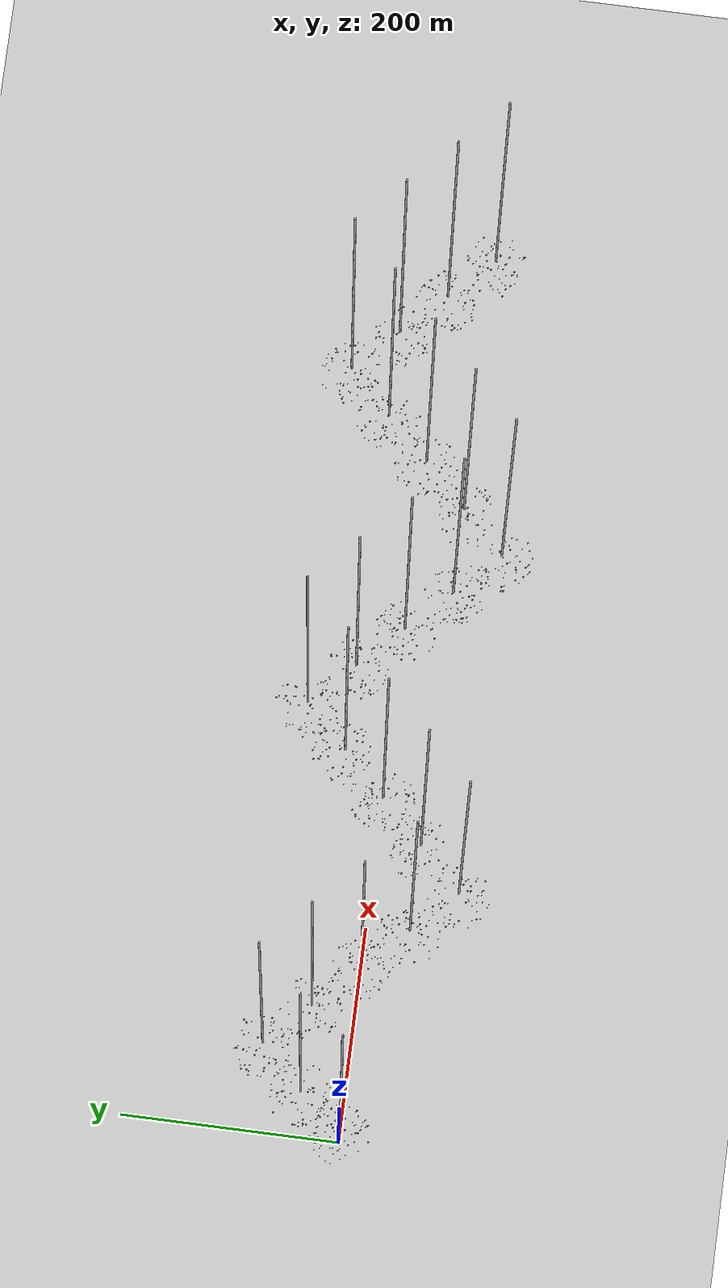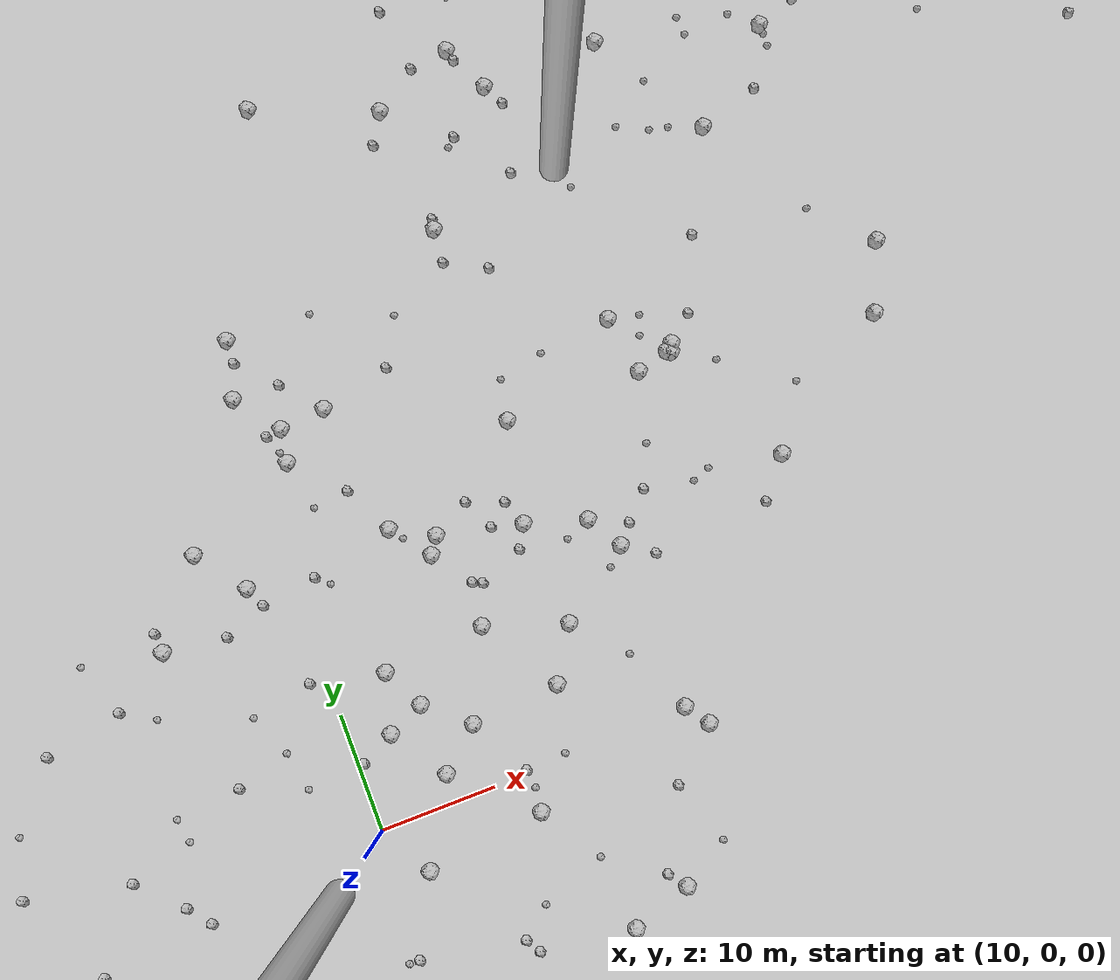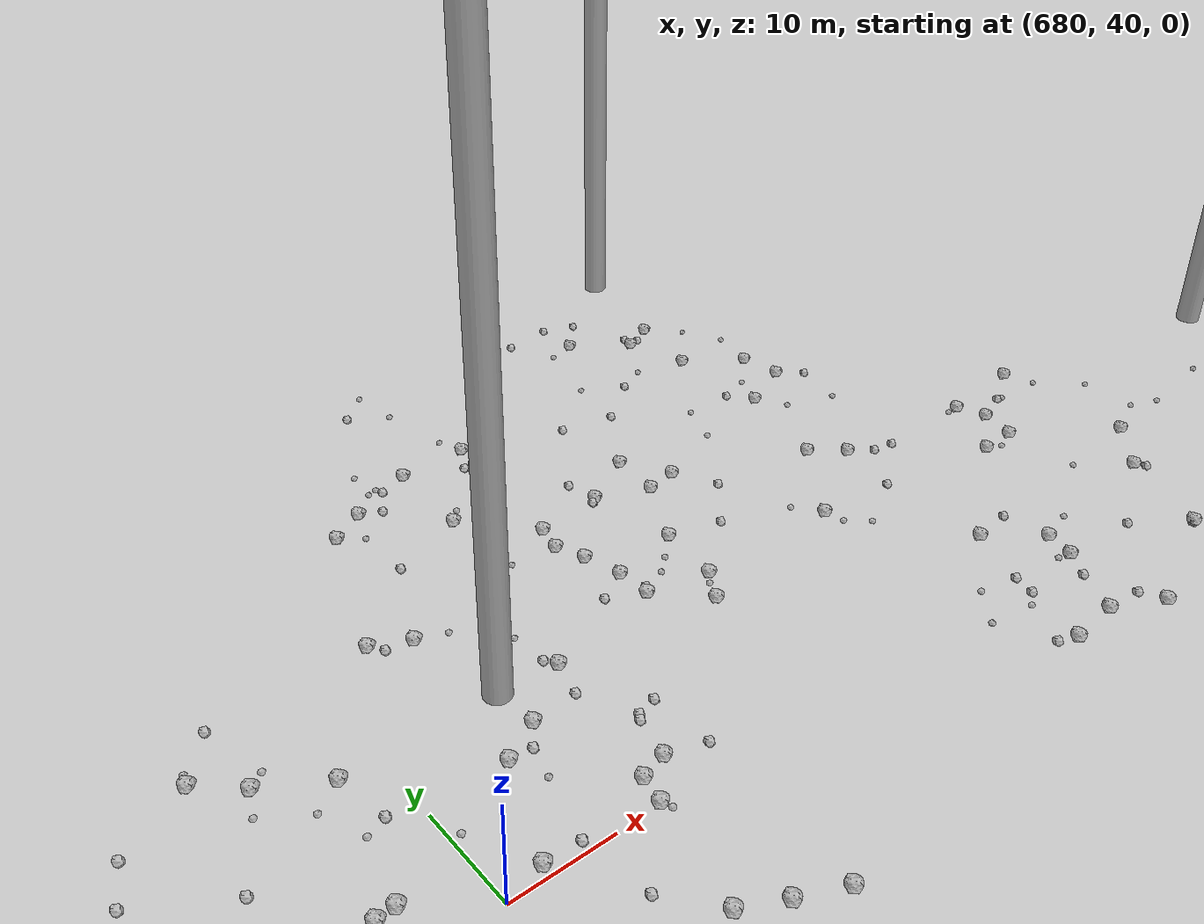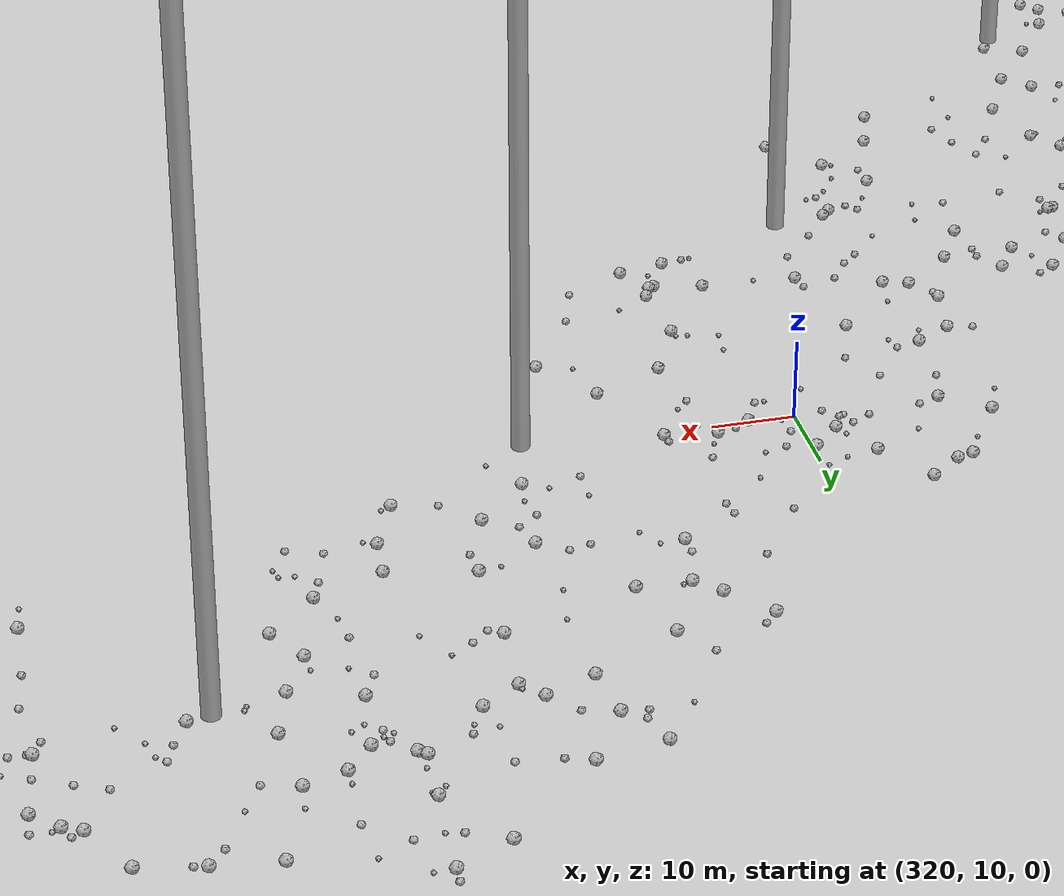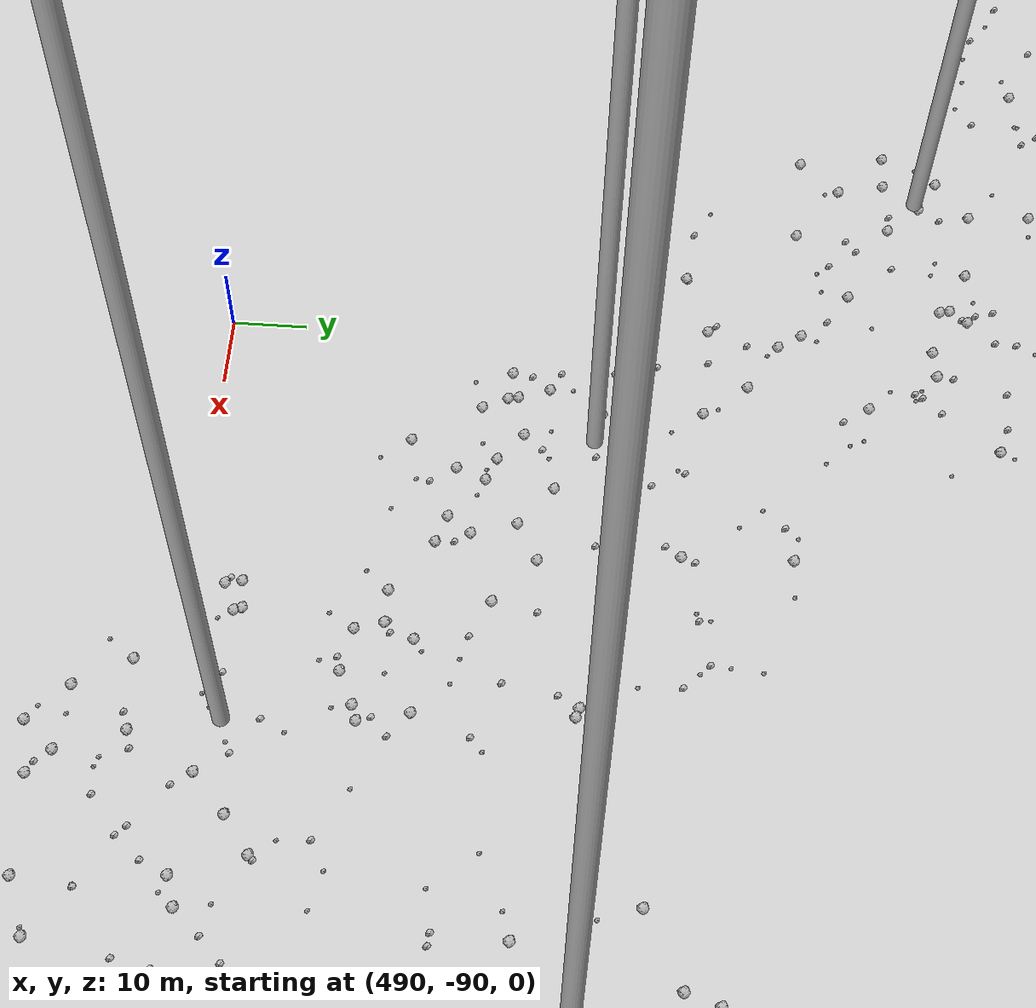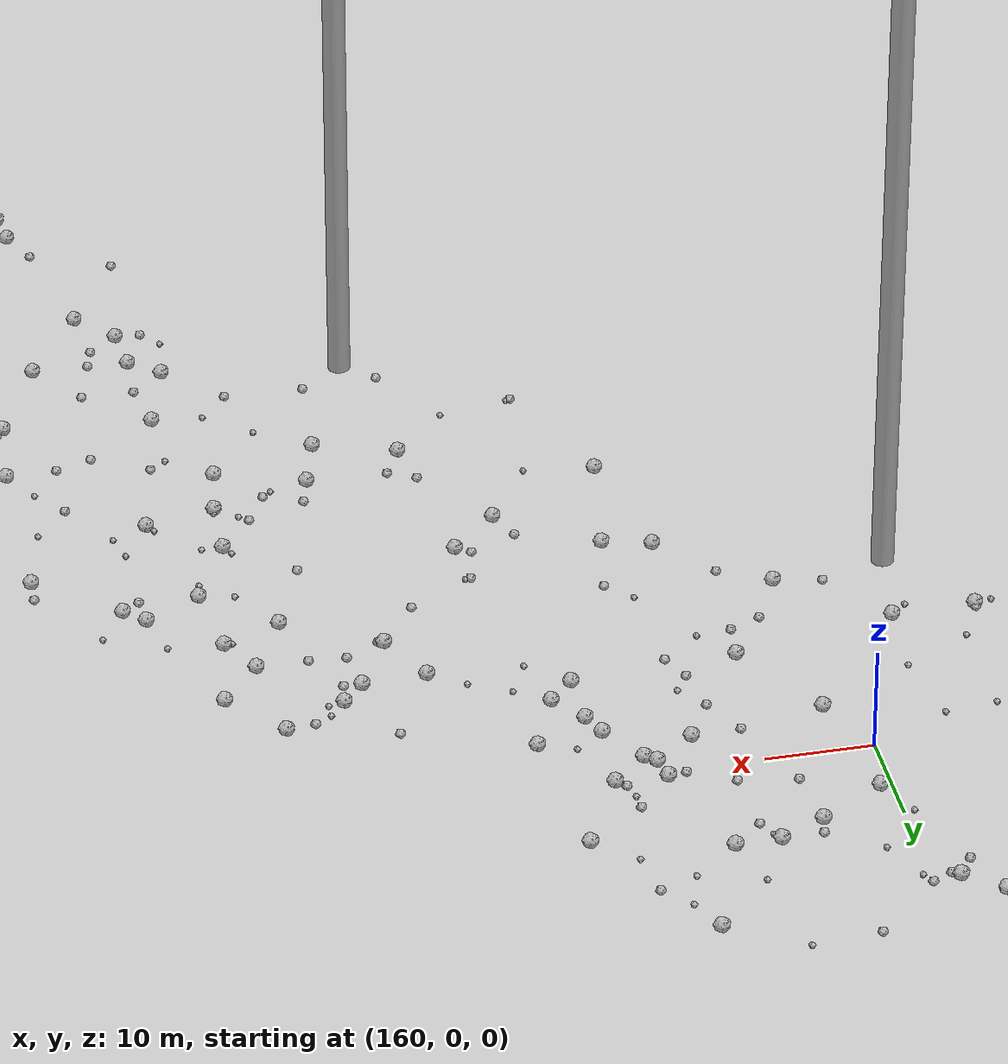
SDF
<sdf version="1.6">
 <world name="default">
  <include><uri>model://custom_ground</uri></include>
  <include><uri>model://sun</uri></include>
  <spherical_coordinates>
   <surface_model>EARTH_WGS84</surface_model>
   <latitude_deg>38.161479</latitude_deg>
   <longitude_deg>-122.454630</longitude_deg>
   <elevation>488.0</elevation>
   <heading_deg>90</heading_deg>
  </spherical_coordinates>
  <model name="rock1_0_0">
   <include><uri>model://rock1</uri><pose>11.143650941418674 -16.417504763424855 0.5 0 0 0</pose></include>
  </model>
  <model name="rock1_0_1">
   <include><uri>model://rock1</uri><pose>27.83507927308802 6.034104738478291 0.5 0 0 0</pose></include>
  </model>
  <model name="rock1_0_2">
   <include><uri>model://rock1</uri><pose>16.64858575538426 2.448143112050303 0.5 0 0 0</pose></include>
  </model>
  <model name="rock1_0_3">
   <include><uri>model://rock1</uri><pose>12.656609301338968 -4.392591658817423 0.5 0 0 0</pose></include>
  </model>
  <model name="rock1_0_4">
   <include><uri>model://rock1</uri><pose>11.300185489799702 -14.304817862582501 0.5 0 0 0</pose></include>
  </model>
  <model name="rock1_0_5">
   <include><uri>model://rock1</uri><pose>14.793944905360036 12.050399647413364 0.5 0 0 0</pose></include>
  </model>
  <model name="rock1_0_6">
   <include><uri>model://rock1</uri><pose>37.11355414811421 0.5372550991951073 0.5 0 0 0</pose></include>
  </model>
  <model name="rock1_0_7">
   <include><uri>model://rock1</uri><pose>23.66262860347387 12.791745267514926 0.5 0 0 0</pose></include>
  </model>
  <model name="rock1_0_8">
   <include><uri>model://rock1</uri><pose>13.460754831755004 7.124106758800551 0.5 0 0 0</pose></include>
  </model>
  <model name="rock1_0_9">
   <include><uri>model://rock1</uri><pose>6.293535491964139 22.768422653297705 0.5 0 0 0</pose></include>
  </model>
  <model name="rock1_0_10">
   <include><uri>model://rock1</uri><pose>19.182328347549948 23.23523669202234 0.5 0 0 0</pose></include>
  </model>
  <model name="rock1_0_11">
   <include><uri>model://rock1</uri><pose>16.605818071323412 8.514221518128508 0.5 0 0 0</pose></include>
  </model>
  <model name="rock1_0_12">
   <include><uri>model://rock1</uri><pose>21.787305732238607 19.894200807071755 0.5 0 0 0</pose></include>
  </model>
  <model name="rock1_0_13">
   <include><uri>model://rock1</uri><pose>20.12243894713456 5.476201767984463 0.5 0 0 0</pose></include>
  </model>
  <model name="rock1_0_14">
   <include><uri>model://rock1</uri><pose>17.76164240348148 -22.970244654189948 0.5 0 0 0</pose></include>
  </model>
  <model name="rock1_0_15">
   <include><uri>model://rock1</uri><pose>38.49510815788901 -1.446841855220942 0.5 0 0 0</pose></include>
  </model>
  <model name="rock1_0_16">
   <include><uri>model://rock1</uri><pose>22.857286175380608 -3.2045834499339385 0.5 0 0 0</pose></include>
  </model>
  <model name="rock1_0_17">
   <include><uri>model://rock1</uri><pose>14.208234030777867 -18.193533379243807 0.5 0 0 0</pose></include>
  </model>
  <model name="rock1_0_18">
   <include><uri>model://rock1</uri><pose>4.251891935902616 -26.5975612717064 0.5 0 0 0</pose></include>
  </model>
  <model name="rock1_0_19">
   <include><uri>model://rock1</uri><pose>3.0368480840931475 27.015487492464125 0.5 0 0 0</pose></include>
  </model>
  <model name="rock1_0_20">
   <include><uri>model://rock1</uri><pose>-2.0475511492205065 20.237796704588398 0.5 0 0 0</pose></include>
  </model>
  <model name="rock1_0_21">
   <include><uri>model://rock1</uri><pose>23.704083376823455 -21.590191075085436 0.5 0 0 0</pose></include>
  </model>
  <model name="rock1_0_22">
   <include><uri>model://rock1</uri><pose>19.23832279339296 -24.239999221777886 0.5 0 0 0</pose></include>
  </model>
  <model name="rock1_0_23">
   <include><uri>model://rock1</uri><pose>31.887816754875935 -13.003803814213903 0.5 0 0 0</pose></include>
  </model>
  <model name="rock1_0_24">
   <include><uri>model://rock1</uri><pose>-0.651962226242432 -8.74569180068027 0.5 0 0 0</pose></include>
  </model>
  <model name="rock1_0_25">
   <include><uri>model://rock1</uri><pose>30.609377551162147 10.404826168022097 0.5 0 0 0</pose></include>
  </model>
  <model name="rock1_0_26">
   <include><uri>model://rock1</uri><pose>26.770032368812018 -14.618875563301916 0.5 0 0 0</pose></include>
  </model>
  <model name="rock2_0_0">
   <include><uri>model://rock2</uri><pose>-2.2947553482438963 21.985821324124657 0.3 0 0 0</pose></include>
  </model>
  <model name="rock2_0_1">
   <include><uri>model://rock2</uri><pose>18.76898629384688 -13.588022708538293 0.3 0 0 0</pose></include>
  </model>
  <model name="rock2_0_2">
   <include><uri>model://rock2</uri><pose>3.3191980811748394 19.543325464508392 0.3 0 0 0</pose></include>
  </model>
  <model name="rock2_0_3">
   <include><uri>model://rock2</uri><pose>19.81743505021531 -25.470510414540257 0.3 0 0 0</pose></include>
  </model>
  <model name="rock2_0_4">
   <include><uri>model://rock2</uri><pose>-13.921708448957668 15.500098014237821 0.3 0 0 0</pose></include>
  </model>
  <model name="rock2_0_5">
   <include><uri>model://rock2</uri><pose>18.03320267308581 -12.365036677564703 0.3 0 0 0</pose></include>
  </model>
  <model name="rock2_0_6">
   <include><uri>model://rock2</uri><pose>10.501173092892877 5.649785620226908 0.3 0 0 0</pose></include>
  </model>
  <model name="rock2_0_7">
   <include><uri>model://rock2</uri><pose>0.13542630359271968 7.413126379831795 0.3 0 0 0</pose></include>
  </model>
  <model name="rock2_0_8">
   <include><uri>model://rock2</uri><pose>30.768815503982196 -11.613045301659191 0.3 0 0 0</pose></include>
  </model>
  <model name="rock2_0_9">
   <include><uri>model://rock2</uri><pose>34.2345641798857 -5.262628022735122 0.3 0 0 0</pose></include>
  </model>
  <model name="rock2_0_10">
   <include><uri>model://rock2</uri><pose>-19.402983589531843 5.243869640947111 0.3 0 0 0</pose></include>
  </model>
  <model name="rock2_0_11">
   <include><uri>model://rock2</uri><pose>-5.495230639882072 -1.9913567139663542 0.3 0 0 0</pose></include>
  </model>
  <model name="rock2_0_12">
   <include><uri>model://rock2</uri><pose>9.376237557129915 -10.747480750995237 0.3 0 0 0</pose></include>
  </model>
  <model name="rock2_0_13">
   <include><uri>model://rock2</uri><pose>11.883128939612774 21.65405796843382 0.3 0 0 0</pose></include>
  </model>
  <model name="rock2_0_14">
   <include><uri>model://rock2</uri><pose>-7.1714440280505425 16.835181528024016 0.3 0 0 0</pose></include>
  </model>
  <model name="rock2_0_15">
   <include><uri>model://rock2</uri><pose>2.748294946988704 -14.02161789871209 0.3 0 0 0</pose></include>
  </model>
  <model name="rock2_0_16">
   <include><uri>model://rock2</uri><pose>8.49452184777871 13.44386578085927 0.3 0 0 0</pose></include>
  </model>
  <model name="rock2_0_17">
   <include><uri>model://rock2</uri><pose>16.97162174002488 27.60588910034142 0.3 0 0 0</pose></include>
  </model>
  <model name="rock2_0_18">
   <include><uri>model://rock2</uri><pose>-7.033484361243602 -0.1203224903386122 0.3 0 0 0</pose></include>
  </model>
  <model name="rock2_0_19">
   <include><uri>model://rock2</uri><pose>24.16561977555412 16.544465769305823 0.3 0 0 0</pose></include>
  </model>
  <model name="rock2_0_20">
   <include><uri>model://rock2</uri><pose>17.709486646549564 -18.481750109984397 0.3 0 0 0</pose></include>
  </model>
  <model name="rock2_0_21">
   <include><uri>model://rock2</uri><pose>-10.526748756899053 3.318125464738536 0.3 0 0 0</pose></include>
  </model>
  <model name="rock2_0_22">
   <include><uri>model://rock2</uri><pose>7.020591042518255 20.98049445318061 0.3 0 0 0</pose></include>
  </model>
  <model name="rock2_0_23">
   <include><uri>model://rock2</uri><pose>22.927721667362277 0.35884268539288655 0.3 0 0 0</pose></include>
  </model>
  <model name="rock2_0_24">
   <include><uri>model://rock2</uri><pose>-15.07398089123913 -2.928789202647735 0.3 0 0 0</pose></include>
  </model>
  <model name="rock2_0_25">
   <include><uri>model://rock2</uri><pose>2.8736734525573517 -5.367638294519203 0.3 0 0 0</pose></include>
  </model>
  <model name="rock2_0_26">
   <include><uri>model://rock2</uri><pose>26.032413909453048 23.12047414287153 0.3 0 0 0</pose></include>
  </model>
  <model name="rock3_0_0">
   <include><uri>model://rock3</uri><pose>20.505110261606404 -10.341852483176723 0.2 0 0 0</pose></include>
  </model>
  <model name="rock3_0_1">
   <include><uri>model://rock3</uri><pose>23.070958540862 -1.2662872646168815 0.2 0 0 0</pose></include>
  </model>
  <model name="rock3_0_2">
   <include><uri>model://rock3</uri><pose>35.559268838565785 13.52113279759211 0.2 0 0 0</pose></include>
  </model>
  <model name="rock3_0_3">
   <include><uri>model://rock3</uri><pose>1.9469146130718187 -18.226252528520973 0.2 0 0 0</pose></include>
  </model>
  <model name="rock3_0_4">
   <include><uri>model://rock3</uri><pose>-5.534208475254253 6.856362089168606 0.2 0 0 0</pose></include>
  </model>
  <model name="rock3_0_5">
   <include><uri>model://rock3</uri><pose>11.020026263965232 -26.14810078771512 0.2 0 0 0</pose></include>
  </model>
  <model name="rock3_0_6">
   <include><uri>model://rock3</uri><pose>-9.031924225940928 21.526733154375115 0.2 0 0 0</pose></include>
  </model>
  <model name="rock3_0_7">
   <include><uri>model://rock3</uri><pose>-18.15227509209616 10.133185981570826 0.2 0 0 0</pose></include>
  </model>
  <model name="rock3_0_8">
   <include><uri>model://rock3</uri><pose>26.073331325868786 -8.398400956384336 0.2 0 0 0</pose></include>
  </model>
  <model name="rock3_0_9">
   <include><uri>model://rock3</uri><pose>5.586248252618269 -11.806685652556382 0.2 0 0 0</pose></include>
  </model>
  <model name="rock3_0_10">
   <include><uri>model://rock3</uri><pose>19.975091214850778 22.09318521446768 0.2 0 0 0</pose></include>
  </model>
  <model name="rock3_0_11">
   <include><uri>model://rock3</uri><pose>-10.216215631716155 -7.556445482096407 0.2 0 0 0</pose></include>
  </model>
  <model name="rock3_0_12">
   <include><uri>model://rock3</uri><pose>36.02926587217091 -10.719038555490886 0.2 0 0 0</pose></include>
  </model>
  <model name="rock3_0_13">
   <include><uri>model://rock3</uri><pose>4.743393350156545 8.694106966501344 0.2 0 0 0</pose></include>
  </model>
  <model name="rock3_0_14">
   <include><uri>model://rock3</uri><pose>-5.142884198374109 4.777587829714456 0.2 0 0 0</pose></include>
  </model>
  <model name="rock3_0_15">
   <include><uri>model://rock3</uri><pose>3.120570363886486 12.41221516808671 0.2 0 0 0</pose></include>
  </model>
  <model name="rock3_0_16">
   <include><uri>model://rock3</uri><pose>26.379723733728177 0.471022889713101 0.2 0 0 0</pose></include>
  </model>
  <model name="rock3_0_17">
   <include><uri>model://rock3</uri><pose>-4.4395508618905115 15.152405948505582 0.2 0 0 0</pose></include>
  </model>
  <model name="rock3_0_18">
   <include><uri>model://rock3</uri><pose>10.607213035893505 -17.70778571635106 0.2 0 0 0</pose></include>
  </model>
  <model name="rock3_0_19">
   <include><uri>model://rock3</uri><pose>4.78941258956155 -18.359040337653752 0.2 0 0 0</pose></include>
  </model>
  <model name="rock3_0_20">
   <include><uri>model://rock3</uri><pose>34.39175251350764 6.172346334664816 0.2 0 0 0</pose></include>
  </model>
  <model name="rock3_0_21">
   <include><uri>model://rock3</uri><pose>8.435383136539013 -10.749971539786543 0.2 0 0 0</pose></include>
  </model>
  <model name="rock3_0_22">
   <include><uri>model://rock3</uri><pose>5.4505648510432465 5.281849789766753 0.2 0 0 0</pose></include>
  </model>
  <model name="rock3_0_23">
   <include><uri>model://rock3</uri><pose>-5.23547744503624 -18.669782066125162 0.2 0 0 0</pose></include>
  </model>
  <model name="rock3_0_24">
   <include><uri>model://rock3</uri><pose>12.91748954711607 20.640260945403313 0.2 0 0 0</pose></include>
  </model>
  <model name="rock3_0_25">
   <include><uri>model://rock3</uri><pose>33.01368755081372 17.067142932624634 0.2 0 0 0</pose></include>
  </model>
  <model name="rock3_0_26">
   <include><uri>model://rock3</uri><pose>21.90950112499044 -20.0110670654926 0.2 0 0 0</pose></include>
  </model>
  <model name="rock1_1_0">
   <include><uri>model://rock1</uri><pose>47.205290114839954 28.96202334344089 0.5 0 0 0</pose></include>
  </model>
  <model name="rock1_1_1">
   <include><uri>model://rock1</uri><pose>47.52314841022405 29.681446669828414 0.5 0 0 0</pose></include>
  </model>
  <model name="rock1_1_2">
   <include><uri>model://rock1</uri><pose>30.014789121373585 19.631589433112264 0.5 0 0 0</pose></include>
  </model>
  <model name="rock1_1_3">
   <include><uri>model://rock1</uri><pose>35.25352154698338 18.01084844546548 0.5 0 0 0</pose></include>
  </model>
  <model name="rock1_1_4">
   <include><uri>model://rock1</uri><pose>67.61465527122164 31.813413851362355 0.5 0 0 0</pose></include>
  </model>
  <model name="rock1_1_5">
   <include><uri>model://rock1</uri><pose>64.93463487677123 25.912555974034724 0.5 0 0 0</pose></include>
  </model>
  <model name="rock1_1_6">
   <include><uri>model://rock1</uri><pose>31.896038607347265 28.387514545269852 0.5 0 0 0</pose></include>
  </model>
  <model name="rock1_1_7">
   <include><uri>model://rock1</uri><pose>46.89510194067125 29.169201302823577 0.5 0 0 0</pose></include>
  </model>
  <model name="rock1_1_8">
   <include><uri>model://rock1</uri><pose>22.75433593547637 21.30843020128942 0.5 0 0 0</pose></include>
  </model>
  <model name="rock1_1_9">
   <include><uri>model://rock1</uri><pose>10.542437674850323 38.47756582451055 0.5 0 0 0</pose></include>
  </model>
  <model name="rock1_1_10">
   <include><uri>model://rock1</uri><pose>40.64687653749838 57.16152419930981 0.5 0 0 0</pose></include>
  </model>
  <model name="rock1_1_11">
   <include><uri>model://rock1</uri><pose>52.77187428777113 17.356701052823738 0.5 0 0 0</pose></include>
  </model>
  <model name="rock1_1_12">
   <include><uri>model://rock1</uri><pose>13.046999577484641 31.671154111362803 0.5 0 0 0</pose></include>
  </model>
  <model name="rock1_1_13">
   <include><uri>model://rock1</uri><pose>57.38328257753889 46.80486953737435 0.5 0 0 0</pose></include>
  </model>
  <model name="rock1_1_14">
   <include><uri>model://rock1</uri><pose>40.580897028701344 66.6926538310334 0.5 0 0 0</pose></include>
  </model>
  <model name="rock1_1_15">
   <include><uri>model://rock1</uri><pose>37.04439706172931 14.968564100970013 0.5 0 0 0</pose></include>
  </model>
  <model name="rock1_1_16">
   <include><uri>model://rock1</uri><pose>13.53659785098682 34.60618536408644 0.5 0 0 0</pose></include>
  </model>
  <model name="rock1_1_17">
   <include><uri>model://rock1</uri><pose>65.60509070284573 53.841547625911986 0.5 0 0 0</pose></include>
  </model>
  <model name="rock1_1_18">
   <include><uri>model://rock1</uri><pose>43.98645767545044 28.369980421698614 0.5 0 0 0</pose></include>
  </model>
  <model name="rock1_1_19">
   <include><uri>model://rock1</uri><pose>31.228941806500373 58.28513805747954 0.5 0 0 0</pose></include>
  </model>
  <model name="rock1_1_20">
   <include><uri>model://rock1</uri><pose>20.363622634749024 62.58772995669308 0.5 0 0 0</pose></include>
  </model>
  <model name="rock1_1_21">
   <include><uri>model://rock1</uri><pose>17.547371674539153 34.9642035317726 0.5 0 0 0</pose></include>
  </model>
  <model name="rock1_1_22">
   <include><uri>model://rock1</uri><pose>11.740323866290808 43.56566369031425 0.5 0 0 0</pose></include>
  </model>
  <model name="rock1_1_23">
   <include><uri>model://rock1</uri><pose>51.295456666385604 57.556647011530266 0.5 0 0 0</pose></include>
  </model>
  <model name="rock1_1_24">
   <include><uri>model://rock1</uri><pose>43.184808427400576 33.619690364124324 0.5 0 0 0</pose></include>
  </model>
  <model name="rock1_1_25">
   <include><uri>model://rock1</uri><pose>38.678245041254456 61.516876785451224 0.5 0 0 0</pose></include>
  </model>
  <model name="rock1_1_26">
   <include><uri>model://rock1</uri><pose>31.910577469469562 46.47949812827736 0.5 0 0 0</pose></include>
  </model>
  <model name="rock2_1_0">
   <include><uri>model://rock2</uri><pose>12.078300537955647 34.469504068270055 0.3 0 0 0</pose></include>
  </model>
  <model name="rock2_1_1">
   <include><uri>model://rock2</uri><pose>27.32151258116407 20.34883522863226 0.3 0 0 0</pose></include>
  </model>
  <model name="rock2_1_2">
   <include><uri>model://rock2</uri><pose>47.16809583670982 56.413710643589084 0.3 0 0 0</pose></include>
  </model>
  <model name="rock2_1_3">
   <include><uri>model://rock2</uri><pose>41.59549267104145 55.29130211241527 0.3 0 0 0</pose></include>
  </model>
  <model name="rock2_1_4">
   <include><uri>model://rock2</uri><pose>35.16282644241666 41.61967931348734 0.3 0 0 0</pose></include>
  </model>
  <model name="rock2_1_5">
   <include><uri>model://rock2</uri><pose>39.59527245063737 13.294037291300171 0.3 0 0 0</pose></include>
  </model>
  <model name="rock2_1_6">
   <include><uri>model://rock2</uri><pose>31.586924659471272 43.50868879795716 0.3 0 0 0</pose></include>
  </model>
  <model name="rock2_1_7">
   <include><uri>model://rock2</uri><pose>29.54757785727331 55.69085075204856 0.3 0 0 0</pose></include>
  </model>
  <model name="rock2_1_8">
   <include><uri>model://rock2</uri><pose>34.35245889822123 67.19103984110873 0.3 0 0 0</pose></include>
  </model>
  <model name="rock2_1_9">
   <include><uri>model://rock2</uri><pose>38.93073197570671 60.58492013863273 0.3 0 0 0</pose></include>
  </model>
  <model name="rock2_1_10">
   <include><uri>model://rock2</uri><pose>29.16957881807459 21.928842144138503 0.3 0 0 0</pose></include>
  </model>
  <model name="rock2_1_11">
   <include><uri>model://rock2</uri><pose>40.007884326275075 49.01013105503947 0.3 0 0 0</pose></include>
  </model>
  <model name="rock2_1_12">
   <include><uri>model://rock2</uri><pose>31.348374892124664 58.49824883435769 0.3 0 0 0</pose></include>
  </model>
  <model name="rock2_1_13">
   <include><uri>model://rock2</uri><pose>23.73350497662036 36.49531064714517 0.3 0 0 0</pose></include>
  </model>
  <model name="rock2_1_14">
   <include><uri>model://rock2</uri><pose>36.47944938447141 53.87702770617106 0.3 0 0 0</pose></include>
  </model>
  <model name="rock2_1_15">
   <include><uri>model://rock2</uri><pose>11.580214637021069 41.52088331483938 0.3 0 0 0</pose></include>
  </model>
  <model name="rock2_1_16">
   <include><uri>model://rock2</uri><pose>49.8700566150969 31.678708384073133 0.3 0 0 0</pose></include>
  </model>
  <model name="rock2_1_17">
   <include><uri>model://rock2</uri><pose>52.8134903204751 38.106850513383506 0.3 0 0 0</pose></include>
  </model>
  <model name="rock2_1_18">
   <include><uri>model://rock2</uri><pose>24.999747171617276 16.17556859693567 0.3 0 0 0</pose></include>
  </model>
  <model name="rock2_1_19">
   <include><uri>model://rock2</uri><pose>35.11654815967488 61.166055055126506 0.3 0 0 0</pose></include>
  </model>
  <model name="rock2_1_20">
   <include><uri>model://rock2</uri><pose>62.9466055126598 48.60985614716025 0.3 0 0 0</pose></include>
  </model>
  <model name="rock2_1_21">
   <include><uri>model://rock2</uri><pose>32.08590241693376 47.517639787869385 0.3 0 0 0</pose></include>
  </model>
  <model name="rock2_1_22">
   <include><uri>model://rock2</uri><pose>28.896020062200478 17.722046566511136 0.3 0 0 0</pose></include>
  </model>
  <model name="rock2_1_23">
   <include><uri>model://rock2</uri><pose>40.62765421818138 18.77634950988706 0.3 0 0 0</pose></include>
  </model>
  <model name="rock2_1_24">
   <include><uri>model://rock2</uri><pose>14.590818559672865 38.35559606645459 0.3 0 0 0</pose></include>
  </model>
  <model name="rock2_1_25">
   <include><uri>model://rock2</uri><pose>49.985206398104474 14.047188069442146 0.3 0 0 0</pose></include>
  </model>
  <model name="rock2_1_26">
   <include><uri>model://rock2</uri><pose>38.424605524239176 16.51697009842743 0.3 0 0 0</pose></include>
  </model>
  <model name="rock3_1_0">
   <include><uri>model://rock3</uri><pose>54.50011541932375 47.97320805707854 0.2 0 0 0</pose></include>
  </model>
  <model name="rock3_1_1">
   <include><uri>model://rock3</uri><pose>65.68478749499683 53.05570837240641 0.2 0 0 0</pose></include>
  </model>
  <model name="rock3_1_2">
   <include><uri>model://rock3</uri><pose>45.82704125457929 67.68074443717674 0.2 0 0 0</pose></include>
  </model>
  <model name="rock3_1_3">
   <include><uri>model://rock3</uri><pose>45.874481872657725 33.04431310966973 0.2 0 0 0</pose></include>
  </model>
  <model name="rock3_1_4">
   <include><uri>model://rock3</uri><pose>59.08179882933306 55.50365293212283 0.2 0 0 0</pose></include>
  </model>
  <model name="rock3_1_5">
   <include><uri>model://rock3</uri><pose>36.65996575121504 32.90836952265321 0.2 0 0 0</pose></include>
  </model>
  <model name="rock3_1_6">
   <include><uri>model://rock3</uri><pose>12.65379310263107 32.76308270697476 0.2 0 0 0</pose></include>
  </model>
  <model name="rock3_1_7">
   <include><uri>model://rock3</uri><pose>35.68746329974165 53.1657244387119 0.2 0 0 0</pose></include>
  </model>
  <model name="rock3_1_8">
   <include><uri>model://rock3</uri><pose>54.0792478590369 52.7397050393147 0.2 0 0 0</pose></include>
  </model>
  <model name="rock3_1_9">
   <include><uri>model://rock3</uri><pose>63.10428769769246 36.715590929344266 0.2 0 0 0</pose></include>
  </model>
  <model name="rock3_1_10">
   <include><uri>model://rock3</uri><pose>32.60956064670114 31.986744877001783 0.2 0 0 0</pose></include>
  </model>
  <model name="rock3_1_11">
   <include><uri>model://rock3</uri><pose>52.84779317150094 48.347960369353245 0.2 0 0 0</pose></include>
  </model>
  <model name="rock3_1_12">
   <include><uri>model://rock3</uri><pose>42.29497358939077 22.34586759610525 0.2 0 0 0</pose></include>
  </model>
  <model name="rock3_1_13">
   <include><uri>model://rock3</uri><pose>19.132405669623733 43.31449168521245 0.2 0 0 0</pose></include>
  </model>
  <model name="rock3_1_14">
   <include><uri>model://rock3</uri><pose>46.451794604945725 18.452435048224608 0.2 0 0 0</pose></include>
  </model>
  <model name="rock3_1_15">
   <include><uri>model://rock3</uri><pose>44.481011634261264 45.910774130067104 0.2 0 0 0</pose></include>
  </model>
  <model name="rock3_1_16">
   <include><uri>model://rock3</uri><pose>45.21773254979546 31.32651168319952 0.2 0 0 0</pose></include>
  </model>
  <model name="rock3_1_17">
   <include><uri>model://rock3</uri><pose>50.19232301111966 49.65036346476742 0.2 0 0 0</pose></include>
  </model>
  <model name="rock3_1_18">
   <include><uri>model://rock3</uri><pose>59.00967452773644 57.2545374705396 0.2 0 0 0</pose></include>
  </model>
  <model name="rock3_1_19">
   <include><uri>model://rock3</uri><pose>44.90878207900939 17.883813936150062 0.2 0 0 0</pose></include>
  </model>
  <model name="rock3_1_20">
   <include><uri>model://rock3</uri><pose>50.64338200186231 26.992527451787012 0.2 0 0 0</pose></include>
  </model>
  <model name="rock3_1_21">
   <include><uri>model://rock3</uri><pose>65.59886704545772 51.89603524212317 0.2 0 0 0</pose></include>
  </model>
  <model name="rock3_1_22">
   <include><uri>model://rock3</uri><pose>56.38646328754594 22.782347365741813 0.2 0 0 0</pose></include>
  </model>
  <model name="rock3_1_23">
   <include><uri>model://rock3</uri><pose>13.787612209745042 27.228427262940862 0.2 0 0 0</pose></include>
  </model>
  <model name="rock3_1_24">
   <include><uri>model://rock3</uri><pose>25.962797561616597 40.59328408495162 0.2 0 0 0</pose></include>
  </model>
  <model name="rock3_1_25">
   <include><uri>model://rock3</uri><pose>60.564147191308095 61.694498308248306 0.2 0 0 0</pose></include>
  </model>
  <model name="rock3_1_26">
   <include><uri>model://rock3</uri><pose>57.65243661718913 46.74685108798509 0.2 0 0 0</pose></include>
  </model>
  <model name="rock1_2_0">
   <include><uri>model://rock1</uri><pose>84.88542534697694 70.8883203526855 0.5 0 0 0</pose></include>
  </model>
  <model name="rock1_2_1">
   <include><uri>model://rock1</uri><pose>57.30706883843976 76.2907221656007 0.5 0 0 0</pose></include>
  </model>
  <model name="rock1_2_2">
   <include><uri>model://rock1</uri><pose>84.2888199732129 57.39667805977489 0.5 0 0 0</pose></include>
  </model>
  <model name="rock1_2_3">
   <include><uri>model://rock1</uri><pose>51.90767833307132 89.86483714546924 0.5 0 0 0</pose></include>
  </model>
  <model name="rock1_2_4">
   <include><uri>model://rock1</uri><pose>101.86138229450606 100.12209456609068 0.5 0 0 0</pose></include>
  </model>
  <model name="rock1_2_5">
   <include><uri>model://rock1</uri><pose>106.88716539616982 74.88169219161378 0.5 0 0 0</pose></include>
  </model>
  <model name="rock1_2_6">
   <include><uri>model://rock1</uri><pose>70.60133679545845 77.38413066717675 0.5 0 0 0</pose></include>
  </model>
  <model name="rock1_2_7">
   <include><uri>model://rock1</uri><pose>87.35762727688811 85.31100372418636 0.5 0 0 0</pose></include>
  </model>
  <model name="rock1_2_8">
   <include><uri>model://rock1</uri><pose>75.30796468256858 104.22173854454627 0.5 0 0 0</pose></include>
  </model>
  <model name="rock1_2_9">
   <include><uri>model://rock1</uri><pose>75.19233904270325 85.30763094025244 0.5 0 0 0</pose></include>
  </model>
  <model name="rock1_2_10">
   <include><uri>model://rock1</uri><pose>91.45105504530859 62.85335429323278 0.5 0 0 0</pose></include>
  </model>
  <model name="rock1_2_11">
   <include><uri>model://rock1</uri><pose>74.5929389850744 97.05015386499983 0.5 0 0 0</pose></include>
  </model>
  <model name="rock1_2_12">
   <include><uri>model://rock1</uri><pose>97.61696009056107 64.92069655172665 0.5 0 0 0</pose></include>
  </model>
  <model name="rock1_2_13">
   <include><uri>model://rock1</uri><pose>98.26245354618544 56.431450225120464 0.5 0 0 0</pose></include>
  </model>
  <model name="rock1_2_14">
   <include><uri>model://rock1</uri><pose>60.11575199436228 75.93154594854677 0.5 0 0 0</pose></include>
  </model>
  <model name="rock1_2_15">
   <include><uri>model://rock1</uri><pose>56.372033714298055 91.86932956655069 0.5 0 0 0</pose></include>
  </model>
  <model name="rock1_2_16">
   <include><uri>model://rock1</uri><pose>56.67356405291838 96.84795220886198 0.5 0 0 0</pose></include>
  </model>
  <model name="rock1_2_17">
   <include><uri>model://rock1</uri><pose>64.9925313454999 72.217509444424 0.5 0 0 0</pose></include>
  </model>
  <model name="rock1_2_18">
   <include><uri>model://rock1</uri><pose>95.27002504618437 72.75502275342316 0.5 0 0 0</pose></include>
  </model>
  <model name="rock1_2_19">
   <include><uri>model://rock1</uri><pose>54.12506220865022 65.79823702149696 0.5 0 0 0</pose></include>
  </model>
  <model name="rock1_2_20">
   <include><uri>model://rock1</uri><pose>70.78739195693313 86.51961893268704 0.5 0 0 0</pose></include>
  </model>
  <model name="rock1_2_21">
   <include><uri>model://rock1</uri><pose>55.47479774849629 89.89468437985923 0.5 0 0 0</pose></include>
  </model>
  <model name="rock1_2_22">
   <include><uri>model://rock1</uri><pose>69.09215043780571 66.65132272851781 0.5 0 0 0</pose></include>
  </model>
  <model name="rock1_2_23">
   <include><uri>model://rock1</uri><pose>99.83407670676212 97.8061775754096 0.5 0 0 0</pose></include>
  </model>
  <model name="rock1_2_24">
   <include><uri>model://rock1</uri><pose>66.18815857673219 65.76957377503118 0.5 0 0 0</pose></include>
  </model>
  <model name="rock1_2_25">
   <include><uri>model://rock1</uri><pose>56.51677677792394 62.626090843035335 0.5 0 0 0</pose></include>
  </model>
  <model name="rock1_2_26">
   <include><uri>model://rock1</uri><pose>107.0375939663314 82.25895196392874 0.5 0 0 0</pose></include>
  </model>
  <model name="rock2_2_0">
   <include><uri>model://rock2</uri><pose>103.7996208482155 72.46685780808374 0.3 0 0 0</pose></include>
  </model>
  <model name="rock2_2_1">
   <include><uri>model://rock2</uri><pose>75.22092556055335 102.94102074251947 0.3 0 0 0</pose></include>
  </model>
  <model name="rock2_2_2">
   <include><uri>model://rock2</uri><pose>77.50703322335771 82.59858748405313 0.3 0 0 0</pose></include>
  </model>
  <model name="rock2_2_3">
   <include><uri>model://rock2</uri><pose>99.36500038084998 97.3180923860346 0.3 0 0 0</pose></include>
  </model>
  <model name="rock2_2_4">
   <include><uri>model://rock2</uri><pose>64.44690647585055 66.30436814795627 0.3 0 0 0</pose></include>
  </model>
  <model name="rock2_2_5">
   <include><uri>model://rock2</uri><pose>51.76627883746882 78.22323334283085 0.3 0 0 0</pose></include>
  </model>
  <model name="rock2_2_6">
   <include><uri>model://rock2</uri><pose>66.5202786749862 65.85273482773579 0.3 0 0 0</pose></include>
  </model>
  <model name="rock2_2_7">
   <include><uri>model://rock2</uri><pose>83.40756404888675 79.25803028053929 0.3 0 0 0</pose></include>
  </model>
  <model name="rock2_2_8">
   <include><uri>model://rock2</uri><pose>92.01450463604867 73.51288076614615 0.3 0 0 0</pose></include>
  </model>
  <model name="rock2_2_9">
   <include><uri>model://rock2</uri><pose>84.37967854753703 97.02928649688778 0.3 0 0 0</pose></include>
  </model>
  <model name="rock2_2_10">
   <include><uri>model://rock2</uri><pose>88.42883443913584 98.36109420201325 0.3 0 0 0</pose></include>
  </model>
  <model name="rock2_2_11">
   <include><uri>model://rock2</uri><pose>99.84332374868252 74.70974789989197 0.3 0 0 0</pose></include>
  </model>
  <model name="rock2_2_12">
   <include><uri>model://rock2</uri><pose>77.06812656296172 91.84019275476817 0.3 0 0 0</pose></include>
  </model>
  <model name="rock2_2_13">
   <include><uri>model://rock2</uri><pose>57.08106200118422 64.39089679314857 0.3 0 0 0</pose></include>
  </model>
  <model name="rock2_2_14">
   <include><uri>model://rock2</uri><pose>74.08115729049003 55.21989245396608 0.3 0 0 0</pose></include>
  </model>
  <model name="rock2_2_15">
   <include><uri>model://rock2</uri><pose>90.1930357689852 94.53267433388021 0.3 0 0 0</pose></include>
  </model>
  <model name="rock2_2_16">
   <include><uri>model://rock2</uri><pose>92.80595615131028 75.17205272746332 0.3 0 0 0</pose></include>
  </model>
  <model name="rock2_2_17">
   <include><uri>model://rock2</uri><pose>88.96329766486215 68.27345806583452 0.3 0 0 0</pose></include>
  </model>
  <model name="rock2_2_18">
   <include><uri>model://rock2</uri><pose>69.29921986682078 55.21804293988685 0.3 0 0 0</pose></include>
  </model>
  <model name="rock2_2_19">
   <include><uri>model://rock2</uri><pose>69.638258863826 57.17969881388196 0.3 0 0 0</pose></include>
  </model>
  <model name="rock2_2_20">
   <include><uri>model://rock2</uri><pose>65.0841466015166 99.27861726179523 0.3 0 0 0</pose></include>
  </model>
  <model name="rock2_2_21">
   <include><uri>model://rock2</uri><pose>60.8348018443762 89.45417101676391 0.3 0 0 0</pose></include>
  </model>
  <model name="rock2_2_22">
   <include><uri>model://rock2</uri><pose>60.300645614466006 94.00195452583543 0.3 0 0 0</pose></include>
  </model>
  <model name="rock2_2_23">
   <include><uri>model://rock2</uri><pose>93.52578501431634 62.341648253115466 0.3 0 0 0</pose></include>
  </model>
  <model name="rock2_2_24">
   <include><uri>model://rock2</uri><pose>74.72825897047005 105.86720222987014 0.3 0 0 0</pose></include>
  </model>
  <model name="rock2_2_25">
   <include><uri>model://rock2</uri><pose>80.9508341519405 61.8086573917513 0.3 0 0 0</pose></include>
  </model>
  <model name="rock2_2_26">
   <include><uri>model://rock2</uri><pose>88.11848634225359 103.45093586090834 0.3 0 0 0</pose></include>
  </model>
  <model name="rock3_2_0">
   <include><uri>model://rock3</uri><pose>94.73126761562253 54.97185921384273 0.2 0 0 0</pose></include>
  </model>
  <model name="rock3_2_1">
   <include><uri>model://rock3</uri><pose>62.32291284587364 88.96843600075718 0.2 0 0 0</pose></include>
  </model>
  <model name="rock3_2_2">
   <include><uri>model://rock3</uri><pose>102.02579384503137 72.85714197504781 0.2 0 0 0</pose></include>
  </model>
  <model name="rock3_2_3">
   <include><uri>model://rock3</uri><pose>63.38851853855328 55.90638242035806 0.2 0 0 0</pose></include>
  </model>
  <model name="rock3_2_4">
   <include><uri>model://rock3</uri><pose>79.44162252236178 50.29740035388339 0.2 0 0 0</pose></include>
  </model>
  <model name="rock3_2_5">
   <include><uri>model://rock3</uri><pose>82.54677591759821 59.241734470382134 0.2 0 0 0</pose></include>
  </model>
  <model name="rock3_2_6">
   <include><uri>model://rock3</uri><pose>102.69312840024507 75.45117606025836 0.2 0 0 0</pose></include>
  </model>
  <model name="rock3_2_7">
   <include><uri>model://rock3</uri><pose>54.92650879219146 80.69806493372855 0.2 0 0 0</pose></include>
  </model>
  <model name="rock3_2_8">
   <include><uri>model://rock3</uri><pose>90.5102678865694 64.34222900996316 0.2 0 0 0</pose></include>
  </model>
  <model name="rock3_2_9">
   <include><uri>model://rock3</uri><pose>100.33594985478115 99.8928534050647 0.2 0 0 0</pose></include>
  </model>
  <model name="rock3_2_10">
   <include><uri>model://rock3</uri><pose>52.008099795934285 80.53251131064877 0.2 0 0 0</pose></include>
  </model>
  <model name="rock3_2_11">
   <include><uri>model://rock3</uri><pose>69.81055392125768 72.41355219518158 0.2 0 0 0</pose></include>
  </model>
  <model name="rock3_2_12">
   <include><uri>model://rock3</uri><pose>63.430506780548214 58.19526137930403 0.2 0 0 0</pose></include>
  </model>
  <model name="rock3_2_13">
   <include><uri>model://rock3</uri><pose>91.96281551402399 100.53445904300708 0.2 0 0 0</pose></include>
  </model>
  <model name="rock3_2_14">
   <include><uri>model://rock3</uri><pose>51.96053057842627 81.41419918428136 0.2 0 0 0</pose></include>
  </model>
  <model name="rock3_2_15">
   <include><uri>model://rock3</uri><pose>86.03792744933398 63.27845104626387 0.2 0 0 0</pose></include>
  </model>
  <model name="rock3_2_16">
   <include><uri>model://rock3</uri><pose>70.62981617688634 55.94057068436426 0.2 0 0 0</pose></include>
  </model>
  <model name="rock3_2_17">
   <include><uri>model://rock3</uri><pose>60.174518920800864 92.27438714213433 0.2 0 0 0</pose></include>
  </model>
  <model name="rock3_2_18">
   <include><uri>model://rock3</uri><pose>77.53176563992795 102.20720040374711 0.2 0 0 0</pose></include>
  </model>
  <model name="rock3_2_19">
   <include><uri>model://rock3</uri><pose>69.35778013587739 68.76824454532391 0.2 0 0 0</pose></include>
  </model>
  <model name="rock3_2_20">
   <include><uri>model://rock3</uri><pose>100.9433654379216 92.66977697871235 0.2 0 0 0</pose></include>
  </model>
  <model name="rock3_2_21">
   <include><uri>model://rock3</uri><pose>59.67182572601172 97.8525980584229 0.2 0 0 0</pose></include>
  </model>
  <model name="rock3_2_22">
   <include><uri>model://rock3</uri><pose>91.00927549660321 94.1898257227187 0.2 0 0 0</pose></include>
  </model>
  <model name="rock3_2_23">
   <include><uri>model://rock3</uri><pose>56.65175494096485 63.7445906443336 0.2 0 0 0</pose></include>
  </model>
  <model name="rock3_2_24">
   <include><uri>model://rock3</uri><pose>89.69688610984275 57.06714679921613 0.2 0 0 0</pose></include>
  </model>
  <model name="rock3_2_25">
   <include><uri>model://rock3</uri><pose>73.08419323797949 93.71780080687125 0.2 0 0 0</pose></include>
  </model>
  <model name="rock3_2_26">
   <include><uri>model://rock3</uri><pose>61.46702054928573 59.356707095942355 0.2 0 0 0</pose></include>
  </model>
  <model name="rock1_3_0">
   <include><uri>model://rock1</uri><pose>146.05252292454665 53.36076491597128 0.5 0 0 0</pose></include>
  </model>
  <model name="rock1_3_1">
   <include><uri>model://rock1</uri><pose>123.6683661091541 33.65834396092262 0.5 0 0 0</pose></include>
  </model>
  <model name="rock1_3_2">
   <include><uri>model://rock1</uri><pose>104.63852118025372 20.583952722649414 0.5 0 0 0</pose></include>
  </model>
  <model name="rock1_3_3">
   <include><uri>model://rock1</uri><pose>128.3526248791191 14.695143218507056 0.5 0 0 0</pose></include>
  </model>
  <model name="rock1_3_4">
   <include><uri>model://rock1</uri><pose>132.68875343032022 17.000820736147993 0.5 0 0 0</pose></include>
  </model>
  <model name="rock1_3_5">
   <include><uri>model://rock1</uri><pose>112.00627361785102 34.92275633627417 0.5 0 0 0</pose></include>
  </model>
  <model name="rock1_3_6">
   <include><uri>model://rock1</uri><pose>99.84304519416442 39.59433795602878 0.5 0 0 0</pose></include>
  </model>
  <model name="rock1_3_7">
   <include><uri>model://rock1</uri><pose>95.489523190485 49.931388424816355 0.5 0 0 0</pose></include>
  </model>
  <model name="rock1_3_8">
   <include><uri>model://rock1</uri><pose>135.04844709983516 36.009785776470096 0.5 0 0 0</pose></include>
  </model>
  <model name="rock1_3_9">
   <include><uri>model://rock1</uri><pose>134.70974902705686 31.08791684183734 0.5 0 0 0</pose></include>
  </model>
  <model name="rock1_3_10">
   <include><uri>model://rock1</uri><pose>117.23294428527856 50.221458181248565 0.5 0 0 0</pose></include>
  </model>
  <model name="rock1_3_11">
   <include><uri>model://rock1</uri><pose>127.58705120214516 14.677409928317235 0.5 0 0 0</pose></include>
  </model>
  <model name="rock1_3_12">
   <include><uri>model://rock1</uri><pose>132.48335981070713 37.01048217760115 0.5 0 0 0</pose></include>
  </model>
  <model name="rock1_3_13">
   <include><uri>model://rock1</uri><pose>95.50202037866798 46.610492813978496 0.5 0 0 0</pose></include>
  </model>
  <model name="rock1_3_14">
   <include><uri>model://rock1</uri><pose>105.80447139940728 19.546482585182122 0.5 0 0 0</pose></include>
  </model>
  <model name="rock1_3_15">
   <include><uri>model://rock1</uri><pose>115.46161385519301 41.665450660646876 0.5 0 0 0</pose></include>
  </model>
  <model name="rock1_3_16">
   <include><uri>model://rock1</uri><pose>127.87604167509068 51.36180416494535 0.5 0 0 0</pose></include>
  </model>
  <model name="rock1_3_17">
   <include><uri>model://rock1</uri><pose>115.61945205716721 35.26175173297649 0.5 0 0 0</pose></include>
  </model>
  <model name="rock1_3_18">
   <include><uri>model://rock1</uri><pose>134.93133347581625 39.087242897795434 0.5 0 0 0</pose></include>
  </model>
  <model name="rock1_3_19">
   <include><uri>model://rock1</uri><pose>131.65836768253325 16.945501250344865 0.5 0 0 0</pose></include>
  </model>
  <model name="rock1_3_20">
   <include><uri>model://rock1</uri><pose>99.99669830033068 48.887386587734554 0.5 0 0 0</pose></include>
  </model>
  <model name="rock1_3_21">
   <include><uri>model://rock1</uri><pose>139.40721270509061 32.88954531544533 0.5 0 0 0</pose></include>
  </model>
  <model name="rock1_3_22">
   <include><uri>model://rock1</uri><pose>136.8200465660573 26.042202111565654 0.5 0 0 0</pose></include>
  </model>
  <model name="rock1_3_23">
   <include><uri>model://rock1</uri><pose>128.44693168577282 17.74434426346624 0.5 0 0 0</pose></include>
  </model>
  <model name="rock1_3_24">
   <include><uri>model://rock1</uri><pose>143.8598903028145 57.57632874032074 0.5 0 0 0</pose></include>
  </model>
  <model name="rock1_3_25">
   <include><uri>model://rock1</uri><pose>103.7831380703115 31.693183483185134 0.5 0 0 0</pose></include>
  </model>
  <model name="rock1_3_26">
   <include><uri>model://rock1</uri><pose>140.90995477148778 37.363533867801394 0.5 0 0 0</pose></include>
  </model>
  <model name="rock2_3_0">
   <include><uri>model://rock2</uri><pose>101.17920108000719 20.526384993266966 0.3 0 0 0</pose></include>
  </model>
  <model name="rock2_3_1">
   <include><uri>model://rock2</uri><pose>107.81008226882072 35.287748346606506 0.3 0 0 0</pose></include>
  </model>
  <model name="rock2_3_2">
   <include><uri>model://rock2</uri><pose>98.78123609928228 59.23961822141878 0.3 0 0 0</pose></include>
  </model>
  <model name="rock2_3_3">
   <include><uri>model://rock2</uri><pose>125.84138909258041 35.76883282515495 0.3 0 0 0</pose></include>
  </model>
  <model name="rock2_3_4">
   <include><uri>model://rock2</uri><pose>133.7385632455346 52.048525111080316 0.3 0 0 0</pose></include>
  </model>
  <model name="rock2_3_5">
   <include><uri>model://rock2</uri><pose>132.11339961896482 44.06373851695346 0.3 0 0 0</pose></include>
  </model>
  <model name="rock2_3_6">
   <include><uri>model://rock2</uri><pose>115.41410621502017 68.94803661920176 0.3 0 0 0</pose></include>
  </model>
  <model name="rock2_3_7">
   <include><uri>model://rock2</uri><pose>107.83276315284716 26.305496575093542 0.3 0 0 0</pose></include>
  </model>
  <model name="rock2_3_8">
   <include><uri>model://rock2</uri><pose>123.1572386374914 44.051542005456895 0.3 0 0 0</pose></include>
  </model>
  <model name="rock2_3_9">
   <include><uri>model://rock2</uri><pose>120.68997385973802 28.41275724101958 0.3 0 0 0</pose></include>
  </model>
  <model name="rock2_3_10">
   <include><uri>model://rock2</uri><pose>146.82719278609937 27.203821827953462 0.3 0 0 0</pose></include>
  </model>
  <model name="rock2_3_11">
   <include><uri>model://rock2</uri><pose>100.62793289777187 21.093574128447116 0.3 0 0 0</pose></include>
  </model>
  <model name="rock2_3_12">
   <include><uri>model://rock2</uri><pose>140.52664705490105 32.78065146414359 0.3 0 0 0</pose></include>
  </model>
  <model name="rock2_3_13">
   <include><uri>model://rock2</uri><pose>143.02060716435275 48.72100570447459 0.3 0 0 0</pose></include>
  </model>
  <model name="rock2_3_14">
   <include><uri>model://rock2</uri><pose>131.71606207180665 52.55844674583779 0.3 0 0 0</pose></include>
  </model>
  <model name="rock2_3_15">
   <include><uri>model://rock2</uri><pose>137.3666824018548 56.8447356829697 0.3 0 0 0</pose></include>
  </model>
  <model name="rock2_3_16">
   <include><uri>model://rock2</uri><pose>125.28658143627916 33.637060216132184 0.3 0 0 0</pose></include>
  </model>
  <model name="rock2_3_17">
   <include><uri>model://rock2</uri><pose>97.77752343227517 49.556431258390525 0.3 0 0 0</pose></include>
  </model>
  <model name="rock2_3_18">
   <include><uri>model://rock2</uri><pose>137.88517275615013 25.13733970670635 0.3 0 0 0</pose></include>
  </model>
  <model name="rock2_3_19">
   <include><uri>model://rock2</uri><pose>124.07428886570942 30.554607650412223 0.3 0 0 0</pose></include>
  </model>
  <model name="rock2_3_20">
   <include><uri>model://rock2</uri><pose>91.8834810534539 45.13142617805521 0.3 0 0 0</pose></include>
  </model>
  <model name="rock2_3_21">
   <include><uri>model://rock2</uri><pose>137.8882623001959 53.918283488418815 0.3 0 0 0</pose></include>
  </model>
  <model name="rock2_3_22">
   <include><uri>model://rock2</uri><pose>122.332009779403 12.112454753440671 0.3 0 0 0</pose></include>
  </model>
  <model name="rock2_3_23">
   <include><uri>model://rock2</uri><pose>126.27238369120698 25.30094063927943 0.3 0 0 0</pose></include>
  </model>
  <model name="rock2_3_24">
   <include><uri>model://rock2</uri><pose>98.94483460022768 42.850714661369615 0.3 0 0 0</pose></include>
  </model>
  <model name="rock2_3_25">
   <include><uri>model://rock2</uri><pose>139.53143051169766 27.894306412755128 0.3 0 0 0</pose></include>
  </model>
  <model name="rock2_3_26">
   <include><uri>model://rock2</uri><pose>146.49407212185284 41.43087057765627 0.3 0 0 0</pose></include>
  </model>
  <model name="rock3_3_0">
   <include><uri>model://rock3</uri><pose>116.3263011210545 68.12092682781719 0.2 0 0 0</pose></include>
  </model>
  <model name="rock3_3_1">
   <include><uri>model://rock3</uri><pose>110.12340849281385 16.97969475414503 0.2 0 0 0</pose></include>
  </model>
  <model name="rock3_3_2">
   <include><uri>model://rock3</uri><pose>132.88816403727515 41.606829125501314 0.2 0 0 0</pose></include>
  </model>
  <model name="rock3_3_3">
   <include><uri>model://rock3</uri><pose>129.94637758823544 64.82288758660584 0.2 0 0 0</pose></include>
  </model>
  <model name="rock3_3_4">
   <include><uri>model://rock3</uri><pose>95.54069262745062 54.92905406611946 0.2 0 0 0</pose></include>
  </model>
  <model name="rock3_3_5">
   <include><uri>model://rock3</uri><pose>130.60930902220045 55.53276577399869 0.2 0 0 0</pose></include>
  </model>
  <model name="rock3_3_6">
   <include><uri>model://rock3</uri><pose>106.67047042242973 16.184556624208312 0.2 0 0 0</pose></include>
  </model>
  <model name="rock3_3_7">
   <include><uri>model://rock3</uri><pose>94.30988038051015 33.732315337447 0.2 0 0 0</pose></include>
  </model>
  <model name="rock3_3_8">
   <include><uri>model://rock3</uri><pose>133.29884108690075 51.42995960501216 0.2 0 0 0</pose></include>
  </model>
  <model name="rock3_3_9">
   <include><uri>model://rock3</uri><pose>126.6092097471537 69.07288389555524 0.2 0 0 0</pose></include>
  </model>
  <model name="rock3_3_10">
   <include><uri>model://rock3</uri><pose>110.85535816518978 48.62635190403371 0.2 0 0 0</pose></include>
  </model>
  <model name="rock3_3_11">
   <include><uri>model://rock3</uri><pose>138.67816483734953 39.62924618856637 0.2 0 0 0</pose></include>
  </model>
  <model name="rock3_3_12">
   <include><uri>model://rock3</uri><pose>105.24625720268016 51.635962112031365 0.2 0 0 0</pose></include>
  </model>
  <model name="rock3_3_13">
   <include><uri>model://rock3</uri><pose>109.78522356398578 30.747660251630357 0.2 0 0 0</pose></include>
  </model>
  <model name="rock3_3_14">
   <include><uri>model://rock3</uri><pose>143.81084835677433 56.203203618724345 0.2 0 0 0</pose></include>
  </model>
  <model name="rock3_3_15">
   <include><uri>model://rock3</uri><pose>127.75845186367468 27.67052375798189 0.2 0 0 0</pose></include>
  </model>
  <model name="rock3_3_16">
   <include><uri>model://rock3</uri><pose>103.6357908774127 40.60325007503549 0.2 0 0 0</pose></include>
  </model>
  <model name="rock3_3_17">
   <include><uri>model://rock3</uri><pose>96.08458289722907 53.58898833708942 0.2 0 0 0</pose></include>
  </model>
  <model name="rock3_3_18">
   <include><uri>model://rock3</uri><pose>136.89711279675277 40.01404165125145 0.2 0 0 0</pose></include>
  </model>
  <model name="rock3_3_19">
   <include><uri>model://rock3</uri><pose>123.2186748501484 62.38805933083336 0.2 0 0 0</pose></include>
  </model>
  <model name="rock3_3_20">
   <include><uri>model://rock3</uri><pose>105.03405945781549 50.511122324052174 0.2 0 0 0</pose></include>
  </model>
  <model name="rock3_3_21">
   <include><uri>model://rock3</uri><pose>116.28542414780335 47.12184006775716 0.2 0 0 0</pose></include>
  </model>
  <model name="rock3_3_22">
   <include><uri>model://rock3</uri><pose>139.08118307509693 28.202668627144025 0.2 0 0 0</pose></include>
  </model>
  <model name="rock3_3_23">
   <include><uri>model://rock3</uri><pose>121.43863913721631 12.981912156806832 0.2 0 0 0</pose></include>
  </model>
  <model name="rock3_3_24">
   <include><uri>model://rock3</uri><pose>103.2971476314121 50.57224425853909 0.2 0 0 0</pose></include>
  </model>
  <model name="rock3_3_25">
   <include><uri>model://rock3</uri><pose>110.50202406806315 65.43436988918639 0.2 0 0 0</pose></include>
  </model>
  <model name="rock3_3_26">
   <include><uri>model://rock3</uri><pose>112.40375738580691 60.274543120464315 0.2 0 0 0</pose></include>
  </model>
  <model name="rock1_4_0">
   <include><uri>model://rock1</uri><pose>180.451437242405 -2.342262644427869 0.5 0 0 0</pose></include>
  </model>
  <model name="rock1_4_1">
   <include><uri>model://rock1</uri><pose>179.5604458555136 22.65025171956337 0.5 0 0 0</pose></include>
  </model>
  <model name="rock1_4_2">
   <include><uri>model://rock1</uri><pose>161.18001202732881 6.1246033134045135 0.5 0 0 0</pose></include>
  </model>
  <model name="rock1_4_3">
   <include><uri>model://rock1</uri><pose>175.63019919142323 -4.450995338454028 0.5 0 0 0</pose></include>
  </model>
  <model name="rock1_4_4">
   <include><uri>model://rock1</uri><pose>162.68112056038052 -26.176166151829076 0.5 0 0 0</pose></include>
  </model>
  <model name="rock1_4_5">
   <include><uri>model://rock1</uri><pose>187.8348194103687 8.736137206545052 0.5 0 0 0</pose></include>
  </model>
  <model name="rock1_4_6">
   <include><uri>model://rock1</uri><pose>163.151462612979 -6.312333316694449 0.5 0 0 0</pose></include>
  </model>
  <model name="rock1_4_7">
   <include><uri>model://rock1</uri><pose>184.20137734383766 -9.098329405868672 0.5 0 0 0</pose></include>
  </model>
  <model name="rock1_4_8">
   <include><uri>model://rock1</uri><pose>145.63526438491476 -18.79087476991414 0.5 0 0 0</pose></include>
  </model>
  <model name="rock1_4_9">
   <include><uri>model://rock1</uri><pose>154.4141084048062 22.757739737243497 0.5 0 0 0</pose></include>
  </model>
  <model name="rock1_4_10">
   <include><uri>model://rock1</uri><pose>138.86572819339335 12.749516522450627 0.5 0 0 0</pose></include>
  </model>
  <model name="rock1_4_11">
   <include><uri>model://rock1</uri><pose>178.98851683220647 0.8460404536111739 0.5 0 0 0</pose></include>
  </model>
  <model name="rock1_4_12">
   <include><uri>model://rock1</uri><pose>183.74665150148508 0.6990577433027632 0.5 0 0 0</pose></include>
  </model>
  <model name="rock1_4_13">
   <include><uri>model://rock1</uri><pose>168.76587323726326 -15.686156623183987 0.5 0 0 0</pose></include>
  </model>
  <model name="rock1_4_14">
   <include><uri>model://rock1</uri><pose>157.73645786737094 20.019079878341714 0.5 0 0 0</pose></include>
  </model>
  <model name="rock1_4_15">
   <include><uri>model://rock1</uri><pose>171.51534121703827 11.793385821304035 0.5 0 0 0</pose></include>
  </model>
  <model name="rock1_4_16">
   <include><uri>model://rock1</uri><pose>189.22433460729405 -5.992238127654403 0.5 0 0 0</pose></include>
  </model>
  <model name="rock1_4_17">
   <include><uri>model://rock1</uri><pose>148.05435744580012 24.47480041148429 0.5 0 0 0</pose></include>
  </model>
  <model name="rock1_4_18">
   <include><uri>model://rock1</uri><pose>183.2130496080744 -6.698743223876086 0.5 0 0 0</pose></include>
  </model>
  <model name="rock1_4_19">
   <include><uri>model://rock1</uri><pose>135.3349611878877 -2.8294462209317928 0.5 0 0 0</pose></include>
  </model>
  <model name="rock1_4_20">
   <include><uri>model://rock1</uri><pose>143.9520283714035 13.332481415476103 0.5 0 0 0</pose></include>
  </model>
  <model name="rock1_4_21">
   <include><uri>model://rock1</uri><pose>186.5726261720683 -12.282055485706842 0.5 0 0 0</pose></include>
  </model>
  <model name="rock1_4_22">
   <include><uri>model://rock1</uri><pose>179.4360832501557 -1.4914376181205107 0.5 0 0 0</pose></include>
  </model>
  <model name="rock1_4_23">
   <include><uri>model://rock1</uri><pose>153.46078112586062 -18.635387236230446 0.5 0 0 0</pose></include>
  </model>
  <model name="rock1_4_24">
   <include><uri>model://rock1</uri><pose>175.67073262212446 11.810353316054552 0.5 0 0 0</pose></include>
  </model>
  <model name="rock1_4_25">
   <include><uri>model://rock1</uri><pose>167.2623402877735 9.741111102107425 0.5 0 0 0</pose></include>
  </model>
  <model name="rock1_4_26">
   <include><uri>model://rock1</uri><pose>141.4719529844723 8.097762469058608 0.5 0 0 0</pose></include>
  </model>
  <model name="rock2_4_0">
   <include><uri>model://rock2</uri><pose>183.44067265615558 16.62950835742066 0.3 0 0 0</pose></include>
  </model>
  <model name="rock2_4_1">
   <include><uri>model://rock2</uri><pose>138.2590814321676 6.320376503802194 0.3 0 0 0</pose></include>
  </model>
  <model name="rock2_4_2">
   <include><uri>model://rock2</uri><pose>177.27274225148238 0.5816476751063497 0.3 0 0 0</pose></include>
  </model>
  <model name="rock2_4_3">
   <include><uri>model://rock2</uri><pose>165.30179393490675 -20.812294779125974 0.3 0 0 0</pose></include>
  </model>
  <model name="rock2_4_4">
   <include><uri>model://rock2</uri><pose>173.90797861475926 -13.452947265674023 0.3 0 0 0</pose></include>
  </model>
  <model name="rock2_4_5">
   <include><uri>model://rock2</uri><pose>168.254316411452 -19.515650734166208 0.3 0 0 0</pose></include>
  </model>
  <model name="rock2_4_6">
   <include><uri>model://rock2</uri><pose>182.83449831657506 1.4543282905592037 0.3 0 0 0</pose></include>
  </model>
  <model name="rock2_4_7">
   <include><uri>model://rock2</uri><pose>145.65668962705 -18.269450072759348 0.3 0 0 0</pose></include>
  </model>
  <model name="rock2_4_8">
   <include><uri>model://rock2</uri><pose>167.36153826834772 -28.756243340557862 0.3 0 0 0</pose></include>
  </model>
  <model name="rock2_4_9">
   <include><uri>model://rock2</uri><pose>172.83271938915126 9.219898996292791 0.3 0 0 0</pose></include>
  </model>
  <model name="rock2_4_10">
   <include><uri>model://rock2</uri><pose>167.68410820319184 11.63340418258413 0.3 0 0 0</pose></include>
  </model>
  <model name="rock2_4_11">
   <include><uri>model://rock2</uri><pose>173.17277079048907 -8.775475828688279 0.3 0 0 0</pose></include>
  </model>
  <model name="rock2_4_12">
   <include><uri>model://rock2</uri><pose>182.3013203674128 4.71928245295225 0.3 0 0 0</pose></include>
  </model>
  <model name="rock2_4_13">
   <include><uri>model://rock2</uri><pose>141.8839014707554 -7.4306262035193065 0.3 0 0 0</pose></include>
  </model>
  <model name="rock2_4_14">
   <include><uri>model://rock2</uri><pose>136.33762895224356 -11.12279496155611 0.3 0 0 0</pose></include>
  </model>
  <model name="rock2_4_15">
   <include><uri>model://rock2</uri><pose>160.26754943236242 20.388573831434464 0.3 0 0 0</pose></include>
  </model>
  <model name="rock2_4_16">
   <include><uri>model://rock2</uri><pose>171.0529890331671 -4.613486828729727 0.3 0 0 0</pose></include>
  </model>
  <model name="rock2_4_17">
   <include><uri>model://rock2</uri><pose>156.29726537657226 17.859828151889914 0.3 0 0 0</pose></include>
  </model>
  <model name="rock2_4_18">
   <include><uri>model://rock2</uri><pose>167.84292607660942 3.6902703860926493 0.3 0 0 0</pose></include>
  </model>
  <model name="rock2_4_19">
   <include><uri>model://rock2</uri><pose>158.1971431432801 -25.323513615451432 0.3 0 0 0</pose></include>
  </model>
  <model name="rock2_4_20">
   <include><uri>model://rock2</uri><pose>143.02081185116705 -11.250424640284056 0.3 0 0 0</pose></include>
  </model>
  <model name="rock2_4_21">
   <include><uri>model://rock2</uri><pose>144.9641854274297 3.8913438841259236 0.3 0 0 0</pose></include>
  </model>
  <model name="rock2_4_22">
   <include><uri>model://rock2</uri><pose>173.20734032175628 2.744060017485509 0.3 0 0 0</pose></include>
  </model>
  <model name="rock2_4_23">
   <include><uri>model://rock2</uri><pose>145.70400015731778 1.3391181216446988 0.3 0 0 0</pose></include>
  </model>
  <model name="rock2_4_24">
   <include><uri>model://rock2</uri><pose>158.3980604562906 19.472321330147878 0.3 0 0 0</pose></include>
  </model>
  <model name="rock2_4_25">
   <include><uri>model://rock2</uri><pose>175.18919654979632 -16.269927459512438 0.3 0 0 0</pose></include>
  </model>
  <model name="rock2_4_26">
   <include><uri>model://rock2</uri><pose>166.33355207074447 26.231293924621816 0.3 0 0 0</pose></include>
  </model>
  <model name="rock3_4_0">
   <include><uri>model://rock3</uri><pose>162.85393531051972 14.734152706445222 0.2 0 0 0</pose></include>
  </model>
  <model name="rock3_4_1">
   <include><uri>model://rock3</uri><pose>143.89750969349805 -19.278884084095914 0.2 0 0 0</pose></include>
  </model>
  <model name="rock3_4_2">
   <include><uri>model://rock3</uri><pose>172.6016749729122 26.601874806274743 0.2 0 0 0</pose></include>
  </model>
  <model name="rock3_4_3">
   <include><uri>model://rock3</uri><pose>140.94538803980916 3.1681177785269483 0.2 0 0 0</pose></include>
  </model>
  <model name="rock3_4_4">
   <include><uri>model://rock3</uri><pose>141.04250467240257 -3.4164078866857324 0.2 0 0 0</pose></include>
  </model>
  <model name="rock3_4_5">
   <include><uri>model://rock3</uri><pose>146.8943647655179 8.414750764470085 0.2 0 0 0</pose></include>
  </model>
  <model name="rock3_4_6">
   <include><uri>model://rock3</uri><pose>182.31919490043308 2.9683301104320208 0.2 0 0 0</pose></include>
  </model>
  <model name="rock3_4_7">
   <include><uri>model://rock3</uri><pose>147.68423524529484 -3.8735498029924855 0.2 0 0 0</pose></include>
  </model>
  <model name="rock3_4_8">
   <include><uri>model://rock3</uri><pose>153.95393453810087 -10.955184856719118 0.2 0 0 0</pose></include>
  </model>
  <model name="rock3_4_9">
   <include><uri>model://rock3</uri><pose>175.1240859409658 -11.594173366712127 0.2 0 0 0</pose></include>
  </model>
  <model name="rock3_4_10">
   <include><uri>model://rock3</uri><pose>152.5533384728948 -3.36377102716202 0.2 0 0 0</pose></include>
  </model>
  <model name="rock3_4_11">
   <include><uri>model://rock3</uri><pose>151.79514977354714 -20.15580197721744 0.2 0 0 0</pose></include>
  </model>
  <model name="rock3_4_12">
   <include><uri>model://rock3</uri><pose>160.8198026336315 19.15222598815182 0.2 0 0 0</pose></include>
  </model>
  <model name="rock3_4_13">
   <include><uri>model://rock3</uri><pose>174.06710724873673 16.961401791021103 0.2 0 0 0</pose></include>
  </model>
  <model name="rock3_4_14">
   <include><uri>model://rock3</uri><pose>147.58360888253313 -14.333026805120516 0.2 0 0 0</pose></include>
  </model>
  <model name="rock3_4_15">
   <include><uri>model://rock3</uri><pose>171.93300360057057 10.847231710762607 0.2 0 0 0</pose></include>
  </model>
  <model name="rock3_4_16">
   <include><uri>model://rock3</uri><pose>140.66578278856667 21.9322019496729 0.2 0 0 0</pose></include>
  </model>
  <model name="rock3_4_17">
   <include><uri>model://rock3</uri><pose>181.04186573895225 19.007756023351682 0.2 0 0 0</pose></include>
  </model>
  <model name="rock3_4_18">
   <include><uri>model://rock3</uri><pose>179.86054467022822 15.165831669279449 0.2 0 0 0</pose></include>
  </model>
  <model name="rock3_4_19">
   <include><uri>model://rock3</uri><pose>171.4463486243938 -19.372347005295204 0.2 0 0 0</pose></include>
  </model>
  <model name="rock3_4_20">
   <include><uri>model://rock3</uri><pose>149.1518535640907 19.732529336068815 0.2 0 0 0</pose></include>
  </model>
  <model name="rock3_4_21">
   <include><uri>model://rock3</uri><pose>159.10893324130797 10.051740665830714 0.2 0 0 0</pose></include>
  </model>
  <model name="rock3_4_22">
   <include><uri>model://rock3</uri><pose>138.93086015394863 -11.103269823720115 0.2 0 0 0</pose></include>
  </model>
  <model name="rock3_4_23">
   <include><uri>model://rock3</uri><pose>150.3168304944355 25.51867707102722 0.2 0 0 0</pose></include>
  </model>
  <model name="rock3_4_24">
   <include><uri>model://rock3</uri><pose>137.37581316166154 -9.265065119697788 0.2 0 0 0</pose></include>
  </model>
  <model name="rock3_4_25">
   <include><uri>model://rock3</uri><pose>184.06145583545947 11.850463023926245 0.2 0 0 0</pose></include>
  </model>
  <model name="rock3_4_26">
   <include><uri>model://rock3</uri><pose>185.79820620478864 -4.911602079893047 0.2 0 0 0</pose></include>
  </model>
  <model name="rock1_5_0">
   <include><uri>model://rock1</uri><pose>202.53436868590768 -18.29532603312292 0.5 0 0 0</pose></include>
  </model>
  <model name="rock1_5_1">
   <include><uri>model://rock1</uri><pose>184.2127505670792 -14.717289729797308 0.5 0 0 0</pose></include>
  </model>
  <model name="rock1_5_2">
   <include><uri>model://rock1</uri><pose>213.48508492268863 -26.904521471633053 0.5 0 0 0</pose></include>
  </model>
  <model name="rock1_5_3">
   <include><uri>model://rock1</uri><pose>201.20504805054867 -51.119200841427485 0.5 0 0 0</pose></include>
  </model>
  <model name="rock1_5_4">
   <include><uri>model://rock1</uri><pose>176.5930260527523 -35.49460857935344 0.5 0 0 0</pose></include>
  </model>
  <model name="rock1_5_5">
   <include><uri>model://rock1</uri><pose>199.33498743782934 -24.199409009683322 0.5 0 0 0</pose></include>
  </model>
  <model name="rock1_5_6">
   <include><uri>model://rock1</uri><pose>199.5652591292747 -56.81530200799044 0.5 0 0 0</pose></include>
  </model>
  <model name="rock1_5_7">
   <include><uri>model://rock1</uri><pose>228.91886433301923 -40.14538264907911 0.5 0 0 0</pose></include>
  </model>
  <model name="rock1_5_8">
   <include><uri>model://rock1</uri><pose>210.8107656809607 -42.08014621323727 0.5 0 0 0</pose></include>
  </model>
  <model name="rock1_5_9">
   <include><uri>model://rock1</uri><pose>185.50838422798827 -41.69493750064329 0.5 0 0 0</pose></include>
  </model>
  <model name="rock1_5_10">
   <include><uri>model://rock1</uri><pose>209.48669595897408 -53.991538613383405 0.5 0 0 0</pose></include>
  </model>
  <model name="rock1_5_11">
   <include><uri>model://rock1</uri><pose>191.88933007118476 -54.21656096535877 0.5 0 0 0</pose></include>
  </model>
  <model name="rock1_5_12">
   <include><uri>model://rock1</uri><pose>210.40135796372695 -12.990567892989063 0.5 0 0 0</pose></include>
  </model>
  <model name="rock1_5_13">
   <include><uri>model://rock1</uri><pose>219.66173004426005 -32.07691289286012 0.5 0 0 0</pose></include>
  </model>
  <model name="rock1_5_14">
   <include><uri>model://rock1</uri><pose>213.55433862566292 -64.21964538679286 0.5 0 0 0</pose></include>
  </model>
  <model name="rock1_5_15">
   <include><uri>model://rock1</uri><pose>174.487202431447 -47.54905648624059 0.5 0 0 0</pose></include>
  </model>
  <model name="rock1_5_16">
   <include><uri>model://rock1</uri><pose>221.52126723200598 -33.876078536988246 0.5 0 0 0</pose></include>
  </model>
  <model name="rock1_5_17">
   <include><uri>model://rock1</uri><pose>214.9508202155713 -18.4935263958031 0.5 0 0 0</pose></include>
  </model>
  <model name="rock1_5_18">
   <include><uri>model://rock1</uri><pose>172.10074148059243 -34.24892280948254 0.5 0 0 0</pose></include>
  </model>
  <model name="rock1_5_19">
   <include><uri>model://rock1</uri><pose>204.60084797606194 -16.01950030854102 0.5 0 0 0</pose></include>
  </model>
  <model name="rock1_5_20">
   <include><uri>model://rock1</uri><pose>211.27017083953984 -22.87352883260705 0.5 0 0 0</pose></include>
  </model>
  <model name="rock1_5_21">
   <include><uri>model://rock1</uri><pose>210.47864972856138 -48.37163329723902 0.5 0 0 0</pose></include>
  </model>
  <model name="rock1_5_22">
   <include><uri>model://rock1</uri><pose>189.98659469842372 -37.35857546917051 0.5 0 0 0</pose></include>
  </model>
  <model name="rock1_5_23">
   <include><uri>model://rock1</uri><pose>214.37946669365647 -34.78132670035238 0.5 0 0 0</pose></include>
  </model>
  <model name="rock1_5_24">
   <include><uri>model://rock1</uri><pose>196.5570013559059 -18.56472247556313 0.5 0 0 0</pose></include>
  </model>
  <model name="rock1_5_25">
   <include><uri>model://rock1</uri><pose>217.09958473437524 -46.978947151211344 0.5 0 0 0</pose></include>
  </model>
  <model name="rock1_5_26">
   <include><uri>model://rock1</uri><pose>208.02031942562317 -29.138233584841892 0.5 0 0 0</pose></include>
  </model>
  <model name="rock2_5_0">
   <include><uri>model://rock2</uri><pose>223.6680534417199 -57.86052414685144 0.3 0 0 0</pose></include>
  </model>
  <model name="rock2_5_1">
   <include><uri>model://rock2</uri><pose>195.75535483872878 -29.069117287067456 0.3 0 0 0</pose></include>
  </model>
  <model name="rock2_5_2">
   <include><uri>model://rock2</uri><pose>200.6287894150709 -10.342349963988347 0.3 0 0 0</pose></include>
  </model>
  <model name="rock2_5_3">
   <include><uri>model://rock2</uri><pose>189.51385882199529 -32.49351694055935 0.3 0 0 0</pose></include>
  </model>
  <model name="rock2_5_4">
   <include><uri>model://rock2</uri><pose>219.80687716971863 -35.12674545161924 0.3 0 0 0</pose></include>
  </model>
  <model name="rock2_5_5">
   <include><uri>model://rock2</uri><pose>179.65040563713634 -60.64831200639251 0.3 0 0 0</pose></include>
  </model>
  <model name="rock2_5_6">
   <include><uri>model://rock2</uri><pose>191.35635191446846 -66.97817730948788 0.3 0 0 0</pose></include>
  </model>
  <model name="rock2_5_7">
   <include><uri>model://rock2</uri><pose>184.1096111900528 -38.478807332754876 0.3 0 0 0</pose></include>
  </model>
  <model name="rock2_5_8">
   <include><uri>model://rock2</uri><pose>188.5657740471515 -36.56075042345718 0.3 0 0 0</pose></include>
  </model>
  <model name="rock2_5_9">
   <include><uri>model://rock2</uri><pose>206.0685861051042 -66.88759698443737 0.3 0 0 0</pose></include>
  </model>
  <model name="rock2_5_10">
   <include><uri>model://rock2</uri><pose>207.5669527819 -45.98620216082519 0.3 0 0 0</pose></include>
  </model>
  <model name="rock2_5_11">
   <include><uri>model://rock2</uri><pose>204.77733898663132 -37.09326301185574 0.3 0 0 0</pose></include>
  </model>
  <model name="rock2_5_12">
   <include><uri>model://rock2</uri><pose>215.0439218716059 -56.16920552902494 0.3 0 0 0</pose></include>
  </model>
  <model name="rock2_5_13">
   <include><uri>model://rock2</uri><pose>190.97942789656784 -49.541560799587735 0.3 0 0 0</pose></include>
  </model>
  <model name="rock2_5_14">
   <include><uri>model://rock2</uri><pose>177.90970047271762 -28.63662050950802 0.3 0 0 0</pose></include>
  </model>
  <model name="rock2_5_15">
   <include><uri>model://rock2</uri><pose>220.24369801117754 -59.003880176993476 0.3 0 0 0</pose></include>
  </model>
  <model name="rock2_5_16">
   <include><uri>model://rock2</uri><pose>203.02790599482194 -22.654971317947556 0.3 0 0 0</pose></include>
  </model>
  <model name="rock2_5_17">
   <include><uri>model://rock2</uri><pose>229.0245068805467 -37.55116162988749 0.3 0 0 0</pose></include>
  </model>
  <model name="rock2_5_18">
   <include><uri>model://rock2</uri><pose>223.97734678417137 -51.078347330229036 0.3 0 0 0</pose></include>
  </model>
  <model name="rock2_5_19">
   <include><uri>model://rock2</uri><pose>193.55164859209685 -50.86622714095374 0.3 0 0 0</pose></include>
  </model>
  <model name="rock2_5_20">
   <include><uri>model://rock2</uri><pose>198.55203434854639 -66.57911170410974 0.3 0 0 0</pose></include>
  </model>
  <model name="rock2_5_21">
   <include><uri>model://rock2</uri><pose>199.80451003362907 -24.425210289841957 0.3 0 0 0</pose></include>
  </model>
  <model name="rock2_5_22">
   <include><uri>model://rock2</uri><pose>205.63833511746952 -49.45506169308668 0.3 0 0 0</pose></include>
  </model>
  <model name="rock2_5_23">
   <include><uri>model://rock2</uri><pose>204.1549057849783 -18.473490498156828 0.3 0 0 0</pose></include>
  </model>
  <model name="rock2_5_24">
   <include><uri>model://rock2</uri><pose>206.47732154008094 -22.90139823913629 0.3 0 0 0</pose></include>
  </model>
  <model name="rock2_5_25">
   <include><uri>model://rock2</uri><pose>202.05897659871468 -47.933172425356574 0.3 0 0 0</pose></include>
  </model>
  <model name="rock2_5_26">
   <include><uri>model://rock2</uri><pose>207.6773172831298 -13.366501837218834 0.3 0 0 0</pose></include>
  </model>
  <model name="rock3_5_0">
   <include><uri>model://rock3</uri><pose>223.9078555935179 -30.2220506443333 0.2 0 0 0</pose></include>
  </model>
  <model name="rock3_5_1">
   <include><uri>model://rock3</uri><pose>180.97648548658452 -48.70073132059274 0.2 0 0 0</pose></include>
  </model>
  <model name="rock3_5_2">
   <include><uri>model://rock3</uri><pose>206.0337740909457 -14.420990697621669 0.2 0 0 0</pose></include>
  </model>
  <model name="rock3_5_3">
   <include><uri>model://rock3</uri><pose>213.4169715806455 -57.463718803485854 0.2 0 0 0</pose></include>
  </model>
  <model name="rock3_5_4">
   <include><uri>model://rock3</uri><pose>216.39930891401966 -46.295558577066345 0.2 0 0 0</pose></include>
  </model>
  <model name="rock3_5_5">
   <include><uri>model://rock3</uri><pose>210.06848451189836 -41.19416656850599 0.2 0 0 0</pose></include>
  </model>
  <model name="rock3_5_6">
   <include><uri>model://rock3</uri><pose>208.36105020016856 -46.883929454176155 0.2 0 0 0</pose></include>
  </model>
  <model name="rock3_5_7">
   <include><uri>model://rock3</uri><pose>210.54467654772424 -47.93822140736526 0.2 0 0 0</pose></include>
  </model>
  <model name="rock3_5_8">
   <include><uri>model://rock3</uri><pose>212.60946171287236 -27.10492408938397 0.2 0 0 0</pose></include>
  </model>
  <model name="rock3_5_9">
   <include><uri>model://rock3</uri><pose>189.95725776487288 -32.5516646376927 0.2 0 0 0</pose></include>
  </model>
  <model name="rock3_5_10">
   <include><uri>model://rock3</uri><pose>219.6521449622041 -42.84846352733387 0.2 0 0 0</pose></include>
  </model>
  <model name="rock3_5_11">
   <include><uri>model://rock3</uri><pose>186.6190427755001 -59.55484313100712 0.2 0 0 0</pose></include>
  </model>
  <model name="rock3_5_12">
   <include><uri>model://rock3</uri><pose>220.35862437078706 -45.632624393521596 0.2 0 0 0</pose></include>
  </model>
  <model name="rock3_5_13">
   <include><uri>model://rock3</uri><pose>193.21307833885254 -16.541553113530647 0.2 0 0 0</pose></include>
  </model>
  <model name="rock3_5_14">
   <include><uri>model://rock3</uri><pose>189.49022438076872 -14.578092893055818 0.2 0 0 0</pose></include>
  </model>
  <model name="rock3_5_15">
   <include><uri>model://rock3</uri><pose>204.73174461171394 -50.34527943311389 0.2 0 0 0</pose></include>
  </model>
  <model name="rock3_5_16">
   <include><uri>model://rock3</uri><pose>175.57074172916077 -26.456986297013806 0.2 0 0 0</pose></include>
  </model>
  <model name="rock3_5_17">
   <include><uri>model://rock3</uri><pose>213.9244650815786 -36.74023375078711 0.2 0 0 0</pose></include>
  </model>
  <model name="rock3_5_18">
   <include><uri>model://rock3</uri><pose>187.70743679827996 -18.147197290665893 0.2 0 0 0</pose></include>
  </model>
  <model name="rock3_5_19">
   <include><uri>model://rock3</uri><pose>180.0140165485064 -60.6742262212142 0.2 0 0 0</pose></include>
  </model>
  <model name="rock3_5_20">
   <include><uri>model://rock3</uri><pose>204.45849179837506 -60.43994152407624 0.2 0 0 0</pose></include>
  </model>
  <model name="rock3_5_21">
   <include><uri>model://rock3</uri><pose>208.68663376658185 -63.94061673152816 0.2 0 0 0</pose></include>
  </model>
  <model name="rock3_5_22">
   <include><uri>model://rock3</uri><pose>227.0221402872196 -47.69600394399957 0.2 0 0 0</pose></include>
  </model>
  <model name="rock3_5_23">
   <include><uri>model://rock3</uri><pose>211.04198695563736 -34.336901868415715 0.2 0 0 0</pose></include>
  </model>
  <model name="rock3_5_24">
   <include><uri>model://rock3</uri><pose>218.44423198779805 -27.651935042906928 0.2 0 0 0</pose></include>
  </model>
  <model name="rock3_5_25">
   <include><uri>model://rock3</uri><pose>205.96957874146628 -15.905445217912998 0.2 0 0 0</pose></include>
  </model>
  <model name="rock3_5_26">
   <include><uri>model://rock3</uri><pose>212.66393820867876 -42.36715611840948 0.2 0 0 0</pose></include>
  </model>
  <model name="rock1_6_0">
   <include><uri>model://rock1</uri><pose>227.51372792146924 -65.6907631744856 0.5 0 0 0</pose></include>
  </model>
  <model name="rock1_6_1">
   <include><uri>model://rock1</uri><pose>252.24441019185744 -73.84949619523323 0.5 0 0 0</pose></include>
  </model>
  <model name="rock1_6_2">
   <include><uri>model://rock1</uri><pose>228.44167988733457 -57.744406178423844 0.5 0 0 0</pose></include>
  </model>
  <model name="rock1_6_3">
   <include><uri>model://rock1</uri><pose>248.14815044780246 -101.21153760293859 0.5 0 0 0</pose></include>
  </model>
  <model name="rock1_6_4">
   <include><uri>model://rock1</uri><pose>223.21247491102827 -74.90994434674148 0.5 0 0 0</pose></include>
  </model>
  <model name="rock1_6_5">
   <include><uri>model://rock1</uri><pose>255.70830864910212 -85.0778610151998 0.5 0 0 0</pose></include>
  </model>
  <model name="rock1_6_6">
   <include><uri>model://rock1</uri><pose>262.2528782192454 -73.27845204339894 0.5 0 0 0</pose></include>
  </model>
  <model name="rock1_6_7">
   <include><uri>model://rock1</uri><pose>267.0098712873792 -75.43781358005137 0.5 0 0 0</pose></include>
  </model>
  <model name="rock1_6_8">
   <include><uri>model://rock1</uri><pose>246.89471817022803 -90.74994350662129 0.5 0 0 0</pose></include>
  </model>
  <model name="rock1_6_9">
   <include><uri>model://rock1</uri><pose>257.11112888435514 -80.82814745908219 0.5 0 0 0</pose></include>
  </model>
  <model name="rock1_6_10">
   <include><uri>model://rock1</uri><pose>235.93563858678084 -87.64658078056036 0.5 0 0 0</pose></include>
  </model>
  <model name="rock1_6_11">
   <include><uri>model://rock1</uri><pose>256.39511354486524 -94.28023614209414 0.5 0 0 0</pose></include>
  </model>
  <model name="rock1_6_12">
   <include><uri>model://rock1</uri><pose>211.2662755466004 -72.11875506210313 0.5 0 0 0</pose></include>
  </model>
  <model name="rock1_6_13">
   <include><uri>model://rock1</uri><pose>234.29755844631214 -65.68448177991604 0.5 0 0 0</pose></include>
  </model>
  <model name="rock1_6_14">
   <include><uri>model://rock1</uri><pose>214.09948062799126 -74.47934001320061 0.5 0 0 0</pose></include>
  </model>
  <model name="rock1_6_15">
   <include><uri>model://rock1</uri><pose>222.33425090271186 -102.6979182518964 0.5 0 0 0</pose></include>
  </model>
  <model name="rock1_6_16">
   <include><uri>model://rock1</uri><pose>257.91873692230064 -102.9109782669747 0.5 0 0 0</pose></include>
  </model>
  <model name="rock1_6_17">
   <include><uri>model://rock1</uri><pose>221.88422891866594 -99.19221371883184 0.5 0 0 0</pose></include>
  </model>
  <model name="rock1_6_18">
   <include><uri>model://rock1</uri><pose>243.56470264081736 -97.58273473052643 0.5 0 0 0</pose></include>
  </model>
  <model name="rock1_6_19">
   <include><uri>model://rock1</uri><pose>246.99016363337338 -87.96197882135102 0.5 0 0 0</pose></include>
  </model>
  <model name="rock1_6_20">
   <include><uri>model://rock1</uri><pose>257.61727942089044 -87.08980910807904 0.5 0 0 0</pose></include>
  </model>
  <model name="rock1_6_21">
   <include><uri>model://rock1</uri><pose>217.83545025944147 -83.1189250303876 0.5 0 0 0</pose></include>
  </model>
  <model name="rock1_6_22">
   <include><uri>model://rock1</uri><pose>251.7622701785072 -90.15487155679448 0.5 0 0 0</pose></include>
  </model>
  <model name="rock1_6_23">
   <include><uri>model://rock1</uri><pose>232.8395345712971 -68.30537922008517 0.5 0 0 0</pose></include>
  </model>
  <model name="rock1_6_24">
   <include><uri>model://rock1</uri><pose>252.03454059155862 -83.35774455196261 0.5 0 0 0</pose></include>
  </model>
  <model name="rock1_6_25">
   <include><uri>model://rock1</uri><pose>252.61252300678171 -60.04349148488621 0.5 0 0 0</pose></include>
  </model>
  <model name="rock1_6_26">
   <include><uri>model://rock1</uri><pose>214.4791741247045 -79.3180394662354 0.5 0 0 0</pose></include>
  </model>
  <model name="rock2_6_0">
   <include><uri>model://rock2</uri><pose>212.6876918351057 -92.07249376389069 0.3 0 0 0</pose></include>
  </model>
  <model name="rock2_6_1">
   <include><uri>model://rock2</uri><pose>243.50834083380835 -57.73137087095136 0.3 0 0 0</pose></include>
  </model>
  <model name="rock2_6_2">
   <include><uri>model://rock2</uri><pose>228.25464863451205 -64.71149822196932 0.3 0 0 0</pose></include>
  </model>
  <model name="rock2_6_3">
   <include><uri>model://rock2</uri><pose>212.04897676652837 -79.25692163827395 0.3 0 0 0</pose></include>
  </model>
  <model name="rock2_6_4">
   <include><uri>model://rock2</uri><pose>226.9459709476254 -105.7903128472032 0.3 0 0 0</pose></include>
  </model>
  <model name="rock2_6_5">
   <include><uri>model://rock2</uri><pose>239.2161765021333 -89.21595326724571 0.3 0 0 0</pose></include>
  </model>
  <model name="rock2_6_6">
   <include><uri>model://rock2</uri><pose>219.3214257894416 -69.62406732233919 0.3 0 0 0</pose></include>
  </model>
  <model name="rock2_6_7">
   <include><uri>model://rock2</uri><pose>233.11513045742637 -93.64956757850145 0.3 0 0 0</pose></include>
  </model>
  <model name="rock2_6_8">
   <include><uri>model://rock2</uri><pose>264.69761023064746 -63.32001636210548 0.3 0 0 0</pose></include>
  </model>
  <model name="rock2_6_9">
   <include><uri>model://rock2</uri><pose>236.70998004802044 -108.8076050838927 0.3 0 0 0</pose></include>
  </model>
  <model name="rock2_6_10">
   <include><uri>model://rock2</uri><pose>214.34476942209264 -69.4950590567502 0.3 0 0 0</pose></include>
  </model>
  <model name="rock2_6_11">
   <include><uri>model://rock2</uri><pose>217.89578659517332 -74.81271768790751 0.3 0 0 0</pose></include>
  </model>
  <model name="rock2_6_12">
   <include><uri>model://rock2</uri><pose>252.90746550227573 -60.94445085053752 0.3 0 0 0</pose></include>
  </model>
  <model name="rock2_6_13">
   <include><uri>model://rock2</uri><pose>253.02818716328676 -62.902132122293416 0.3 0 0 0</pose></include>
  </model>
  <model name="rock2_6_14">
   <include><uri>model://rock2</uri><pose>237.759550092999 -90.18238022839766 0.3 0 0 0</pose></include>
  </model>
  <model name="rock2_6_15">
   <include><uri>model://rock2</uri><pose>231.36505444557363 -63.016161364832705 0.3 0 0 0</pose></include>
  </model>
  <model name="rock2_6_16">
   <include><uri>model://rock2</uri><pose>237.96888403972974 -102.7129934518266 0.3 0 0 0</pose></include>
  </model>
  <model name="rock2_6_17">
   <include><uri>model://rock2</uri><pose>246.5186318054278 -66.9637608100419 0.3 0 0 0</pose></include>
  </model>
  <model name="rock2_6_18">
   <include><uri>model://rock2</uri><pose>251.57783964069483 -79.7865573971594 0.3 0 0 0</pose></include>
  </model>
  <model name="rock2_6_19">
   <include><uri>model://rock2</uri><pose>220.17202209533116 -95.4124543399617 0.3 0 0 0</pose></include>
  </model>
  <model name="rock2_6_20">
   <include><uri>model://rock2</uri><pose>259.2571872359976 -95.60012000831988 0.3 0 0 0</pose></include>
  </model>
  <model name="rock2_6_21">
   <include><uri>model://rock2</uri><pose>217.21353980837483 -77.22371087486022 0.3 0 0 0</pose></include>
  </model>
  <model name="rock2_6_22">
   <include><uri>model://rock2</uri><pose>239.60342471752602 -98.18845765797127 0.3 0 0 0</pose></include>
  </model>
  <model name="rock2_6_23">
   <include><uri>model://rock2</uri><pose>234.79192912042137 -52.23471215713272 0.3 0 0 0</pose></include>
  </model>
  <model name="rock2_6_24">
   <include><uri>model://rock2</uri><pose>248.7563870409832 -102.48259183672933 0.3 0 0 0</pose></include>
  </model>
  <model name="rock2_6_25">
   <include><uri>model://rock2</uri><pose>245.6939851924526 -90.6242610906906 0.3 0 0 0</pose></include>
  </model>
  <model name="rock2_6_26">
   <include><uri>model://rock2</uri><pose>246.91521327221608 -100.69294363504281 0.3 0 0 0</pose></include>
  </model>
  <model name="rock3_6_0">
   <include><uri>model://rock3</uri><pose>234.21908016714917 -57.26073271827194 0.2 0 0 0</pose></include>
  </model>
  <model name="rock3_6_1">
   <include><uri>model://rock3</uri><pose>231.56074774531558 -65.80494103224765 0.2 0 0 0</pose></include>
  </model>
  <model name="rock3_6_2">
   <include><uri>model://rock3</uri><pose>236.92213451218765 -97.2847014411332 0.2 0 0 0</pose></include>
  </model>
  <model name="rock3_6_3">
   <include><uri>model://rock3</uri><pose>233.83148637468963 -107.78099713785019 0.2 0 0 0</pose></include>
  </model>
  <model name="rock3_6_4">
   <include><uri>model://rock3</uri><pose>244.81506609276863 -78.78130652431678 0.2 0 0 0</pose></include>
  </model>
  <model name="rock3_6_5">
   <include><uri>model://rock3</uri><pose>237.28376025755222 -87.38065772607396 0.2 0 0 0</pose></include>
  </model>
  <model name="rock3_6_6">
   <include><uri>model://rock3</uri><pose>245.39226782511838 -94.57679789927413 0.2 0 0 0</pose></include>
  </model>
  <model name="rock3_6_7">
   <include><uri>model://rock3</uri><pose>254.92957470340338 -61.15977838584088 0.2 0 0 0</pose></include>
  </model>
  <model name="rock3_6_8">
   <include><uri>model://rock3</uri><pose>244.71949928971554 -67.31965568590446 0.2 0 0 0</pose></include>
  </model>
  <model name="rock3_6_9">
   <include><uri>model://rock3</uri><pose>265.68812247629364 -94.51505524199025 0.2 0 0 0</pose></include>
  </model>
  <model name="rock3_6_10">
   <include><uri>model://rock3</uri><pose>226.28691609950286 -54.324334976310126 0.2 0 0 0</pose></include>
  </model>
  <model name="rock3_6_11">
   <include><uri>model://rock3</uri><pose>234.04810034517183 -84.1073513325407 0.2 0 0 0</pose></include>
  </model>
  <model name="rock3_6_12">
   <include><uri>model://rock3</uri><pose>251.07666797885358 -70.13092560181624 0.2 0 0 0</pose></include>
  </model>
  <model name="rock3_6_13">
   <include><uri>model://rock3</uri><pose>250.50365000126502 -101.4040384001555 0.2 0 0 0</pose></include>
  </model>
  <model name="rock3_6_14">
   <include><uri>model://rock3</uri><pose>244.05207193919225 -100.81964377051273 0.2 0 0 0</pose></include>
  </model>
  <model name="rock3_6_15">
   <include><uri>model://rock3</uri><pose>230.8996941893555 -66.33240512273082 0.2 0 0 0</pose></include>
  </model>
  <model name="rock3_6_16">
   <include><uri>model://rock3</uri><pose>250.16127543095743 -90.13459712337522 0.2 0 0 0</pose></include>
  </model>
  <model name="rock3_6_17">
   <include><uri>model://rock3</uri><pose>258.5149247971783 -81.75217823169949 0.2 0 0 0</pose></include>
  </model>
  <model name="rock3_6_18">
   <include><uri>model://rock3</uri><pose>252.1772904635854 -73.01638712841464 0.2 0 0 0</pose></include>
  </model>
  <model name="rock3_6_19">
   <include><uri>model://rock3</uri><pose>228.99462467030645 -98.56994821566327 0.2 0 0 0</pose></include>
  </model>
  <model name="rock3_6_20">
   <include><uri>model://rock3</uri><pose>240.7314033498903 -89.721867376539 0.2 0 0 0</pose></include>
  </model>
  <model name="rock3_6_21">
   <include><uri>model://rock3</uri><pose>210.387479076057 -77.4369319788537 0.2 0 0 0</pose></include>
  </model>
  <model name="rock3_6_22">
   <include><uri>model://rock3</uri><pose>254.0235414519829 -98.77939582490542 0.2 0 0 0</pose></include>
  </model>
  <model name="rock3_6_23">
   <include><uri>model://rock3</uri><pose>263.70124248984735 -81.12325982018437 0.2 0 0 0</pose></include>
  </model>
  <model name="rock3_6_24">
   <include><uri>model://rock3</uri><pose>232.65816887696857 -71.21553081305004 0.2 0 0 0</pose></include>
  </model>
  <model name="rock3_6_25">
   <include><uri>model://rock3</uri><pose>242.9788468785127 -62.770240010226026 0.2 0 0 0</pose></include>
  </model>
  <model name="rock3_6_26">
   <include><uri>model://rock3</uri><pose>240.752629616822 -61.75811700296686 0.2 0 0 0</pose></include>
  </model>
  <model name="rock1_7_0">
   <include><uri>model://rock1</uri><pose>260.39974343904714 -37.73398354533949 0.5 0 0 0</pose></include>
  </model>
  <model name="rock1_7_1">
   <include><uri>model://rock1</uri><pose>282.24880805497264 -21.477694243093524 0.5 0 0 0</pose></include>
  </model>
  <model name="rock1_7_2">
   <include><uri>model://rock1</uri><pose>298.61407808600944 -48.31525900510752 0.5 0 0 0</pose></include>
  </model>
  <model name="rock1_7_3">
   <include><uri>model://rock1</uri><pose>264.66122167977056 -62.97148882354547 0.5 0 0 0</pose></include>
  </model>
  <model name="rock1_7_4">
   <include><uri>model://rock1</uri><pose>266.82685894137285 -45.86025486841969 0.5 0 0 0</pose></include>
  </model>
  <model name="rock1_7_5">
   <include><uri>model://rock1</uri><pose>297.50013997794025 -16.107045170184108 0.5 0 0 0</pose></include>
  </model>
  <model name="rock1_7_6">
   <include><uri>model://rock1</uri><pose>273.66583345881435 -30.251372147526958 0.5 0 0 0</pose></include>
  </model>
  <model name="rock1_7_7">
   <include><uri>model://rock1</uri><pose>291.18528301950005 -21.23181106997326 0.5 0 0 0</pose></include>
  </model>
  <model name="rock1_7_8">
   <include><uri>model://rock1</uri><pose>271.9318513801274 -57.91341404054218 0.5 0 0 0</pose></include>
  </model>
  <model name="rock1_7_9">
   <include><uri>model://rock1</uri><pose>269.6749453931484 -49.480750949675695 0.5 0 0 0</pose></include>
  </model>
  <model name="rock1_7_10">
   <include><uri>model://rock1</uri><pose>287.75797433772243 -27.33212460530474 0.5 0 0 0</pose></include>
  </model>
  <model name="rock1_7_11">
   <include><uri>model://rock1</uri><pose>255.3974850496688 -25.401828665596973 0.5 0 0 0</pose></include>
  </model>
  <model name="rock1_7_12">
   <include><uri>model://rock1</uri><pose>289.1250820391873 -59.85399103264376 0.5 0 0 0</pose></include>
  </model>
  <model name="rock1_7_13">
   <include><uri>model://rock1</uri><pose>267.0199516547388 -27.87314739334927 0.5 0 0 0</pose></include>
  </model>
  <model name="rock1_7_14">
   <include><uri>model://rock1</uri><pose>267.8534076284639 -66.02310401744994 0.5 0 0 0</pose></include>
  </model>
  <model name="rock1_7_15">
   <include><uri>model://rock1</uri><pose>301.4414727804721 -36.4520152773549 0.5 0 0 0</pose></include>
  </model>
  <model name="rock1_7_16">
   <include><uri>model://rock1</uri><pose>275.01842012316547 -22.14421984524612 0.5 0 0 0</pose></include>
  </model>
  <model name="rock1_7_17">
   <include><uri>model://rock1</uri><pose>291.29954403265384 -53.29823572906342 0.5 0 0 0</pose></include>
  </model>
  <model name="rock1_7_18">
   <include><uri>model://rock1</uri><pose>266.11242310038165 -37.75417118353644 0.5 0 0 0</pose></include>
  </model>
  <model name="rock1_7_19">
   <include><uri>model://rock1</uri><pose>265.05417348442626 -36.71226670735757 0.5 0 0 0</pose></include>
  </model>
  <model name="rock1_7_20">
   <include><uri>model://rock1</uri><pose>294.30452495090583 -42.73656436291847 0.5 0 0 0</pose></include>
  </model>
  <model name="rock1_7_21">
   <include><uri>model://rock1</uri><pose>278.8322244906637 -16.038398852021373 0.5 0 0 0</pose></include>
  </model>
  <model name="rock1_7_22">
   <include><uri>model://rock1</uri><pose>302.5197248394077 -35.323110666168056 0.5 0 0 0</pose></include>
  </model>
  <model name="rock1_7_23">
   <include><uri>model://rock1</uri><pose>285.0070783684176 -17.24626960384458 0.5 0 0 0</pose></include>
  </model>
  <model name="rock1_7_24">
   <include><uri>model://rock1</uri><pose>304.22164008799706 -54.898834781599135 0.5 0 0 0</pose></include>
  </model>
  <model name="rock1_7_25">
   <include><uri>model://rock1</uri><pose>274.35091379078074 -30.14087964980895 0.5 0 0 0</pose></include>
  </model>
  <model name="rock1_7_26">
   <include><uri>model://rock1</uri><pose>269.8171408462751 -32.24976052807159 0.5 0 0 0</pose></include>
  </model>
  <model name="rock2_7_0">
   <include><uri>model://rock2</uri><pose>278.6871442556916 -35.952839716854015 0.3 0 0 0</pose></include>
  </model>
  <model name="rock2_7_1">
   <include><uri>model://rock2</uri><pose>255.72082260888612 -22.88558078535717 0.3 0 0 0</pose></include>
  </model>
  <model name="rock2_7_2">
   <include><uri>model://rock2</uri><pose>270.9717287588452 -13.740299541298533 0.3 0 0 0</pose></include>
  </model>
  <model name="rock2_7_3">
   <include><uri>model://rock2</uri><pose>256.8285712407109 -39.8531436139393 0.3 0 0 0</pose></include>
  </model>
  <model name="rock2_7_4">
   <include><uri>model://rock2</uri><pose>256.70060168567994 -53.34030084699404 0.3 0 0 0</pose></include>
  </model>
  <model name="rock2_7_5">
   <include><uri>model://rock2</uri><pose>297.7052286652464 -35.99103566085911 0.3 0 0 0</pose></include>
  </model>
  <model name="rock2_7_6">
   <include><uri>model://rock2</uri><pose>280.8559326626867 -14.83741273101829 0.3 0 0 0</pose></include>
  </model>
  <model name="rock2_7_7">
   <include><uri>model://rock2</uri><pose>294.3758794198183 -46.09736719730812 0.3 0 0 0</pose></include>
  </model>
  <model name="rock2_7_8">
   <include><uri>model://rock2</uri><pose>260.7498041193771 -62.811540452747955 0.3 0 0 0</pose></include>
  </model>
  <model name="rock2_7_9">
   <include><uri>model://rock2</uri><pose>278.1687063314082 -46.53713191934128 0.3 0 0 0</pose></include>
  </model>
  <model name="rock2_7_10">
   <include><uri>model://rock2</uri><pose>301.5940892403635 -24.85598973456853 0.3 0 0 0</pose></include>
  </model>
  <model name="rock2_7_11">
   <include><uri>model://rock2</uri><pose>276.65126613286907 -24.479175826061073 0.3 0 0 0</pose></include>
  </model>
  <model name="rock2_7_12">
   <include><uri>model://rock2</uri><pose>252.17293629604487 -30.19664177998783 0.3 0 0 0</pose></include>
  </model>
  <model name="rock2_7_13">
   <include><uri>model://rock2</uri><pose>301.85281289263753 -40.283904865411245 0.3 0 0 0</pose></include>
  </model>
  <model name="rock2_7_14">
   <include><uri>model://rock2</uri><pose>280.1212836989361 -50.47685811513155 0.3 0 0 0</pose></include>
  </model>
  <model name="rock2_7_15">
   <include><uri>model://rock2</uri><pose>281.5245911299241 -54.61109012755115 0.3 0 0 0</pose></include>
  </model>
  <model name="rock2_7_16">
   <include><uri>model://rock2</uri><pose>275.60416761180295 -50.22127789626684 0.3 0 0 0</pose></include>
  </model>
  <model name="rock2_7_17">
   <include><uri>model://rock2</uri><pose>305.63380464311956 -46.17249782749769 0.3 0 0 0</pose></include>
  </model>
  <model name="rock2_7_18">
   <include><uri>model://rock2</uri><pose>303.5445514996042 -23.077480634005703 0.3 0 0 0</pose></include>
  </model>
  <model name="rock2_7_19">
   <include><uri>model://rock2</uri><pose>287.0508349936616 -20.75616930952954 0.3 0 0 0</pose></include>
  </model>
  <model name="rock2_7_20">
   <include><uri>model://rock2</uri><pose>298.8953308971693 -37.27714201531478 0.3 0 0 0</pose></include>
  </model>
  <model name="rock2_7_21">
   <include><uri>model://rock2</uri><pose>269.81239629095376 -27.951417863341135 0.3 0 0 0</pose></include>
  </model>
  <model name="rock2_7_22">
   <include><uri>model://rock2</uri><pose>286.6070244026 -35.015359080450246 0.3 0 0 0</pose></include>
  </model>
  <model name="rock2_7_23">
   <include><uri>model://rock2</uri><pose>287.04492625618207 -22.5938090316954 0.3 0 0 0</pose></include>
  </model>
  <model name="rock2_7_24">
   <include><uri>model://rock2</uri><pose>274.3858137811708 -32.777964499561236 0.3 0 0 0</pose></include>
  </model>
  <model name="rock2_7_25">
   <include><uri>model://rock2</uri><pose>270.34541935418565 -35.47121587953404 0.3 0 0 0</pose></include>
  </model>
  <model name="rock2_7_26">
   <include><uri>model://rock2</uri><pose>305.7325912878531 -30.856612947733005 0.3 0 0 0</pose></include>
  </model>
  <model name="rock3_7_0">
   <include><uri>model://rock3</uri><pose>262.6719258662235 -58.95720148057953 0.2 0 0 0</pose></include>
  </model>
  <model name="rock3_7_1">
   <include><uri>model://rock3</uri><pose>254.82698316993321 -34.80607475264109 0.2 0 0 0</pose></include>
  </model>
  <model name="rock3_7_2">
   <include><uri>model://rock3</uri><pose>268.88022342292817 -15.071823245682147 0.2 0 0 0</pose></include>
  </model>
  <model name="rock3_7_3">
   <include><uri>model://rock3</uri><pose>274.58374549593225 -45.06451635272377 0.2 0 0 0</pose></include>
  </model>
  <model name="rock3_7_4">
   <include><uri>model://rock3</uri><pose>297.2828413219026 -48.377332195112785 0.2 0 0 0</pose></include>
  </model>
  <model name="rock3_7_5">
   <include><uri>model://rock3</uri><pose>280.2822187011227 -19.382389110453715 0.2 0 0 0</pose></include>
  </model>
  <model name="rock3_7_6">
   <include><uri>model://rock3</uri><pose>303.1187710315688 -40.224938889912664 0.2 0 0 0</pose></include>
  </model>
  <model name="rock3_7_7">
   <include><uri>model://rock3</uri><pose>296.07664188252227 -38.918198263595144 0.2 0 0 0</pose></include>
  </model>
  <model name="rock3_7_8">
   <include><uri>model://rock3</uri><pose>264.48722447134844 -40.29579873723803 0.2 0 0 0</pose></include>
  </model>
  <model name="rock3_7_9">
   <include><uri>model://rock3</uri><pose>301.17028709163134 -56.70325912650448 0.2 0 0 0</pose></include>
  </model>
  <model name="rock3_7_10">
   <include><uri>model://rock3</uri><pose>272.80162095082886 -22.064733331249485 0.2 0 0 0</pose></include>
  </model>
  <model name="rock3_7_11">
   <include><uri>model://rock3</uri><pose>298.28580709248786 -44.991094011418596 0.2 0 0 0</pose></include>
  </model>
  <model name="rock3_7_12">
   <include><uri>model://rock3</uri><pose>259.7701241898112 -40.4226367038207 0.2 0 0 0</pose></include>
  </model>
  <model name="rock3_7_13">
   <include><uri>model://rock3</uri><pose>309.2546031253704 -35.185437619860906 0.2 0 0 0</pose></include>
  </model>
  <model name="rock3_7_14">
   <include><uri>model://rock3</uri><pose>300.300246033677 -41.874803831205064 0.2 0 0 0</pose></include>
  </model>
  <model name="rock3_7_15">
   <include><uri>model://rock3</uri><pose>278.4208832516061 -63.38036431619567 0.2 0 0 0</pose></include>
  </model>
  <model name="rock3_7_16">
   <include><uri>model://rock3</uri><pose>297.90890444622914 -29.08975760897166 0.2 0 0 0</pose></include>
  </model>
  <model name="rock3_7_17">
   <include><uri>model://rock3</uri><pose>265.03915415653813 -33.22079876504249 0.2 0 0 0</pose></include>
  </model>
  <model name="rock3_7_18">
   <include><uri>model://rock3</uri><pose>271.0476794186997 -58.928176260264586 0.2 0 0 0</pose></include>
  </model>
  <model name="rock3_7_19">
   <include><uri>model://rock3</uri><pose>268.4846142048168 -50.39892931599691 0.2 0 0 0</pose></include>
  </model>
  <model name="rock3_7_20">
   <include><uri>model://rock3</uri><pose>291.3962737637239 -31.762196849859897 0.2 0 0 0</pose></include>
  </model>
  <model name="rock3_7_21">
   <include><uri>model://rock3</uri><pose>260.42224085475243 -29.413801788967476 0.2 0 0 0</pose></include>
  </model>
  <model name="rock3_7_22">
   <include><uri>model://rock3</uri><pose>265.30169064517537 -47.93766486815058 0.2 0 0 0</pose></include>
  </model>
  <model name="rock3_7_23">
   <include><uri>model://rock3</uri><pose>275.36161969335484 -29.845466390033508 0.2 0 0 0</pose></include>
  </model>
  <model name="rock3_7_24">
   <include><uri>model://rock3</uri><pose>290.46532241996937 -35.827617841032115 0.2 0 0 0</pose></include>
  </model>
  <model name="rock3_7_25">
   <include><uri>model://rock3</uri><pose>277.36061347545865 -14.815404111607847 0.2 0 0 0</pose></include>
  </model>
  <model name="rock3_7_26">
   <include><uri>model://rock3</uri><pose>278.17561004256845 -57.58243874639378 0.2 0 0 0</pose></include>
  </model>
  <model name="rock1_8_0">
   <include><uri>model://rock1</uri><pose>308.6746285237903 26.718708573241123 0.5 0 0 0</pose></include>
  </model>
  <model name="rock1_8_1">
   <include><uri>model://rock1</uri><pose>332.7016266961594 -3.841016158644326 0.5 0 0 0</pose></include>
  </model>
  <model name="rock1_8_2">
   <include><uri>model://rock1</uri><pose>341.20262117161997 0.05539687240960944 0.5 0 0 0</pose></include>
  </model>
  <model name="rock1_8_3">
   <include><uri>model://rock1</uri><pose>325.5905586949206 -28.16485949732939 0.5 0 0 0</pose></include>
  </model>
  <model name="rock1_8_4">
   <include><uri>model://rock1</uri><pose>336.0510076083303 10.890159672220435 0.5 0 0 0</pose></include>
  </model>
  <model name="rock1_8_5">
   <include><uri>model://rock1</uri><pose>319.65130585917524 17.274274461515148 0.5 0 0 0</pose></include>
  </model>
  <model name="rock1_8_6">
   <include><uri>model://rock1</uri><pose>300.56255634076956 -17.12053064703224 0.5 0 0 0</pose></include>
  </model>
  <model name="rock1_8_7">
   <include><uri>model://rock1</uri><pose>316.30126186168474 13.921203672426365 0.5 0 0 0</pose></include>
  </model>
  <model name="rock1_8_8">
   <include><uri>model://rock1</uri><pose>328.8996423387662 -11.887534907995267 0.5 0 0 0</pose></include>
  </model>
  <model name="rock1_8_9">
   <include><uri>model://rock1</uri><pose>297.43767056165933 14.354270457443448 0.5 0 0 0</pose></include>
  </model>
  <model name="rock1_8_10">
   <include><uri>model://rock1</uri><pose>295.0688497425832 -12.074662614262401 0.5 0 0 0</pose></include>
  </model>
  <model name="rock1_8_11">
   <include><uri>model://rock1</uri><pose>328.7780084589587 -22.70006315913151 0.5 0 0 0</pose></include>
  </model>
  <model name="rock1_8_12">
   <include><uri>model://rock1</uri><pose>346.68274771935 -7.673396948004921 0.5 0 0 0</pose></include>
  </model>
  <model name="rock1_8_13">
   <include><uri>model://rock1</uri><pose>296.3873680878451 -4.862635715724405 0.5 0 0 0</pose></include>
  </model>
  <model name="rock1_8_14">
   <include><uri>model://rock1</uri><pose>329.578022354997 -20.7807845963737 0.5 0 0 0</pose></include>
  </model>
  <model name="rock1_8_15">
   <include><uri>model://rock1</uri><pose>331.2076809493896 -27.076691121106215 0.5 0 0 0</pose></include>
  </model>
  <model name="rock1_8_16">
   <include><uri>model://rock1</uri><pose>325.73227068141887 10.115136719839896 0.5 0 0 0</pose></include>
  </model>
  <model name="rock1_8_17">
   <include><uri>model://rock1</uri><pose>300.74020276287393 -2.4314523316804575 0.5 0 0 0</pose></include>
  </model>
  <model name="rock1_8_18">
   <include><uri>model://rock1</uri><pose>329.8578100974272 11.859756447130557 0.5 0 0 0</pose></include>
  </model>
  <model name="rock1_8_19">
   <include><uri>model://rock1</uri><pose>313.1347677458676 19.75493024706853 0.5 0 0 0</pose></include>
  </model>
  <model name="rock1_8_20">
   <include><uri>model://rock1</uri><pose>308.09373330616353 -8.01383041669224 0.5 0 0 0</pose></include>
  </model>
  <model name="rock1_8_21">
   <include><uri>model://rock1</uri><pose>322.2410295576462 -21.600197526295087 0.5 0 0 0</pose></include>
  </model>
  <model name="rock1_8_22">
   <include><uri>model://rock1</uri><pose>310.6659299300491 -20.7257867880233 0.5 0 0 0</pose></include>
  </model>
  <model name="rock1_8_23">
   <include><uri>model://rock1</uri><pose>328.1024136607797 -22.91564360276555 0.5 0 0 0</pose></include>
  </model>
  <model name="rock1_8_24">
   <include><uri>model://rock1</uri><pose>304.83065239356773 23.77382183972054 0.5 0 0 0</pose></include>
  </model>
  <model name="rock1_8_25">
   <include><uri>model://rock1</uri><pose>302.6893868032964 10.336717112239711 0.5 0 0 0</pose></include>
  </model>
  <model name="rock1_8_26">
   <include><uri>model://rock1</uri><pose>302.8088939485643 23.156534661357142 0.5 0 0 0</pose></include>
  </model>
  <model name="rock2_8_0">
   <include><uri>model://rock2</uri><pose>331.40111293097226 3.935567838851455 0.3 0 0 0</pose></include>
  </model>
  <model name="rock2_8_1">
   <include><uri>model://rock2</uri><pose>307.6787756793601 3.924500463932624 0.3 0 0 0</pose></include>
  </model>
  <model name="rock2_8_2">
   <include><uri>model://rock2</uri><pose>310.4127255856175 -0.9689695529215214 0.3 0 0 0</pose></include>
  </model>
  <model name="rock2_8_3">
   <include><uri>model://rock2</uri><pose>313.9560347817257 13.251930468346515 0.3 0 0 0</pose></include>
  </model>
  <model name="rock2_8_4">
   <include><uri>model://rock2</uri><pose>310.1672973487134 -18.579368818932828 0.3 0 0 0</pose></include>
  </model>
  <model name="rock2_8_5">
   <include><uri>model://rock2</uri><pose>301.205699695603 5.4778440918288 0.3 0 0 0</pose></include>
  </model>
  <model name="rock2_8_6">
   <include><uri>model://rock2</uri><pose>295.233363769215 -13.48007444970656 0.3 0 0 0</pose></include>
  </model>
  <model name="rock2_8_7">
   <include><uri>model://rock2</uri><pose>326.0206068603843 29.280925642112308 0.3 0 0 0</pose></include>
  </model>
  <model name="rock2_8_8">
   <include><uri>model://rock2</uri><pose>293.26436102755497 -4.367791139390459 0.3 0 0 0</pose></include>
  </model>
  <model name="rock2_8_9">
   <include><uri>model://rock2</uri><pose>315.12382670050727 11.54623676202629 0.3 0 0 0</pose></include>
  </model>
  <model name="rock2_8_10">
   <include><uri>model://rock2</uri><pose>314.5775250512754 11.315610870605674 0.3 0 0 0</pose></include>
  </model>
  <model name="rock2_8_11">
   <include><uri>model://rock2</uri><pose>323.7935276361723 6.271033102451312 0.3 0 0 0</pose></include>
  </model>
  <model name="rock2_8_12">
   <include><uri>model://rock2</uri><pose>321.55780018476486 13.427181170705545 0.3 0 0 0</pose></include>
  </model>
  <model name="rock2_8_13">
   <include><uri>model://rock2</uri><pose>305.1672734213052 11.162698151547225 0.3 0 0 0</pose></include>
  </model>
  <model name="rock2_8_14">
   <include><uri>model://rock2</uri><pose>311.6297145980076 11.993496150431149 0.3 0 0 0</pose></include>
  </model>
  <model name="rock2_8_15">
   <include><uri>model://rock2</uri><pose>340.498423446567 -17.519575729561748 0.3 0 0 0</pose></include>
  </model>
  <model name="rock2_8_16">
   <include><uri>model://rock2</uri><pose>335.8017879760745 12.177437006120115 0.3 0 0 0</pose></include>
  </model>
  <model name="rock2_8_17">
   <include><uri>model://rock2</uri><pose>323.0073088417851 16.451580200764937 0.3 0 0 0</pose></include>
  </model>
  <model name="rock2_8_18">
   <include><uri>model://rock2</uri><pose>333.09803530614533 26.48340558285777 0.3 0 0 0</pose></include>
  </model>
  <model name="rock2_8_19">
   <include><uri>model://rock2</uri><pose>331.8468914512491 16.716096514406054 0.3 0 0 0</pose></include>
  </model>
  <model name="rock2_8_20">
   <include><uri>model://rock2</uri><pose>338.5139806066963 -23.59896070361716 0.3 0 0 0</pose></include>
  </model>
  <model name="rock2_8_21">
   <include><uri>model://rock2</uri><pose>309.87508471195883 -26.289773086348426 0.3 0 0 0</pose></include>
  </model>
  <model name="rock2_8_22">
   <include><uri>model://rock2</uri><pose>303.6444567819765 -1.7896214642865615 0.3 0 0 0</pose></include>
  </model>
  <model name="rock2_8_23">
   <include><uri>model://rock2</uri><pose>322.89260847436293 -28.783503559693504 0.3 0 0 0</pose></include>
  </model>
  <model name="rock2_8_24">
   <include><uri>model://rock2</uri><pose>316.7117409317566 9.900136785186945 0.3 0 0 0</pose></include>
  </model>
  <model name="rock2_8_25">
   <include><uri>model://rock2</uri><pose>305.83376362560364 -19.74004272658116 0.3 0 0 0</pose></include>
  </model>
  <model name="rock2_8_26">
   <include><uri>model://rock2</uri><pose>327.50367567743973 11.210246497082174 0.3 0 0 0</pose></include>
  </model>
  <model name="rock3_8_0">
   <include><uri>model://rock3</uri><pose>323.43610945965344 -10.00841695040404 0.2 0 0 0</pose></include>
  </model>
  <model name="rock3_8_1">
   <include><uri>model://rock3</uri><pose>330.81602016523294 13.70101902091519 0.2 0 0 0</pose></include>
  </model>
  <model name="rock3_8_2">
   <include><uri>model://rock3</uri><pose>325.58643896711953 16.930961798998034 0.2 0 0 0</pose></include>
  </model>
  <model name="rock3_8_3">
   <include><uri>model://rock3</uri><pose>304.00520866979554 -3.950355060697703 0.2 0 0 0</pose></include>
  </model>
  <model name="rock3_8_4">
   <include><uri>model://rock3</uri><pose>342.3579552158852 -6.586979065131576 0.2 0 0 0</pose></include>
  </model>
  <model name="rock3_8_5">
   <include><uri>model://rock3</uri><pose>299.7540441101365 -5.287105977624119 0.2 0 0 0</pose></include>
  </model>
  <model name="rock3_8_6">
   <include><uri>model://rock3</uri><pose>322.5550353819541 6.085873594069874 0.2 0 0 0</pose></include>
  </model>
  <model name="rock3_8_7">
   <include><uri>model://rock3</uri><pose>331.5611229530762 9.471260013278503 0.2 0 0 0</pose></include>
  </model>
  <model name="rock3_8_8">
   <include><uri>model://rock3</uri><pose>321.7527843666122 -29.13930271078027 0.2 0 0 0</pose></include>
  </model>
  <model name="rock3_8_9">
   <include><uri>model://rock3</uri><pose>327.85838549354725 -26.09112293210275 0.2 0 0 0</pose></include>
  </model>
  <model name="rock3_8_10">
   <include><uri>model://rock3</uri><pose>295.45312537701784 9.85649855621 0.2 0 0 0</pose></include>
  </model>
  <model name="rock3_8_11">
   <include><uri>model://rock3</uri><pose>300.92682076364656 19.58169698607199 0.2 0 0 0</pose></include>
  </model>
  <model name="rock3_8_12">
   <include><uri>model://rock3</uri><pose>317.56540363973215 4.40143245588893 0.2 0 0 0</pose></include>
  </model>
  <model name="rock3_8_13">
   <include><uri>model://rock3</uri><pose>306.9852856156682 16.264749192425185 0.2 0 0 0</pose></include>
  </model>
  <model name="rock3_8_14">
   <include><uri>model://rock3</uri><pose>316.774958655872 20.110921671888164 0.2 0 0 0</pose></include>
  </model>
  <model name="rock3_8_15">
   <include><uri>model://rock3</uri><pose>323.8275566081246 -6.568092268578507 0.2 0 0 0</pose></include>
  </model>
  <model name="rock3_8_16">
   <include><uri>model://rock3</uri><pose>328.4617953818358 -11.078980336398597 0.2 0 0 0</pose></include>
  </model>
  <model name="rock3_8_17">
   <include><uri>model://rock3</uri><pose>321.7552522123101 10.532658833626982 0.2 0 0 0</pose></include>
  </model>
  <model name="rock3_8_18">
   <include><uri>model://rock3</uri><pose>319.3357207768221 21.29107976039122 0.2 0 0 0</pose></include>
  </model>
  <model name="rock3_8_19">
   <include><uri>model://rock3</uri><pose>315.5981701320907 -21.820359314524456 0.2 0 0 0</pose></include>
  </model>
  <model name="rock3_8_20">
   <include><uri>model://rock3</uri><pose>332.80190592266496 5.345686167380855 0.2 0 0 0</pose></include>
  </model>
  <model name="rock3_8_21">
   <include><uri>model://rock3</uri><pose>327.0822578482551 -10.860187997127667 0.2 0 0 0</pose></include>
  </model>
  <model name="rock3_8_22">
   <include><uri>model://rock3</uri><pose>333.4582106594422 -18.685319798921146 0.2 0 0 0</pose></include>
  </model>
  <model name="rock3_8_23">
   <include><uri>model://rock3</uri><pose>301.192771710703 -12.84657687446455 0.2 0 0 0</pose></include>
  </model>
  <model name="rock3_8_24">
   <include><uri>model://rock3</uri><pose>304.66138201594254 23.336283056267845 0.2 0 0 0</pose></include>
  </model>
  <model name="rock3_8_25">
   <include><uri>model://rock3</uri><pose>327.72228242006986 22.010614754495492 0.2 0 0 0</pose></include>
  </model>
  <model name="rock3_8_26">
   <include><uri>model://rock3</uri><pose>315.3894457470932 15.276268572114574 0.2 0 0 0</pose></include>
  </model>
  <model name="rock1_9_0">
   <include><uri>model://rock1</uri><pose>373.36997352085154 30.795504067553125 0.5 0 0 0</pose></include>
  </model>
  <model name="rock1_9_1">
   <include><uri>model://rock1</uri><pose>387.57975996675594 39.5462880988917 0.5 0 0 0</pose></include>
  </model>
  <model name="rock1_9_2">
   <include><uri>model://rock1</uri><pose>355.76397873004476 55.277859699767745 0.5 0 0 0</pose></include>
  </model>
  <model name="rock1_9_3">
   <include><uri>model://rock1</uri><pose>347.39375400158525 40.467690873711696 0.5 0 0 0</pose></include>
  </model>
  <model name="rock1_9_4">
   <include><uri>model://rock1</uri><pose>361.73924597345626 57.73727285844807 0.5 0 0 0</pose></include>
  </model>
  <model name="rock1_9_5">
   <include><uri>model://rock1</uri><pose>339.63446894852683 32.56322643502553 0.5 0 0 0</pose></include>
  </model>
  <model name="rock1_9_6">
   <include><uri>model://rock1</uri><pose>376.7838586869809 64.00732221293138 0.5 0 0 0</pose></include>
  </model>
  <model name="rock1_9_7">
   <include><uri>model://rock1</uri><pose>363.16330226309935 33.21211385076596 0.5 0 0 0</pose></include>
  </model>
  <model name="rock1_9_8">
   <include><uri>model://rock1</uri><pose>368.5478039974166 58.04806240583077 0.5 0 0 0</pose></include>
  </model>
  <model name="rock1_9_9">
   <include><uri>model://rock1</uri><pose>345.29803778251323 49.624526451700476 0.5 0 0 0</pose></include>
  </model>
  <model name="rock1_9_10">
   <include><uri>model://rock1</uri><pose>364.009778172407 55.086752704316645 0.5 0 0 0</pose></include>
  </model>
  <model name="rock1_9_11">
   <include><uri>model://rock1</uri><pose>369.72321473839196 17.89451319057655 0.5 0 0 0</pose></include>
  </model>
  <model name="rock1_9_12">
   <include><uri>model://rock1</uri><pose>351.2893872737831 68.3867312462714 0.5 0 0 0</pose></include>
  </model>
  <model name="rock1_9_13">
   <include><uri>model://rock1</uri><pose>355.8239243613597 29.286753675708344 0.5 0 0 0</pose></include>
  </model>
  <model name="rock1_9_14">
   <include><uri>model://rock1</uri><pose>384.7932048139668 44.53552651414796 0.5 0 0 0</pose></include>
  </model>
  <model name="rock1_9_15">
   <include><uri>model://rock1</uri><pose>354.4371638450964 17.12797124577937 0.5 0 0 0</pose></include>
  </model>
  <model name="rock1_9_16">
   <include><uri>model://rock1</uri><pose>363.2763235285932 45.53292099458509 0.5 0 0 0</pose></include>
  </model>
  <model name="rock1_9_17">
   <include><uri>model://rock1</uri><pose>338.36424821324215 43.49808029887034 0.5 0 0 0</pose></include>
  </model>
  <model name="rock1_9_18">
   <include><uri>model://rock1</uri><pose>372.8097385018598 25.17003567643508 0.5 0 0 0</pose></include>
  </model>
  <model name="rock1_9_19">
   <include><uri>model://rock1</uri><pose>333.96565242558296 48.67319818236326 0.5 0 0 0</pose></include>
  </model>
  <model name="rock1_9_20">
   <include><uri>model://rock1</uri><pose>359.51570758932206 69.9658856355441 0.5 0 0 0</pose></include>
  </model>
  <model name="rock1_9_21">
   <include><uri>model://rock1</uri><pose>387.8699144810115 50.52513946766322 0.5 0 0 0</pose></include>
  </model>
  <model name="rock1_9_22">
   <include><uri>model://rock1</uri><pose>381.70656784245597 33.95847393682402 0.5 0 0 0</pose></include>
  </model>
  <model name="rock1_9_23">
   <include><uri>model://rock1</uri><pose>354.88508612339336 62.33571956781466 0.5 0 0 0</pose></include>
  </model>
  <model name="rock1_9_24">
   <include><uri>model://rock1</uri><pose>379.96162870853465 53.193989771565896 0.5 0 0 0</pose></include>
  </model>
  <model name="rock1_9_25">
   <include><uri>model://rock1</uri><pose>341.0877845788797 40.74449343454186 0.5 0 0 0</pose></include>
  </model>
  <model name="rock1_9_26">
   <include><uri>model://rock1</uri><pose>360.5556336877944 23.314185810569995 0.5 0 0 0</pose></include>
  </model>
  <model name="rock2_9_0">
   <include><uri>model://rock2</uri><pose>380.5359540496132 30.949925902409806 0.3 0 0 0</pose></include>
  </model>
  <model name="rock2_9_1">
   <include><uri>model://rock2</uri><pose>362.49825432869494 68.76366137772396 0.3 0 0 0</pose></include>
  </model>
  <model name="rock2_9_2">
   <include><uri>model://rock2</uri><pose>366.8567985362034 46.27792599397351 0.3 0 0 0</pose></include>
  </model>
  <model name="rock2_9_3">
   <include><uri>model://rock2</uri><pose>364.4871999722959 19.016983622044368 0.3 0 0 0</pose></include>
  </model>
  <model name="rock2_9_4">
   <include><uri>model://rock2</uri><pose>354.2431557350885 23.58190618066523 0.3 0 0 0</pose></include>
  </model>
  <model name="rock2_9_5">
   <include><uri>model://rock2</uri><pose>352.44964378466835 31.397372496514826 0.3 0 0 0</pose></include>
  </model>
  <model name="rock2_9_6">
   <include><uri>model://rock2</uri><pose>342.16575791743804 53.96116337460454 0.3 0 0 0</pose></include>
  </model>
  <model name="rock2_9_7">
   <include><uri>model://rock2</uri><pose>370.5500267531262 62.38766426359639 0.3 0 0 0</pose></include>
  </model>
  <model name="rock2_9_8">
   <include><uri>model://rock2</uri><pose>382.9198426174098 23.96610039423215 0.3 0 0 0</pose></include>
  </model>
  <model name="rock2_9_9">
   <include><uri>model://rock2</uri><pose>356.719418118271 25.505628172210425 0.3 0 0 0</pose></include>
  </model>
  <model name="rock2_9_10">
   <include><uri>model://rock2</uri><pose>339.4658504381167 34.92991176234224 0.3 0 0 0</pose></include>
  </model>
  <model name="rock2_9_11">
   <include><uri>model://rock2</uri><pose>351.86406307011174 62.6061086427318 0.3 0 0 0</pose></include>
  </model>
  <model name="rock2_9_12">
   <include><uri>model://rock2</uri><pose>364.82154197771547 44.41170896674055 0.3 0 0 0</pose></include>
  </model>
  <model name="rock2_9_13">
   <include><uri>model://rock2</uri><pose>349.9058239590432 30.78552232246648 0.3 0 0 0</pose></include>
  </model>
  <model name="rock2_9_14">
   <include><uri>model://rock2</uri><pose>363.32057297216073 29.637332146291605 0.3 0 0 0</pose></include>
  </model>
  <model name="rock2_9_15">
   <include><uri>model://rock2</uri><pose>335.52522559860006 50.33907514087779 0.3 0 0 0</pose></include>
  </model>
  <model name="rock2_9_16">
   <include><uri>model://rock2</uri><pose>332.7625090339658 28.588746814996814 0.3 0 0 0</pose></include>
  </model>
  <model name="rock2_9_17">
   <include><uri>model://rock2</uri><pose>378.26278629810304 49.49972046473509 0.3 0 0 0</pose></include>
  </model>
  <model name="rock2_9_18">
   <include><uri>model://rock2</uri><pose>367.55258969915656 68.12593848132917 0.3 0 0 0</pose></include>
  </model>
  <model name="rock2_9_19">
   <include><uri>model://rock2</uri><pose>347.5169257666882 16.901476612846096 0.3 0 0 0</pose></include>
  </model>
  <model name="rock2_9_20">
   <include><uri>model://rock2</uri><pose>379.4188365946697 59.45471741178372 0.3 0 0 0</pose></include>
  </model>
  <model name="rock2_9_21">
   <include><uri>model://rock2</uri><pose>358.72615891520377 61.026855799243975 0.3 0 0 0</pose></include>
  </model>
  <model name="rock2_9_22">
   <include><uri>model://rock2</uri><pose>379.3994469276359 42.1006071882945 0.3 0 0 0</pose></include>
  </model>
  <model name="rock2_9_23">
   <include><uri>model://rock2</uri><pose>379.1053025788555 61.54194690142496 0.3 0 0 0</pose></include>
  </model>
  <model name="rock2_9_24">
   <include><uri>model://rock2</uri><pose>352.4605977973693 64.06747446344772 0.3 0 0 0</pose></include>
  </model>
  <model name="rock2_9_25">
   <include><uri>model://rock2</uri><pose>378.86760610031826 25.45220758220676 0.3 0 0 0</pose></include>
  </model>
  <model name="rock2_9_26">
   <include><uri>model://rock2</uri><pose>331.59513610929383 37.430442234667304 0.3 0 0 0</pose></include>
  </model>
  <model name="rock3_9_0">
   <include><uri>model://rock3</uri><pose>379.8128402533442 38.1133543220228 0.2 0 0 0</pose></include>
  </model>
  <model name="rock3_9_1">
   <include><uri>model://rock3</uri><pose>357.3215025623442 11.947518043116057 0.2 0 0 0</pose></include>
  </model>
  <model name="rock3_9_2">
   <include><uri>model://rock3</uri><pose>354.9911924494093 38.70307790830434 0.2 0 0 0</pose></include>
  </model>
  <model name="rock3_9_3">
   <include><uri>model://rock3</uri><pose>367.5252229355217 61.56997424557762 0.2 0 0 0</pose></include>
  </model>
  <model name="rock3_9_4">
   <include><uri>model://rock3</uri><pose>384.51829095321966 46.86888236624691 0.2 0 0 0</pose></include>
  </model>
  <model name="rock3_9_5">
   <include><uri>model://rock3</uri><pose>346.88885635208266 62.2810077840522 0.2 0 0 0</pose></include>
  </model>
  <model name="rock3_9_6">
   <include><uri>model://rock3</uri><pose>384.5092269014325 28.7395708577561 0.2 0 0 0</pose></include>
  </model>
  <model name="rock3_9_7">
   <include><uri>model://rock3</uri><pose>355.9899149472446 44.27672882431857 0.2 0 0 0</pose></include>
  </model>
  <model name="rock3_9_8">
   <include><uri>model://rock3</uri><pose>347.48865265435205 20.852910176258327 0.2 0 0 0</pose></include>
  </model>
  <model name="rock3_9_9">
   <include><uri>model://rock3</uri><pose>363.6898650503209 55.613492378287894 0.2 0 0 0</pose></include>
  </model>
  <model name="rock3_9_10">
   <include><uri>model://rock3</uri><pose>343.99643731835135 29.63081025338314 0.2 0 0 0</pose></include>
  </model>
  <model name="rock3_9_11">
   <include><uri>model://rock3</uri><pose>374.16879246354154 24.190765116595824 0.2 0 0 0</pose></include>
  </model>
  <model name="rock3_9_12">
   <include><uri>model://rock3</uri><pose>382.7425761139741 28.98571690913595 0.2 0 0 0</pose></include>
  </model>
  <model name="rock3_9_13">
   <include><uri>model://rock3</uri><pose>378.3774812215639 60.0379641795855 0.2 0 0 0</pose></include>
  </model>
  <model name="rock3_9_14">
   <include><uri>model://rock3</uri><pose>354.8157796784331 20.252127352230737 0.2 0 0 0</pose></include>
  </model>
  <model name="rock3_9_15">
   <include><uri>model://rock3</uri><pose>351.44656314078674 18.28329774077988 0.2 0 0 0</pose></include>
  </model>
  <model name="rock3_9_16">
   <include><uri>model://rock3</uri><pose>379.5311277215408 60.433603076309055 0.2 0 0 0</pose></include>
  </model>
  <model name="rock3_9_17">
   <include><uri>model://rock3</uri><pose>360.4306056177101 32.55066614522854 0.2 0 0 0</pose></include>
  </model>
  <model name="rock3_9_18">
   <include><uri>model://rock3</uri><pose>342.0266784258817 40.82097546280124 0.2 0 0 0</pose></include>
  </model>
  <model name="rock3_9_19">
   <include><uri>model://rock3</uri><pose>342.3162556967879 32.328832868185486 0.2 0 0 0</pose></include>
  </model>
  <model name="rock3_9_20">
   <include><uri>model://rock3</uri><pose>372.0315840076419 43.479416924971716 0.2 0 0 0</pose></include>
  </model>
  <model name="rock3_9_21">
   <include><uri>model://rock3</uri><pose>384.875029723525 27.339753005519036 0.2 0 0 0</pose></include>
  </model>
  <model name="rock3_9_22">
   <include><uri>model://rock3</uri><pose>382.5592958738061 58.790339739699995 0.2 0 0 0</pose></include>
  </model>
  <model name="rock3_9_23">
   <include><uri>model://rock3</uri><pose>369.47648725189765 47.82538884307643 0.2 0 0 0</pose></include>
  </model>
  <model name="rock3_9_24">
   <include><uri>model://rock3</uri><pose>370.8565991035067 18.251926814939573 0.2 0 0 0</pose></include>
  </model>
  <model name="rock3_9_25">
   <include><uri>model://rock3</uri><pose>370.0212852078119 60.62407590374387 0.2 0 0 0</pose></include>
  </model>
  <model name="rock3_9_26">
   <include><uri>model://rock3</uri><pose>380.55472044805816 47.51768055692983 0.2 0 0 0</pose></include>
  </model>
  <model name="rock1_10_0">
   <include><uri>model://rock1</uri><pose>417.15548983157885 93.53093989814113 0.5 0 0 0</pose></include>
  </model>
  <model name="rock1_10_1">
   <include><uri>model://rock1</uri><pose>407.85314573034526 92.08869221845589 0.5 0 0 0</pose></include>
  </model>
  <model name="rock1_10_2">
   <include><uri>model://rock1</uri><pose>389.34239932084586 67.06029568410393 0.5 0 0 0</pose></include>
  </model>
  <model name="rock1_10_3">
   <include><uri>model://rock1</uri><pose>384.3555682471101 65.5699612796809 0.5 0 0 0</pose></include>
  </model>
  <model name="rock1_10_4">
   <include><uri>model://rock1</uri><pose>402.75739866917036 99.28636919210892 0.5 0 0 0</pose></include>
  </model>
  <model name="rock1_10_5">
   <include><uri>model://rock1</uri><pose>411.80833591723035 68.97882519423541 0.5 0 0 0</pose></include>
  </model>
  <model name="rock1_10_6">
   <include><uri>model://rock1</uri><pose>413.9332699487956 67.90377563361929 0.5 0 0 0</pose></include>
  </model>
  <model name="rock1_10_7">
   <include><uri>model://rock1</uri><pose>416.8044178319995 65.06232317851708 0.5 0 0 0</pose></include>
  </model>
  <model name="rock1_10_8">
   <include><uri>model://rock1</uri><pose>424.0512187783707 70.66522644620893 0.5 0 0 0</pose></include>
  </model>
  <model name="rock1_10_9">
   <include><uri>model://rock1</uri><pose>398.83840396300144 53.194959948563266 0.5 0 0 0</pose></include>
  </model>
  <model name="rock1_10_10">
   <include><uri>model://rock1</uri><pose>400.77308118064263 77.7228476478719 0.5 0 0 0</pose></include>
  </model>
  <model name="rock1_10_11">
   <include><uri>model://rock1</uri><pose>407.0987782296854 101.05355797810091 0.5 0 0 0</pose></include>
  </model>
  <model name="rock1_10_12">
   <include><uri>model://rock1</uri><pose>409.1742266839456 84.50316631284475 0.5 0 0 0</pose></include>
  </model>
  <model name="rock1_10_13">
   <include><uri>model://rock1</uri><pose>416.6738504325348 92.25734800902129 0.5 0 0 0</pose></include>
  </model>
  <model name="rock1_10_14">
   <include><uri>model://rock1</uri><pose>377.2964544620474 83.96302365549977 0.5 0 0 0</pose></include>
  </model>
  <model name="rock1_10_15">
   <include><uri>model://rock1</uri><pose>376.37898542897847 71.9291651401844 0.5 0 0 0</pose></include>
  </model>
  <model name="rock1_10_16">
   <include><uri>model://rock1</uri><pose>393.2645080569112 78.73094552825533 0.5 0 0 0</pose></include>
  </model>
  <model name="rock1_10_17">
   <include><uri>model://rock1</uri><pose>415.0611597668866 55.05401876495558 0.5 0 0 0</pose></include>
  </model>
  <model name="rock1_10_18">
   <include><uri>model://rock1</uri><pose>381.19880566144036 61.918328542018465 0.5 0 0 0</pose></include>
  </model>
  <model name="rock1_10_19">
   <include><uri>model://rock1</uri><pose>406.17257365093883 107.39968805648206 0.5 0 0 0</pose></include>
  </model>
  <model name="rock1_10_20">
   <include><uri>model://rock1</uri><pose>375.8936296724033 64.76924230328822 0.5 0 0 0</pose></include>
  </model>
  <model name="rock1_10_21">
   <include><uri>model://rock1</uri><pose>408.1135546703876 76.1230588445855 0.5 0 0 0</pose></include>
  </model>
  <model name="rock1_10_22">
   <include><uri>model://rock1</uri><pose>420.5989023125945 83.71674890243878 0.5 0 0 0</pose></include>
  </model>
  <model name="rock1_10_23">
   <include><uri>model://rock1</uri><pose>370.73917161041936 80.74528131006738 0.5 0 0 0</pose></include>
  </model>
  <model name="rock1_10_24">
   <include><uri>model://rock1</uri><pose>390.04711313823304 57.59123828471217 0.5 0 0 0</pose></include>
  </model>
  <model name="rock1_10_25">
   <include><uri>model://rock1</uri><pose>417.7517789946833 101.04142486633751 0.5 0 0 0</pose></include>
  </model>
  <model name="rock1_10_26">
   <include><uri>model://rock1</uri><pose>404.69363055320883 109.47197510662603 0.5 0 0 0</pose></include>
  </model>
  <model name="rock2_10_0">
   <include><uri>model://rock2</uri><pose>381.16972897794085 91.51862480783905 0.3 0 0 0</pose></include>
  </model>
  <model name="rock2_10_1">
   <include><uri>model://rock2</uri><pose>425.6128715180297 66.81070169784977 0.3 0 0 0</pose></include>
  </model>
  <model name="rock2_10_2">
   <include><uri>model://rock2</uri><pose>402.21907322434953 77.27196908573166 0.3 0 0 0</pose></include>
  </model>
  <model name="rock2_10_3">
   <include><uri>model://rock2</uri><pose>375.1413630960651 78.40805422803722 0.3 0 0 0</pose></include>
  </model>
  <model name="rock2_10_4">
   <include><uri>model://rock2</uri><pose>413.1100541491405 69.60330962159352 0.3 0 0 0</pose></include>
  </model>
  <model name="rock2_10_5">
   <include><uri>model://rock2</uri><pose>422.1707509916107 73.06792478847656 0.3 0 0 0</pose></include>
  </model>
  <model name="rock2_10_6">
   <include><uri>model://rock2</uri><pose>398.6924841066067 75.23754785926928 0.3 0 0 0</pose></include>
  </model>
  <model name="rock2_10_7">
   <include><uri>model://rock2</uri><pose>400.7722302166427 56.750245779289116 0.3 0 0 0</pose></include>
  </model>
  <model name="rock2_10_8">
   <include><uri>model://rock2</uri><pose>384.8700559397788 74.61406219911221 0.3 0 0 0</pose></include>
  </model>
  <model name="rock2_10_9">
   <include><uri>model://rock2</uri><pose>382.42270174187786 89.66609719977956 0.3 0 0 0</pose></include>
  </model>
  <model name="rock2_10_10">
   <include><uri>model://rock2</uri><pose>380.3486598882083 78.31837218856292 0.3 0 0 0</pose></include>
  </model>
  <model name="rock2_10_11">
   <include><uri>model://rock2</uri><pose>415.67777018461084 59.115000444952074 0.3 0 0 0</pose></include>
  </model>
  <model name="rock2_10_12">
   <include><uri>model://rock2</uri><pose>378.7790183265663 97.08382944329512 0.3 0 0 0</pose></include>
  </model>
  <model name="rock2_10_13">
   <include><uri>model://rock2</uri><pose>399.69040959205495 95.82705305951787 0.3 0 0 0</pose></include>
  </model>
  <model name="rock2_10_14">
   <include><uri>model://rock2</uri><pose>411.6704683052293 61.10246309270994 0.3 0 0 0</pose></include>
  </model>
  <model name="rock2_10_15">
   <include><uri>model://rock2</uri><pose>400.9672257863349 96.14199196807222 0.3 0 0 0</pose></include>
  </model>
  <model name="rock2_10_16">
   <include><uri>model://rock2</uri><pose>422.8752881128671 64.62059950750883 0.3 0 0 0</pose></include>
  </model>
  <model name="rock2_10_17">
   <include><uri>model://rock2</uri><pose>399.97519358193205 88.25440443254986 0.3 0 0 0</pose></include>
  </model>
  <model name="rock2_10_18">
   <include><uri>model://rock2</uri><pose>408.21071211887386 62.674632690691936 0.3 0 0 0</pose></include>
  </model>
  <model name="rock2_10_19">
   <include><uri>model://rock2</uri><pose>393.4268717698313 65.74450484591813 0.3 0 0 0</pose></include>
  </model>
  <model name="rock2_10_20">
   <include><uri>model://rock2</uri><pose>401.86386446534254 59.44111033716316 0.3 0 0 0</pose></include>
  </model>
  <model name="rock2_10_21">
   <include><uri>model://rock2</uri><pose>381.4054604988742 97.08647300843727 0.3 0 0 0</pose></include>
  </model>
  <model name="rock2_10_22">
   <include><uri>model://rock2</uri><pose>391.9006905471145 97.01873942130685 0.3 0 0 0</pose></include>
  </model>
  <model name="rock2_10_23">
   <include><uri>model://rock2</uri><pose>415.5717570283223 54.787984323393125 0.3 0 0 0</pose></include>
  </model>
  <model name="rock2_10_24">
   <include><uri>model://rock2</uri><pose>417.15325659953487 68.20134211538752 0.3 0 0 0</pose></include>
  </model>
  <model name="rock2_10_25">
   <include><uri>model://rock2</uri><pose>407.7899202612824 94.33556459682458 0.3 0 0 0</pose></include>
  </model>
  <model name="rock2_10_26">
   <include><uri>model://rock2</uri><pose>377.37549778380543 85.92617877856902 0.3 0 0 0</pose></include>
  </model>
  <model name="rock3_10_0">
   <include><uri>model://rock3</uri><pose>392.2342014200282 51.70599093563561 0.2 0 0 0</pose></include>
  </model>
  <model name="rock3_10_1">
   <include><uri>model://rock3</uri><pose>376.3929061801621 66.78300630729204 0.2 0 0 0</pose></include>
  </model>
  <model name="rock3_10_2">
   <include><uri>model://rock3</uri><pose>403.4715390974267 55.58080234600072 0.2 0 0 0</pose></include>
  </model>
  <model name="rock3_10_3">
   <include><uri>model://rock3</uri><pose>381.0324440167019 57.82698532658282 0.2 0 0 0</pose></include>
  </model>
  <model name="rock3_10_4">
   <include><uri>model://rock3</uri><pose>402.839960928539 58.22377191281012 0.2 0 0 0</pose></include>
  </model>
  <model name="rock3_10_5">
   <include><uri>model://rock3</uri><pose>380.55654585682964 94.52870240179585 0.2 0 0 0</pose></include>
  </model>
  <model name="rock3_10_6">
   <include><uri>model://rock3</uri><pose>390.9636389166477 88.89342893872285 0.2 0 0 0</pose></include>
  </model>
  <model name="rock3_10_7">
   <include><uri>model://rock3</uri><pose>417.1903777806456 83.15542868215377 0.2 0 0 0</pose></include>
  </model>
  <model name="rock3_10_8">
   <include><uri>model://rock3</uri><pose>379.5155121571692 83.77310717648209 0.2 0 0 0</pose></include>
  </model>
  <model name="rock3_10_9">
   <include><uri>model://rock3</uri><pose>424.1670455960455 68.09759671106124 0.2 0 0 0</pose></include>
  </model>
  <model name="rock3_10_10">
   <include><uri>model://rock3</uri><pose>384.30459883253945 67.55005613090415 0.2 0 0 0</pose></include>
  </model>
  <model name="rock3_10_11">
   <include><uri>model://rock3</uri><pose>392.573301188898 52.38077921791847 0.2 0 0 0</pose></include>
  </model>
  <model name="rock3_10_12">
   <include><uri>model://rock3</uri><pose>406.1435174794356 52.1667946063759 0.2 0 0 0</pose></include>
  </model>
  <model name="rock3_10_13">
   <include><uri>model://rock3</uri><pose>376.9863691889075 77.83512542004284 0.2 0 0 0</pose></include>
  </model>
  <model name="rock3_10_14">
   <include><uri>model://rock3</uri><pose>408.1392793594549 107.33194297428474 0.2 0 0 0</pose></include>
  </model>
  <model name="rock3_10_15">
   <include><uri>model://rock3</uri><pose>414.8349260510125 68.15065227489458 0.2 0 0 0</pose></include>
  </model>
  <model name="rock3_10_16">
   <include><uri>model://rock3</uri><pose>389.69310960167104 70.45287991676551 0.2 0 0 0</pose></include>
  </model>
  <model name="rock3_10_17">
   <include><uri>model://rock3</uri><pose>375.1999029867948 70.19788175363985 0.2 0 0 0</pose></include>
  </model>
  <model name="rock3_10_18">
   <include><uri>model://rock3</uri><pose>404.4496598542168 102.72087442276703 0.2 0 0 0</pose></include>
  </model>
  <model name="rock3_10_19">
   <include><uri>model://rock3</uri><pose>410.9308029757767 103.84663538053461 0.2 0 0 0</pose></include>
  </model>
  <model name="rock3_10_20">
   <include><uri>model://rock3</uri><pose>411.69057012519704 89.36014541908213 0.2 0 0 0</pose></include>
  </model>
  <model name="rock3_10_21">
   <include><uri>model://rock3</uri><pose>406.40014527542496 83.53982982836209 0.2 0 0 0</pose></include>
  </model>
  <model name="rock3_10_22">
   <include><uri>model://rock3</uri><pose>416.2275771843248 104.63160314760921 0.2 0 0 0</pose></include>
  </model>
  <model name="rock3_10_23">
   <include><uri>model://rock3</uri><pose>384.277283175087 80.24230060028131 0.2 0 0 0</pose></include>
  </model>
  <model name="rock3_10_24">
   <include><uri>model://rock3</uri><pose>376.7662554348966 71.0234678709534 0.2 0 0 0</pose></include>
  </model>
  <model name="rock3_10_25">
   <include><uri>model://rock3</uri><pose>373.7218138220484 91.28832458650854 0.2 0 0 0</pose></include>
  </model>
  <model name="rock3_10_26">
   <include><uri>model://rock3</uri><pose>395.6413289268561 69.4472718053062 0.2 0 0 0</pose></include>
  </model>
  <model name="rock1_11_0">
   <include><uri>model://rock1</uri><pose>429.2962641017368 63.824256423879206 0.5 0 0 0</pose></include>
  </model>
  <model name="rock1_11_1">
   <include><uri>model://rock1</uri><pose>431.745957379033 44.025488081496945 0.5 0 0 0</pose></include>
  </model>
  <model name="rock1_11_2">
   <include><uri>model://rock1</uri><pose>430.21131395101077 32.881836146603405 0.5 0 0 0</pose></include>
  </model>
  <model name="rock1_11_3">
   <include><uri>model://rock1</uri><pose>424.3171968638549 33.65038960004193 0.5 0 0 0</pose></include>
  </model>
  <model name="rock1_11_4">
   <include><uri>model://rock1</uri><pose>461.1978535061182 38.88650691492605 0.5 0 0 0</pose></include>
  </model>
  <model name="rock1_11_5">
   <include><uri>model://rock1</uri><pose>419.18895445852115 38.645788624519426 0.5 0 0 0</pose></include>
  </model>
  <model name="rock1_11_6">
   <include><uri>model://rock1</uri><pose>432.13468817783905 47.62496374274343 0.5 0 0 0</pose></include>
  </model>
  <model name="rock1_11_7">
   <include><uri>model://rock1</uri><pose>413.455194655843 31.926171291257088 0.5 0 0 0</pose></include>
  </model>
  <model name="rock1_11_8">
   <include><uri>model://rock1</uri><pose>452.90504910422806 39.74920093939605 0.5 0 0 0</pose></include>
  </model>
  <model name="rock1_11_9">
   <include><uri>model://rock1</uri><pose>459.9898452152444 37.867618727728846 0.5 0 0 0</pose></include>
  </model>
  <model name="rock1_11_10">
   <include><uri>model://rock1</uri><pose>422.03252669786707 25.17203444967226 0.5 0 0 0</pose></include>
  </model>
  <model name="rock1_11_11">
   <include><uri>model://rock1</uri><pose>451.09859473643917 64.65202719791925 0.5 0 0 0</pose></include>
  </model>
  <model name="rock1_11_12">
   <include><uri>model://rock1</uri><pose>460.15410004295643 40.992721490844175 0.5 0 0 0</pose></include>
  </model>
  <model name="rock1_11_13">
   <include><uri>model://rock1</uri><pose>441.2800968910434 18.8986712805971 0.5 0 0 0</pose></include>
  </model>
  <model name="rock1_11_14">
   <include><uri>model://rock1</uri><pose>418.48459801087245 23.850436464877653 0.5 0 0 0</pose></include>
  </model>
  <model name="rock1_11_15">
   <include><uri>model://rock1</uri><pose>452.17639966692116 23.30131642050398 0.5 0 0 0</pose></include>
  </model>
  <model name="rock1_11_16">
   <include><uri>model://rock1</uri><pose>426.966523322301 33.19575906674968 0.5 0 0 0</pose></include>
  </model>
  <model name="rock1_11_17">
   <include><uri>model://rock1</uri><pose>449.70223684566344 64.25853414002992 0.5 0 0 0</pose></include>
  </model>
  <model name="rock1_11_18">
   <include><uri>model://rock1</uri><pose>419.77705666446394 43.7834595302549 0.5 0 0 0</pose></include>
  </model>
  <model name="rock1_11_19">
   <include><uri>model://rock1</uri><pose>461.1329259306326 28.1543044029228 0.5 0 0 0</pose></include>
  </model>
  <model name="rock1_11_20">
   <include><uri>model://rock1</uri><pose>462.5811223337353 26.059487830736117 0.5 0 0 0</pose></include>
  </model>
  <model name="rock1_11_21">
   <include><uri>model://rock1</uri><pose>435.7723640867858 44.69664645444532 0.5 0 0 0</pose></include>
  </model>
  <model name="rock1_11_22">
   <include><uri>model://rock1</uri><pose>467.3523128186333 46.62007225616075 0.5 0 0 0</pose></include>
  </model>
  <model name="rock1_11_23">
   <include><uri>model://rock1</uri><pose>450.73996834172624 59.482365545118604 0.5 0 0 0</pose></include>
  </model>
  <model name="rock1_11_24">
   <include><uri>model://rock1</uri><pose>419.88468361948384 42.37419249499652 0.5 0 0 0</pose></include>
  </model>
  <model name="rock1_11_25">
   <include><uri>model://rock1</uri><pose>448.52885398255773 29.719013230121163 0.5 0 0 0</pose></include>
  </model>
  <model name="rock1_11_26">
   <include><uri>model://rock1</uri><pose>426.34971500353146 29.555930639221696 0.5 0 0 0</pose></include>
  </model>
  <model name="rock2_11_0">
   <include><uri>model://rock2</uri><pose>419.36924562882325 21.221891005426535 0.3 0 0 0</pose></include>
  </model>
  <model name="rock2_11_1">
   <include><uri>model://rock2</uri><pose>447.7279290679562 33.835668639460046 0.3 0 0 0</pose></include>
  </model>
  <model name="rock2_11_2">
   <include><uri>model://rock2</uri><pose>457.20197593642496 27.32932768213611 0.3 0 0 0</pose></include>
  </model>
  <model name="rock2_11_3">
   <include><uri>model://rock2</uri><pose>454.426040050927 50.748209989065344 0.3 0 0 0</pose></include>
  </model>
  <model name="rock2_11_4">
   <include><uri>model://rock2</uri><pose>427.3621610673499 29.987960021286757 0.3 0 0 0</pose></include>
  </model>
  <model name="rock2_11_5">
   <include><uri>model://rock2</uri><pose>458.7437572334851 48.076781200184044 0.3 0 0 0</pose></include>
  </model>
  <model name="rock2_11_6">
   <include><uri>model://rock2</uri><pose>450.965060550541 44.8245190676866 0.3 0 0 0</pose></include>
  </model>
  <model name="rock2_11_7">
   <include><uri>model://rock2</uri><pose>415.2648918730556 46.5294526982513 0.3 0 0 0</pose></include>
  </model>
  <model name="rock2_11_8">
   <include><uri>model://rock2</uri><pose>429.7834183854649 13.852877082938779 0.3 0 0 0</pose></include>
  </model>
  <model name="rock2_11_9">
   <include><uri>model://rock2</uri><pose>446.87199841664415 13.122442155550969 0.3 0 0 0</pose></include>
  </model>
  <model name="rock2_11_10">
   <include><uri>model://rock2</uri><pose>442.90451294742394 49.78753526943584 0.3 0 0 0</pose></include>
  </model>
  <model name="rock2_11_11">
   <include><uri>model://rock2</uri><pose>424.84386845384034 58.3518420291945 0.3 0 0 0</pose></include>
  </model>
  <model name="rock2_11_12">
   <include><uri>model://rock2</uri><pose>454.34726226673337 45.91135129030523 0.3 0 0 0</pose></include>
  </model>
  <model name="rock2_11_13">
   <include><uri>model://rock2</uri><pose>447.50729973936166 42.135477169765096 0.3 0 0 0</pose></include>
  </model>
  <model name="rock2_11_14">
   <include><uri>model://rock2</uri><pose>422.8869244687206 47.053771493045645 0.3 0 0 0</pose></include>
  </model>
  <model name="rock2_11_15">
   <include><uri>model://rock2</uri><pose>439.1322487345137 51.84085238900964 0.3 0 0 0</pose></include>
  </model>
  <model name="rock2_11_16">
   <include><uri>model://rock2</uri><pose>465.1471298004053 45.5191628862356 0.3 0 0 0</pose></include>
  </model>
  <model name="rock2_11_17">
   <include><uri>model://rock2</uri><pose>413.86626442644445 52.899223748834146 0.3 0 0 0</pose></include>
  </model>
  <model name="rock2_11_18">
   <include><uri>model://rock2</uri><pose>457.6285050165757 53.4035533468063 0.3 0 0 0</pose></include>
  </model>
  <model name="rock2_11_19">
   <include><uri>model://rock2</uri><pose>450.28657262923355 20.159014364385847 0.3 0 0 0</pose></include>
  </model>
  <model name="rock2_11_20">
   <include><uri>model://rock2</uri><pose>414.186244165792 40.55854765413388 0.3 0 0 0</pose></include>
  </model>
  <model name="rock2_11_21">
   <include><uri>model://rock2</uri><pose>467.2535131485231 40.38319839166229 0.3 0 0 0</pose></include>
  </model>
  <model name="rock2_11_22">
   <include><uri>model://rock2</uri><pose>422.9825012010799 17.882468915767507 0.3 0 0 0</pose></include>
  </model>
  <model name="rock2_11_23">
   <include><uri>model://rock2</uri><pose>432.003422250206 22.357846031735505 0.3 0 0 0</pose></include>
  </model>
  <model name="rock2_11_24">
   <include><uri>model://rock2</uri><pose>436.2622280192385 27.046369982861144 0.3 0 0 0</pose></include>
  </model>
  <model name="rock2_11_25">
   <include><uri>model://rock2</uri><pose>448.79346832626516 22.41808425469609 0.3 0 0 0</pose></include>
  </model>
  <model name="rock2_11_26">
   <include><uri>model://rock2</uri><pose>417.5300323853038 54.76144881952385 0.3 0 0 0</pose></include>
  </model>
  <model name="rock3_11_0">
   <include><uri>model://rock3</uri><pose>431.92232211046235 42.28577737666938 0.2 0 0 0</pose></include>
  </model>
  <model name="rock3_11_1">
   <include><uri>model://rock3</uri><pose>427.97723805854775 39.83207256554152 0.2 0 0 0</pose></include>
  </model>
  <model name="rock3_11_2">
   <include><uri>model://rock3</uri><pose>437.7134580637726 41.41826480638153 0.2 0 0 0</pose></include>
  </model>
  <model name="rock3_11_3">
   <include><uri>model://rock3</uri><pose>433.53552838080805 12.59532959802945 0.2 0 0 0</pose></include>
  </model>
  <model name="rock3_11_4">
   <include><uri>model://rock3</uri><pose>418.64914859927205 30.21770733379498 0.2 0 0 0</pose></include>
  </model>
  <model name="rock3_11_5">
   <include><uri>model://rock3</uri><pose>418.57577691944704 57.556215924362796 0.2 0 0 0</pose></include>
  </model>
  <model name="rock3_11_6">
   <include><uri>model://rock3</uri><pose>446.7443118025149 19.41199947912763 0.2 0 0 0</pose></include>
  </model>
  <model name="rock3_11_7">
   <include><uri>model://rock3</uri><pose>427.9000337129449 62.88915624043495 0.2 0 0 0</pose></include>
  </model>
  <model name="rock3_11_8">
   <include><uri>model://rock3</uri><pose>437.7392306194052 18.114106408353926 0.2 0 0 0</pose></include>
  </model>
  <model name="rock3_11_9">
   <include><uri>model://rock3</uri><pose>437.7805544359382 38.28123736112378 0.2 0 0 0</pose></include>
  </model>
  <model name="rock3_11_10">
   <include><uri>model://rock3</uri><pose>422.9315349187143 47.310254261715826 0.2 0 0 0</pose></include>
  </model>
  <model name="rock3_11_11">
   <include><uri>model://rock3</uri><pose>434.7952797352441 64.14902544834473 0.2 0 0 0</pose></include>
  </model>
  <model name="rock3_11_12">
   <include><uri>model://rock3</uri><pose>446.8913734438321 19.80466543776202 0.2 0 0 0</pose></include>
  </model>
  <model name="rock3_11_13">
   <include><uri>model://rock3</uri><pose>438.2816759327856 12.22705349499369 0.2 0 0 0</pose></include>
  </model>
  <model name="rock3_11_14">
   <include><uri>model://rock3</uri><pose>443.7067204051306 10.899331722847592 0.2 0 0 0</pose></include>
  </model>
  <model name="rock3_11_15">
   <include><uri>model://rock3</uri><pose>464.00586231645576 55.72048195394085 0.2 0 0 0</pose></include>
  </model>
  <model name="rock3_11_16">
   <include><uri>model://rock3</uri><pose>448.98682660366234 52.50481833910655 0.2 0 0 0</pose></include>
  </model>
  <model name="rock3_11_17">
   <include><uri>model://rock3</uri><pose>426.56946973195835 16.331913801316027 0.2 0 0 0</pose></include>
  </model>
  <model name="rock3_11_18">
   <include><uri>model://rock3</uri><pose>412.74002570783693 27.916842097395087 0.2 0 0 0</pose></include>
  </model>
  <model name="rock3_11_19">
   <include><uri>model://rock3</uri><pose>451.3840537541917 45.70747071971362 0.2 0 0 0</pose></include>
  </model>
  <model name="rock3_11_20">
   <include><uri>model://rock3</uri><pose>421.9765804450184 45.405195451428085 0.2 0 0 0</pose></include>
  </model>
  <model name="rock3_11_21">
   <include><uri>model://rock3</uri><pose>434.6979342053686 48.47780780513216 0.2 0 0 0</pose></include>
  </model>
  <model name="rock3_11_22">
   <include><uri>model://rock3</uri><pose>422.35076176952884 46.024017531505656 0.2 0 0 0</pose></include>
  </model>
  <model name="rock3_11_23">
   <include><uri>model://rock3</uri><pose>450.8382428976262 52.11953472365077 0.2 0 0 0</pose></include>
  </model>
  <model name="rock3_11_24">
   <include><uri>model://rock3</uri><pose>419.4810192253665 25.50001718548664 0.2 0 0 0</pose></include>
  </model>
  <model name="rock3_11_25">
   <include><uri>model://rock3</uri><pose>437.2197512639748 40.21387049679039 0.2 0 0 0</pose></include>
  </model>
  <model name="rock3_11_26">
   <include><uri>model://rock3</uri><pose>438.2386815526565 47.98336801860911 0.2 0 0 0</pose></include>
  </model>
  <model name="rock1_12_0">
   <include><uri>model://rock1</uri><pose>464.3812722168425 20.1285461009193 0.5 0 0 0</pose></include>
  </model>
  <model name="rock1_12_1">
   <include><uri>model://rock1</uri><pose>468.0107224645671 0.10678950292227896 0.5 0 0 0</pose></include>
  </model>
  <model name="rock1_12_2">
   <include><uri>model://rock1</uri><pose>463.8327386753719 4.586085206924345 0.5 0 0 0</pose></include>
  </model>
  <model name="rock1_12_3">
   <include><uri>model://rock1</uri><pose>493.70051597183425 23.819431202044477 0.5 0 0 0</pose></include>
  </model>
  <model name="rock1_12_4">
   <include><uri>model://rock1</uri><pose>458.9919451649602 7.20269676651057 0.5 0 0 0</pose></include>
  </model>
  <model name="rock1_12_5">
   <include><uri>model://rock1</uri><pose>480.2756797156857 -5.764350865795063 0.5 0 0 0</pose></include>
  </model>
  <model name="rock1_12_6">
   <include><uri>model://rock1</uri><pose>461.3486094327059 -6.679425038808205 0.5 0 0 0</pose></include>
  </model>
  <model name="rock1_12_7">
   <include><uri>model://rock1</uri><pose>489.5698049972883 -15.47028209963795 0.5 0 0 0</pose></include>
  </model>
  <model name="rock1_12_8">
   <include><uri>model://rock1</uri><pose>482.1237235685537 6.765707781658627 0.5 0 0 0</pose></include>
  </model>
  <model name="rock1_12_9">
   <include><uri>model://rock1</uri><pose>487.5903703227814 -25.015191587882594 0.5 0 0 0</pose></include>
  </model>
  <model name="rock1_12_10">
   <include><uri>model://rock1</uri><pose>454.699628647505 -0.26220327366668883 0.5 0 0 0</pose></include>
  </model>
  <model name="rock1_12_11">
   <include><uri>model://rock1</uri><pose>464.9550908634506 11.592154845581824 0.5 0 0 0</pose></include>
  </model>
  <model name="rock1_12_12">
   <include><uri>model://rock1</uri><pose>481.83866074147124 8.106697679920423 0.5 0 0 0</pose></include>
  </model>
  <model name="rock1_12_13">
   <include><uri>model://rock1</uri><pose>489.11670143682346 5.482263279543851 0.5 0 0 0</pose></include>
  </model>
  <model name="rock1_12_14">
   <include><uri>model://rock1</uri><pose>456.39704335334 -12.01774537319919 0.5 0 0 0</pose></include>
  </model>
  <model name="rock1_12_15">
   <include><uri>model://rock1</uri><pose>469.76672444480573 -12.753042600164338 0.5 0 0 0</pose></include>
  </model>
  <model name="rock1_12_16">
   <include><uri>model://rock1</uri><pose>459.882541522341 -0.3450284932373364 0.5 0 0 0</pose></include>
  </model>
  <model name="rock1_12_17">
   <include><uri>model://rock1</uri><pose>499.03794084504824 -3.3983959295938106 0.5 0 0 0</pose></include>
  </model>
  <model name="rock1_12_18">
   <include><uri>model://rock1</uri><pose>504.88799226742924 13.680585253241645 0.5 0 0 0</pose></include>
  </model>
  <model name="rock1_12_19">
   <include><uri>model://rock1</uri><pose>483.6443015583725 10.461379989529163 0.5 0 0 0</pose></include>
  </model>
  <model name="rock1_12_20">
   <include><uri>model://rock1</uri><pose>475.4597879208387 10.595061766721095 0.5 0 0 0</pose></include>
  </model>
  <model name="rock1_12_21">
   <include><uri>model://rock1</uri><pose>493.1147226617457 5.929255497203378 0.5 0 0 0</pose></include>
  </model>
  <model name="rock1_12_22">
   <include><uri>model://rock1</uri><pose>496.61321817306117 -19.579803888373945 0.5 0 0 0</pose></include>
  </model>
  <model name="rock1_12_23">
   <include><uri>model://rock1</uri><pose>475.9973009874452 24.882793123874656 0.5 0 0 0</pose></include>
  </model>
  <model name="rock1_12_24">
   <include><uri>model://rock1</uri><pose>487.4483077132617 -12.313415919053426 0.5 0 0 0</pose></include>
  </model>
  <model name="rock1_12_25">
   <include><uri>model://rock1</uri><pose>489.82126931841054 26.55295081268889 0.5 0 0 0</pose></include>
  </model>
  <model name="rock1_12_26">
   <include><uri>model://rock1</uri><pose>478.52979684241404 -28.081070307649792 0.5 0 0 0</pose></include>
  </model>
  <model name="rock2_12_0">
   <include><uri>model://rock2</uri><pose>465.5646889794024 7.508346502875469 0.3 0 0 0</pose></include>
  </model>
  <model name="rock2_12_1">
   <include><uri>model://rock2</uri><pose>501.0522899884485 14.915267971337485 0.3 0 0 0</pose></include>
  </model>
  <model name="rock2_12_2">
   <include><uri>model://rock2</uri><pose>481.59474506101867 14.104530129186479 0.3 0 0 0</pose></include>
  </model>
  <model name="rock2_12_3">
   <include><uri>model://rock2</uri><pose>495.33570351763285 15.213290251744198 0.3 0 0 0</pose></include>
  </model>
  <model name="rock2_12_4">
   <include><uri>model://rock2</uri><pose>468.3256639313944 25.584322280899208 0.3 0 0 0</pose></include>
  </model>
  <model name="rock2_12_5">
   <include><uri>model://rock2</uri><pose>496.6593323209728 3.8703402270311074 0.3 0 0 0</pose></include>
  </model>
  <model name="rock2_12_6">
   <include><uri>model://rock2</uri><pose>470.52837564595967 -27.0972668056755 0.3 0 0 0</pose></include>
  </model>
  <model name="rock2_12_7">
   <include><uri>model://rock2</uri><pose>499.16139402395845 19.75548206947105 0.3 0 0 0</pose></include>
  </model>
  <model name="rock2_12_8">
   <include><uri>model://rock2</uri><pose>483.09316714713157 9.812490832806027 0.3 0 0 0</pose></include>
  </model>
  <model name="rock2_12_9">
   <include><uri>model://rock2</uri><pose>470.2467729370498 -5.820221203541543 0.3 0 0 0</pose></include>
  </model>
  <model name="rock2_12_10">
   <include><uri>model://rock2</uri><pose>496.06452544139484 2.8855812300035026 0.3 0 0 0</pose></include>
  </model>
  <model name="rock2_12_11">
   <include><uri>model://rock2</uri><pose>492.82214182801664 -24.89249777677258 0.3 0 0 0</pose></include>
  </model>
  <model name="rock2_12_12">
   <include><uri>model://rock2</uri><pose>472.0119258683908 -4.406086550987453 0.3 0 0 0</pose></include>
  </model>
  <model name="rock2_12_13">
   <include><uri>model://rock2</uri><pose>474.8194550140968 -8.2303702350614 0.3 0 0 0</pose></include>
  </model>
  <model name="rock2_12_14">
   <include><uri>model://rock2</uri><pose>482.3383811029704 11.680319496228392 0.3 0 0 0</pose></include>
  </model>
  <model name="rock2_12_15">
   <include><uri>model://rock2</uri><pose>486.974054671965 17.028043788410322 0.3 0 0 0</pose></include>
  </model>
  <model name="rock2_12_16">
   <include><uri>model://rock2</uri><pose>489.34515572926654 20.488658490466428 0.3 0 0 0</pose></include>
  </model>
  <model name="rock2_12_17">
   <include><uri>model://rock2</uri><pose>478.795781335465 -27.773006989739677 0.3 0 0 0</pose></include>
  </model>
  <model name="rock2_12_18">
   <include><uri>model://rock2</uri><pose>465.43715894199113 0.39054114643619897 0.3 0 0 0</pose></include>
  </model>
  <model name="rock2_12_19">
   <include><uri>model://rock2</uri><pose>486.84534134731814 14.14748580718269 0.3 0 0 0</pose></include>
  </model>
  <model name="rock2_12_20">
   <include><uri>model://rock2</uri><pose>493.2032435413819 8.178458369085547 0.3 0 0 0</pose></include>
  </model>
  <model name="rock2_12_21">
   <include><uri>model://rock2</uri><pose>474.7629039186601 0.4561597640012387 0.3 0 0 0</pose></include>
  </model>
  <model name="rock2_12_22">
   <include><uri>model://rock2</uri><pose>499.0197002722887 6.343969098496736 0.3 0 0 0</pose></include>
  </model>
  <model name="rock2_12_23">
   <include><uri>model://rock2</uri><pose>501.24290296829184 -6.790131749316849 0.3 0 0 0</pose></include>
  </model>
  <model name="rock2_12_24">
   <include><uri>model://rock2</uri><pose>489.5347098606293 -19.673843033995585 0.3 0 0 0</pose></include>
  </model>
  <model name="rock2_12_25">
   <include><uri>model://rock2</uri><pose>484.68353208169435 -8.656519253246941 0.3 0 0 0</pose></include>
  </model>
  <model name="rock2_12_26">
   <include><uri>model://rock2</uri><pose>486.4369140112343 -23.83931008934897 0.3 0 0 0</pose></include>
  </model>
  <model name="rock3_12_0">
   <include><uri>model://rock3</uri><pose>475.38313445601716 5.93420800870463 0.2 0 0 0</pose></include>
  </model>
  <model name="rock3_12_1">
   <include><uri>model://rock3</uri><pose>508.8152143157994 7.17687529962388 0.2 0 0 0</pose></include>
  </model>
  <model name="rock3_12_2">
   <include><uri>model://rock3</uri><pose>504.9007689843756 -5.977512645484278 0.2 0 0 0</pose></include>
  </model>
  <model name="rock3_12_3">
   <include><uri>model://rock3</uri><pose>466.3587465478326 -24.84173833804198 0.2 0 0 0</pose></include>
  </model>
  <model name="rock3_12_4">
   <include><uri>model://rock3</uri><pose>479.3198809276183 -9.377673056261564 0.2 0 0 0</pose></include>
  </model>
  <model name="rock3_12_5">
   <include><uri>model://rock3</uri><pose>461.5845175267486 -8.506927734408073 0.2 0 0 0</pose></include>
  </model>
  <model name="rock3_12_6">
   <include><uri>model://rock3</uri><pose>456.22655997529375 4.431009841263915 0.2 0 0 0</pose></include>
  </model>
  <model name="rock3_12_7">
   <include><uri>model://rock3</uri><pose>466.0665566420188 23.378868920335243 0.2 0 0 0</pose></include>
  </model>
  <model name="rock3_12_8">
   <include><uri>model://rock3</uri><pose>507.9894754740054 -9.182688972629755 0.2 0 0 0</pose></include>
  </model>
  <model name="rock3_12_9">
   <include><uri>model://rock3</uri><pose>460.03609248785307 15.374608248280879 0.2 0 0 0</pose></include>
  </model>
  <model name="rock3_12_10">
   <include><uri>model://rock3</uri><pose>493.9480224534464 22.22339635645988 0.2 0 0 0</pose></include>
  </model>
  <model name="rock3_12_11">
   <include><uri>model://rock3</uri><pose>494.78964389882304 20.369296754922694 0.2 0 0 0</pose></include>
  </model>
  <model name="rock3_12_12">
   <include><uri>model://rock3</uri><pose>495.7540713637856 -0.3815799361713488 0.2 0 0 0</pose></include>
  </model>
  <model name="rock3_12_13">
   <include><uri>model://rock3</uri><pose>495.325210042882 3.8720664862726437 0.2 0 0 0</pose></include>
  </model>
  <model name="rock3_12_14">
   <include><uri>model://rock3</uri><pose>504.0104968165755 -4.1508748754087215 0.2 0 0 0</pose></include>
  </model>
  <model name="rock3_12_15">
   <include><uri>model://rock3</uri><pose>487.960901787398 -10.143192766498167 0.2 0 0 0</pose></include>
  </model>
  <model name="rock3_12_16">
   <include><uri>model://rock3</uri><pose>459.15792933506117 4.789465849869288 0.2 0 0 0</pose></include>
  </model>
  <model name="rock3_12_17">
   <include><uri>model://rock3</uri><pose>485.2333196654682 -2.530741711325625 0.2 0 0 0</pose></include>
  </model>
  <model name="rock3_12_18">
   <include><uri>model://rock3</uri><pose>505.57657205809323 15.554825640312757 0.2 0 0 0</pose></include>
  </model>
  <model name="rock3_12_19">
   <include><uri>model://rock3</uri><pose>467.4999360182815 19.99379608470838 0.2 0 0 0</pose></include>
  </model>
  <model name="rock3_12_20">
   <include><uri>model://rock3</uri><pose>490.8836293302537 -16.88034254709852 0.2 0 0 0</pose></include>
  </model>
  <model name="rock3_12_21">
   <include><uri>model://rock3</uri><pose>497.0137386786597 2.983115185163925 0.2 0 0 0</pose></include>
  </model>
  <model name="rock3_12_22">
   <include><uri>model://rock3</uri><pose>476.1689013278968 -9.92288228509413 0.2 0 0 0</pose></include>
  </model>
  <model name="rock3_12_23">
   <include><uri>model://rock3</uri><pose>484.6334152267456 23.990986446519074 0.2 0 0 0</pose></include>
  </model>
  <model name="rock3_12_24">
   <include><uri>model://rock3</uri><pose>473.19119394817994 6.623693034818729 0.2 0 0 0</pose></include>
  </model>
  <model name="rock3_12_25">
   <include><uri>model://rock3</uri><pose>488.17872112056705 19.460780264978744 0.2 0 0 0</pose></include>
  </model>
  <model name="rock3_12_26">
   <include><uri>model://rock3</uri><pose>479.8251611420496 11.552639981529758 0.2 0 0 0</pose></include>
  </model>
  <model name="rock1_13_0">
   <include><uri>model://rock1</uri><pose>502.23024948522345 -54.90772001978154 0.5 0 0 0</pose></include>
  </model>
  <model name="rock1_13_1">
   <include><uri>model://rock1</uri><pose>522.009094484365 -55.0901579239965 0.5 0 0 0</pose></include>
  </model>
  <model name="rock1_13_2">
   <include><uri>model://rock1</uri><pose>512.1184879463877 -57.64209872744715 0.5 0 0 0</pose></include>
  </model>
  <model name="rock1_13_3">
   <include><uri>model://rock1</uri><pose>531.1399971112324 -64.83489277027438 0.5 0 0 0</pose></include>
  </model>
  <model name="rock1_13_4">
   <include><uri>model://rock1</uri><pose>543.5847110484185 -37.219221394030555 0.5 0 0 0</pose></include>
  </model>
  <model name="rock1_13_5">
   <include><uri>model://rock1</uri><pose>501.30322479409574 -25.490597261727736 0.5 0 0 0</pose></include>
  </model>
  <model name="rock1_13_6">
   <include><uri>model://rock1</uri><pose>500.29218063878733 -50.21114212754863 0.5 0 0 0</pose></include>
  </model>
  <model name="rock1_13_7">
   <include><uri>model://rock1</uri><pose>546.161533229864 -40.01896058048041 0.5 0 0 0</pose></include>
  </model>
  <model name="rock1_13_8">
   <include><uri>model://rock1</uri><pose>523.4266228858073 -13.617901501483729 0.5 0 0 0</pose></include>
  </model>
  <model name="rock1_13_9">
   <include><uri>model://rock1</uri><pose>497.4086152254792 -34.07685964039 0.5 0 0 0</pose></include>
  </model>
  <model name="rock1_13_10">
   <include><uri>model://rock1</uri><pose>500.5772442934683 -51.58921160079514 0.5 0 0 0</pose></include>
  </model>
  <model name="rock1_13_11">
   <include><uri>model://rock1</uri><pose>523.5859156462466 -59.52794549582754 0.5 0 0 0</pose></include>
  </model>
  <model name="rock1_13_12">
   <include><uri>model://rock1</uri><pose>531.899159181546 -51.717127865998094 0.5 0 0 0</pose></include>
  </model>
  <model name="rock1_13_13">
   <include><uri>model://rock1</uri><pose>510.36676054504716 -52.41618025106726 0.5 0 0 0</pose></include>
  </model>
  <model name="rock1_13_14">
   <include><uri>model://rock1</uri><pose>523.8171069975045 -28.00052516676911 0.5 0 0 0</pose></include>
  </model>
  <model name="rock1_13_15">
   <include><uri>model://rock1</uri><pose>533.6212425286191 -36.822191001770385 0.5 0 0 0</pose></include>
  </model>
  <model name="rock1_13_16">
   <include><uri>model://rock1</uri><pose>508.0390303040245 -63.89116990042249 0.5 0 0 0</pose></include>
  </model>
  <model name="rock1_13_17">
   <include><uri>model://rock1</uri><pose>519.6327838124568 -58.226651222519415 0.5 0 0 0</pose></include>
  </model>
  <model name="rock1_13_18">
   <include><uri>model://rock1</uri><pose>496.3897478144295 -51.17038358564539 0.5 0 0 0</pose></include>
  </model>
  <model name="rock1_13_19">
   <include><uri>model://rock1</uri><pose>498.7996573777062 -46.035881670424715 0.5 0 0 0</pose></include>
  </model>
  <model name="rock1_13_20">
   <include><uri>model://rock1</uri><pose>513.6958786286565 -53.7219345058569 0.5 0 0 0</pose></include>
  </model>
  <model name="rock1_13_21">
   <include><uri>model://rock1</uri><pose>520.186715621469 -49.14818656100445 0.5 0 0 0</pose></include>
  </model>
  <model name="rock1_13_22">
   <include><uri>model://rock1</uri><pose>502.34822819008645 -38.91616711404856 0.5 0 0 0</pose></include>
  </model>
  <model name="rock1_13_23">
   <include><uri>model://rock1</uri><pose>514.5111701438603 -44.69615332792776 0.5 0 0 0</pose></include>
  </model>
  <model name="rock1_13_24">
   <include><uri>model://rock1</uri><pose>547.443021259077 -40.39568503389055 0.5 0 0 0</pose></include>
  </model>
  <model name="rock1_13_25">
   <include><uri>model://rock1</uri><pose>525.5052903402476 -46.336827645086785 0.5 0 0 0</pose></include>
  </model>
  <model name="rock1_13_26">
   <include><uri>model://rock1</uri><pose>506.2803349313644 -49.107093992909945 0.5 0 0 0</pose></include>
  </model>
  <model name="rock2_13_0">
   <include><uri>model://rock2</uri><pose>530.4409466650882 -37.856108763236584 0.3 0 0 0</pose></include>
  </model>
  <model name="rock2_13_1">
   <include><uri>model://rock2</uri><pose>522.2413137527275 -30.007200008079366 0.3 0 0 0</pose></include>
  </model>
  <model name="rock2_13_2">
   <include><uri>model://rock2</uri><pose>498.1188279992 -35.64105157370457 0.3 0 0 0</pose></include>
  </model>
  <model name="rock2_13_3">
   <include><uri>model://rock2</uri><pose>493.92747553003096 -31.764482411453727 0.3 0 0 0</pose></include>
  </model>
  <model name="rock2_13_4">
   <include><uri>model://rock2</uri><pose>543.2528388087094 -49.70313990049074 0.3 0 0 0</pose></include>
  </model>
  <model name="rock2_13_5">
   <include><uri>model://rock2</uri><pose>495.3168818333062 -37.3889342233827 0.3 0 0 0</pose></include>
  </model>
  <model name="rock2_13_6">
   <include><uri>model://rock2</uri><pose>542.4106641577222 -27.34150234566524 0.3 0 0 0</pose></include>
  </model>
  <model name="rock2_13_7">
   <include><uri>model://rock2</uri><pose>510.8866325506095 -27.663849546005387 0.3 0 0 0</pose></include>
  </model>
  <model name="rock2_13_8">
   <include><uri>model://rock2</uri><pose>532.8958618792525 -25.54081861813004 0.3 0 0 0</pose></include>
  </model>
  <model name="rock2_13_9">
   <include><uri>model://rock2</uri><pose>497.8600476181177 -34.58360682670397 0.3 0 0 0</pose></include>
  </model>
  <model name="rock2_13_10">
   <include><uri>model://rock2</uri><pose>518.4923947713861 -14.660427042518869 0.3 0 0 0</pose></include>
  </model>
  <model name="rock2_13_11">
   <include><uri>model://rock2</uri><pose>513.0479543416959 -32.05161636448299 0.3 0 0 0</pose></include>
  </model>
  <model name="rock2_13_12">
   <include><uri>model://rock2</uri><pose>509.0760835764978 -39.43128901374898 0.3 0 0 0</pose></include>
  </model>
  <model name="rock2_13_13">
   <include><uri>model://rock2</uri><pose>514.2207734181211 -60.964496291813546 0.3 0 0 0</pose></include>
  </model>
  <model name="rock2_13_14">
   <include><uri>model://rock2</uri><pose>522.9499756037668 -34.66337959596106 0.3 0 0 0</pose></include>
  </model>
  <model name="rock2_13_15">
   <include><uri>model://rock2</uri><pose>539.0788039978011 -24.035239589156077 0.3 0 0 0</pose></include>
  </model>
  <model name="rock2_13_16">
   <include><uri>model://rock2</uri><pose>522.7562886685959 -39.001105102830515 0.3 0 0 0</pose></include>
  </model>
  <model name="rock2_13_17">
   <include><uri>model://rock2</uri><pose>508.3653075452884 -46.52472294346612 0.3 0 0 0</pose></include>
  </model>
  <model name="rock2_13_18">
   <include><uri>model://rock2</uri><pose>507.73737983331927 -35.23403270716732 0.3 0 0 0</pose></include>
  </model>
  <model name="rock2_13_19">
   <include><uri>model://rock2</uri><pose>525.0316485622752 -46.23287051239991 0.3 0 0 0</pose></include>
  </model>
  <model name="rock2_13_20">
   <include><uri>model://rock2</uri><pose>544.4911143426028 -42.6863728015533 0.3 0 0 0</pose></include>
  </model>
  <model name="rock2_13_21">
   <include><uri>model://rock2</uri><pose>524.3953957536085 -26.15065010012502 0.3 0 0 0</pose></include>
  </model>
  <model name="rock2_13_22">
   <include><uri>model://rock2</uri><pose>532.9845526259592 -45.85516169194932 0.3 0 0 0</pose></include>
  </model>
  <model name="rock2_13_23">
   <include><uri>model://rock2</uri><pose>495.9167658291548 -44.601500785004475 0.3 0 0 0</pose></include>
  </model>
  <model name="rock2_13_24">
   <include><uri>model://rock2</uri><pose>536.958970622865 -54.16650964891394 0.3 0 0 0</pose></include>
  </model>
  <model name="rock2_13_25">
   <include><uri>model://rock2</uri><pose>523.287573681921 -57.032809296871314 0.3 0 0 0</pose></include>
  </model>
  <model name="rock2_13_26">
   <include><uri>model://rock2</uri><pose>496.67018588735124 -48.463708711361434 0.3 0 0 0</pose></include>
  </model>
  <model name="rock3_13_0">
   <include><uri>model://rock3</uri><pose>515.9355336488655 -54.67095225374002 0.2 0 0 0</pose></include>
  </model>
  <model name="rock3_13_1">
   <include><uri>model://rock3</uri><pose>519.8992939561022 -12.978091448153663 0.2 0 0 0</pose></include>
  </model>
  <model name="rock3_13_2">
   <include><uri>model://rock3</uri><pose>539.2608727186379 -21.5140062607434 0.2 0 0 0</pose></include>
  </model>
  <model name="rock3_13_3">
   <include><uri>model://rock3</uri><pose>504.34392763494816 -29.58443420006295 0.2 0 0 0</pose></include>
  </model>
  <model name="rock3_13_4">
   <include><uri>model://rock3</uri><pose>497.38009521943434 -34.96624010130391 0.2 0 0 0</pose></include>
  </model>
  <model name="rock3_13_5">
   <include><uri>model://rock3</uri><pose>510.8966398839085 -67.77084105589537 0.2 0 0 0</pose></include>
  </model>
  <model name="rock3_13_6">
   <include><uri>model://rock3</uri><pose>528.6003343090663 -13.52653903336396 0.2 0 0 0</pose></include>
  </model>
  <model name="rock3_13_7">
   <include><uri>model://rock3</uri><pose>515.8886202549828 -17.513037632307665 0.2 0 0 0</pose></include>
  </model>
  <model name="rock3_13_8">
   <include><uri>model://rock3</uri><pose>539.6472394767463 -17.482960982402872 0.2 0 0 0</pose></include>
  </model>
  <model name="rock3_13_9">
   <include><uri>model://rock3</uri><pose>533.2862203959178 -37.27392679681976 0.2 0 0 0</pose></include>
  </model>
  <model name="rock3_13_10">
   <include><uri>model://rock3</uri><pose>540.1755744564774 -55.118064366104505 0.2 0 0 0</pose></include>
  </model>
  <model name="rock3_13_11">
   <include><uri>model://rock3</uri><pose>518.7204097745772 -65.6334690567636 0.2 0 0 0</pose></include>
  </model>
  <model name="rock3_13_12">
   <include><uri>model://rock3</uri><pose>513.9541038165554 -62.7814846181531 0.2 0 0 0</pose></include>
  </model>
  <model name="rock3_13_13">
   <include><uri>model://rock3</uri><pose>505.24554762196715 -45.51483142360381 0.2 0 0 0</pose></include>
  </model>
  <model name="rock3_13_14">
   <include><uri>model://rock3</uri><pose>532.7074826459586 -24.083202776250623 0.2 0 0 0</pose></include>
  </model>
  <model name="rock3_13_15">
   <include><uri>model://rock3</uri><pose>528.2996370581754 -67.86930145123812 0.2 0 0 0</pose></include>
  </model>
  <model name="rock3_13_16">
   <include><uri>model://rock3</uri><pose>497.9197054617611 -56.08466385318023 0.2 0 0 0</pose></include>
  </model>
  <model name="rock3_13_17">
   <include><uri>model://rock3</uri><pose>507.7764051337605 -54.45546386078617 0.2 0 0 0</pose></include>
  </model>
  <model name="rock3_13_18">
   <include><uri>model://rock3</uri><pose>542.6885730541419 -32.95646736311269 0.2 0 0 0</pose></include>
  </model>
  <model name="rock3_13_19">
   <include><uri>model://rock3</uri><pose>531.7365542523906 -25.87983700387727 0.2 0 0 0</pose></include>
  </model>
  <model name="rock3_13_20">
   <include><uri>model://rock3</uri><pose>500.2481049254055 -23.42613939150666 0.2 0 0 0</pose></include>
  </model>
  <model name="rock3_13_21">
   <include><uri>model://rock3</uri><pose>540.3140006737816 -25.317894338816814 0.2 0 0 0</pose></include>
  </model>
  <model name="rock3_13_22">
   <include><uri>model://rock3</uri><pose>509.62457379893476 -45.59903524854586 0.2 0 0 0</pose></include>
  </model>
  <model name="rock3_13_23">
   <include><uri>model://rock3</uri><pose>511.9030300129403 -53.67008588342069 0.2 0 0 0</pose></include>
  </model>
  <model name="rock3_13_24">
   <include><uri>model://rock3</uri><pose>498.49039304005953 -42.92977851643725 0.2 0 0 0</pose></include>
  </model>
  <model name="rock3_13_25">
   <include><uri>model://rock3</uri><pose>510.395093113066 -28.615480597832033 0.2 0 0 0</pose></include>
  </model>
  <model name="rock3_13_26">
   <include><uri>model://rock3</uri><pose>518.642076567567 -20.55549604209361 0.2 0 0 0</pose></include>
  </model>
  <model name="rock1_14_0">
   <include><uri>model://rock1</uri><pose>562.9726627108115 -81.4247506435289 0.5 0 0 0</pose></include>
  </model>
  <model name="rock1_14_1">
   <include><uri>model://rock1</uri><pose>552.7437029424291 -94.69469412134707 0.5 0 0 0</pose></include>
  </model>
  <model name="rock1_14_2">
   <include><uri>model://rock1</uri><pose>579.5924012730037 -102.63148702117225 0.5 0 0 0</pose></include>
  </model>
  <model name="rock1_14_3">
   <include><uri>model://rock1</uri><pose>530.993817802029 -83.40869054266487 0.5 0 0 0</pose></include>
  </model>
  <model name="rock1_14_4">
   <include><uri>model://rock1</uri><pose>547.0705224320078 -102.47121385208109 0.5 0 0 0</pose></include>
  </model>
  <model name="rock1_14_5">
   <include><uri>model://rock1</uri><pose>581.4820152854178 -60.760615256654326 0.5 0 0 0</pose></include>
  </model>
  <model name="rock1_14_6">
   <include><uri>model://rock1</uri><pose>567.9338316337822 -77.91952158974678 0.5 0 0 0</pose></include>
  </model>
  <model name="rock1_14_7">
   <include><uri>model://rock1</uri><pose>571.047094528442 -86.99720384223023 0.5 0 0 0</pose></include>
  </model>
  <model name="rock1_14_8">
   <include><uri>model://rock1</uri><pose>557.7570792837524 -85.88575184084523 0.5 0 0 0</pose></include>
  </model>
  <model name="rock1_14_9">
   <include><uri>model://rock1</uri><pose>565.2203454675517 -108.71217840118469 0.5 0 0 0</pose></include>
  </model>
  <model name="rock1_14_10">
   <include><uri>model://rock1</uri><pose>531.4666835445092 -85.54280321326709 0.5 0 0 0</pose></include>
  </model>
  <model name="rock1_14_11">
   <include><uri>model://rock1</uri><pose>552.2128195425765 -107.39338511781523 0.5 0 0 0</pose></include>
  </model>
  <model name="rock1_14_12">
   <include><uri>model://rock1</uri><pose>537.9530200960212 -61.025299213395854 0.5 0 0 0</pose></include>
  </model>
  <model name="rock1_14_13">
   <include><uri>model://rock1</uri><pose>559.2397004360784 -106.02121499395079 0.5 0 0 0</pose></include>
  </model>
  <model name="rock1_14_14">
   <include><uri>model://rock1</uri><pose>535.3082662521248 -83.97691208320575 0.5 0 0 0</pose></include>
  </model>
  <model name="rock1_14_15">
   <include><uri>model://rock1</uri><pose>583.5902823593322 -78.8950814251298 0.5 0 0 0</pose></include>
  </model>
  <model name="rock1_14_16">
   <include><uri>model://rock1</uri><pose>548.169895333803 -60.533523986059116 0.5 0 0 0</pose></include>
  </model>
  <model name="rock1_14_17">
   <include><uri>model://rock1</uri><pose>547.5399897639933 -67.80299245585661 0.5 0 0 0</pose></include>
  </model>
  <model name="rock1_14_18">
   <include><uri>model://rock1</uri><pose>555.9500145817939 -103.28796247407526 0.5 0 0 0</pose></include>
  </model>
  <model name="rock1_14_19">
   <include><uri>model://rock1</uri><pose>572.345950020695 -105.3279537077688 0.5 0 0 0</pose></include>
  </model>
  <model name="rock1_14_20">
   <include><uri>model://rock1</uri><pose>542.9754454580685 -69.7870045332865 0.5 0 0 0</pose></include>
  </model>
  <model name="rock1_14_21">
   <include><uri>model://rock1</uri><pose>536.9297614765552 -68.62752031387703 0.5 0 0 0</pose></include>
  </model>
  <model name="rock1_14_22">
   <include><uri>model://rock1</uri><pose>535.7863064319343 -64.9116635633628 0.5 0 0 0</pose></include>
  </model>
  <model name="rock1_14_23">
   <include><uri>model://rock1</uri><pose>542.9848297940559 -95.38932426150079 0.5 0 0 0</pose></include>
  </model>
  <model name="rock1_14_24">
   <include><uri>model://rock1</uri><pose>549.647193370248 -67.11135664563125 0.5 0 0 0</pose></include>
  </model>
  <model name="rock1_14_25">
   <include><uri>model://rock1</uri><pose>534.90376529716 -82.9622834573511 0.5 0 0 0</pose></include>
  </model>
  <model name="rock1_14_26">
   <include><uri>model://rock1</uri><pose>574.9264750250302 -85.75042602843624 0.5 0 0 0</pose></include>
  </model>
  <model name="rock2_14_0">
   <include><uri>model://rock2</uri><pose>573.1005059017284 -97.79411957797188 0.3 0 0 0</pose></include>
  </model>
  <model name="rock2_14_1">
   <include><uri>model://rock2</uri><pose>540.9123705183956 -70.24544776106677 0.3 0 0 0</pose></include>
  </model>
  <model name="rock2_14_2">
   <include><uri>model://rock2</uri><pose>582.3373361378624 -87.27034586529093 0.3 0 0 0</pose></include>
  </model>
  <model name="rock2_14_3">
   <include><uri>model://rock2</uri><pose>548.9433720265837 -65.28100661223789 0.3 0 0 0</pose></include>
  </model>
  <model name="rock2_14_4">
   <include><uri>model://rock2</uri><pose>561.3502189727292 -97.5751344059678 0.3 0 0 0</pose></include>
  </model>
  <model name="rock2_14_5">
   <include><uri>model://rock2</uri><pose>544.0366622107659 -84.16535372849525 0.3 0 0 0</pose></include>
  </model>
  <model name="rock2_14_6">
   <include><uri>model://rock2</uri><pose>587.2546292456213 -80.52404890544918 0.3 0 0 0</pose></include>
  </model>
  <model name="rock2_14_7">
   <include><uri>model://rock2</uri><pose>559.5035035317384 -88.36389833798526 0.3 0 0 0</pose></include>
  </model>
  <model name="rock2_14_8">
   <include><uri>model://rock2</uri><pose>581.3948562495398 -91.96635491375494 0.3 0 0 0</pose></include>
  </model>
  <model name="rock2_14_9">
   <include><uri>model://rock2</uri><pose>555.0973076310903 -94.03590045956985 0.3 0 0 0</pose></include>
  </model>
  <model name="rock2_14_10">
   <include><uri>model://rock2</uri><pose>537.1122703420409 -64.0536047410303 0.3 0 0 0</pose></include>
  </model>
  <model name="rock2_14_11">
   <include><uri>model://rock2</uri><pose>557.5477114969843 -105.19716929458647 0.3 0 0 0</pose></include>
  </model>
  <model name="rock2_14_12">
   <include><uri>model://rock2</uri><pose>578.0874766348549 -82.23568514647351 0.3 0 0 0</pose></include>
  </model>
  <model name="rock2_14_13">
   <include><uri>model://rock2</uri><pose>551.4072473722028 -63.143324726823074 0.3 0 0 0</pose></include>
  </model>
  <model name="rock2_14_14">
   <include><uri>model://rock2</uri><pose>566.3689780477528 -93.94806157115556 0.3 0 0 0</pose></include>
  </model>
  <model name="rock2_14_15">
   <include><uri>model://rock2</uri><pose>568.4521362208183 -77.29981296663314 0.3 0 0 0</pose></include>
  </model>
  <model name="rock2_14_16">
   <include><uri>model://rock2</uri><pose>548.8058174697037 -84.92072865027568 0.3 0 0 0</pose></include>
  </model>
  <model name="rock2_14_17">
   <include><uri>model://rock2</uri><pose>550.2547293337944 -95.46355509770994 0.3 0 0 0</pose></include>
  </model>
  <model name="rock2_14_18">
   <include><uri>model://rock2</uri><pose>535.5276781151442 -64.42117803503916 0.3 0 0 0</pose></include>
  </model>
  <model name="rock2_14_19">
   <include><uri>model://rock2</uri><pose>581.1828485674017 -79.3765986097506 0.3 0 0 0</pose></include>
  </model>
  <model name="rock2_14_20">
   <include><uri>model://rock2</uri><pose>530.5274631739801 -84.91189282218984 0.3 0 0 0</pose></include>
  </model>
  <model name="rock2_14_21">
   <include><uri>model://rock2</uri><pose>565.4626901944699 -70.7551376953661 0.3 0 0 0</pose></include>
  </model>
  <model name="rock2_14_22">
   <include><uri>model://rock2</uri><pose>554.8917472098948 -81.8333359747501 0.3 0 0 0</pose></include>
  </model>
  <model name="rock2_14_23">
   <include><uri>model://rock2</uri><pose>550.8783398982617 -53.01196073143823 0.3 0 0 0</pose></include>
  </model>
  <model name="rock2_14_24">
   <include><uri>model://rock2</uri><pose>565.100348562085 -92.70967291359142 0.3 0 0 0</pose></include>
  </model>
  <model name="rock2_14_25">
   <include><uri>model://rock2</uri><pose>550.0574262342442 -78.685061265702 0.3 0 0 0</pose></include>
  </model>
  <model name="rock2_14_26">
   <include><uri>model://rock2</uri><pose>569.2893688310473 -90.52043735216694 0.3 0 0 0</pose></include>
  </model>
  <model name="rock3_14_0">
   <include><uri>model://rock3</uri><pose>542.790565978855 -64.22544813893636 0.2 0 0 0</pose></include>
  </model>
  <model name="rock3_14_1">
   <include><uri>model://rock3</uri><pose>565.7437074391202 -50.89448314341181 0.2 0 0 0</pose></include>
  </model>
  <model name="rock3_14_2">
   <include><uri>model://rock3</uri><pose>543.7245664606293 -56.04990794403388 0.2 0 0 0</pose></include>
  </model>
  <model name="rock3_14_3">
   <include><uri>model://rock3</uri><pose>550.0753235698276 -106.11337945524039 0.2 0 0 0</pose></include>
  </model>
  <model name="rock3_14_4">
   <include><uri>model://rock3</uri><pose>572.7514309896675 -97.99621908865838 0.2 0 0 0</pose></include>
  </model>
  <model name="rock3_14_5">
   <include><uri>model://rock3</uri><pose>536.395194590548 -85.85881462926973 0.2 0 0 0</pose></include>
  </model>
  <model name="rock3_14_6">
   <include><uri>model://rock3</uri><pose>540.2798178960768 -98.83672336502131 0.2 0 0 0</pose></include>
  </model>
  <model name="rock3_14_7">
   <include><uri>model://rock3</uri><pose>547.9274127809401 -70.30647801652042 0.2 0 0 0</pose></include>
  </model>
  <model name="rock3_14_8">
   <include><uri>model://rock3</uri><pose>558.5716249378318 -66.85202509027496 0.2 0 0 0</pose></include>
  </model>
  <model name="rock3_14_9">
   <include><uri>model://rock3</uri><pose>557.705997145952 -97.9319342351701 0.2 0 0 0</pose></include>
  </model>
  <model name="rock3_14_10">
   <include><uri>model://rock3</uri><pose>552.6821070128785 -51.45108728226703 0.2 0 0 0</pose></include>
  </model>
  <model name="rock3_14_11">
   <include><uri>model://rock3</uri><pose>569.1863611890351 -68.90542440703115 0.2 0 0 0</pose></include>
  </model>
  <model name="rock3_14_12">
   <include><uri>model://rock3</uri><pose>570.5312181157943 -56.78440357247972 0.2 0 0 0</pose></include>
  </model>
  <model name="rock3_14_13">
   <include><uri>model://rock3</uri><pose>574.1698923264778 -70.22203837848184 0.2 0 0 0</pose></include>
  </model>
  <model name="rock3_14_14">
   <include><uri>model://rock3</uri><pose>550.9116085705747 -102.49251403696113 0.2 0 0 0</pose></include>
  </model>
  <model name="rock3_14_15">
   <include><uri>model://rock3</uri><pose>541.4664415172449 -72.51161097467329 0.2 0 0 0</pose></include>
  </model>
  <model name="rock3_14_16">
   <include><uri>model://rock3</uri><pose>547.0393043761569 -86.31748647572608 0.2 0 0 0</pose></include>
  </model>
  <model name="rock3_14_17">
   <include><uri>model://rock3</uri><pose>539.4277032139022 -59.9077452708623 0.2 0 0 0</pose></include>
  </model>
  <model name="rock3_14_18">
   <include><uri>model://rock3</uri><pose>578.3907489764343 -103.03127961087743 0.2 0 0 0</pose></include>
  </model>
  <model name="rock3_14_19">
   <include><uri>model://rock3</uri><pose>574.106611216547 -81.41252803472439 0.2 0 0 0</pose></include>
  </model>
  <model name="rock3_14_20">
   <include><uri>model://rock3</uri><pose>534.7242863003307 -71.92442194782748 0.2 0 0 0</pose></include>
  </model>
  <model name="rock3_14_21">
   <include><uri>model://rock3</uri><pose>542.4102980625639 -95.60807864204824 0.2 0 0 0</pose></include>
  </model>
  <model name="rock3_14_22">
   <include><uri>model://rock3</uri><pose>556.389504118103 -97.52225247600128 0.2 0 0 0</pose></include>
  </model>
  <model name="rock3_14_23">
   <include><uri>model://rock3</uri><pose>551.6674935686779 -75.59527138446819 0.2 0 0 0</pose></include>
  </model>
  <model name="rock3_14_24">
   <include><uri>model://rock3</uri><pose>573.1039822476529 -87.75798301891847 0.2 0 0 0</pose></include>
  </model>
  <model name="rock3_14_25">
   <include><uri>model://rock3</uri><pose>565.7288222849413 -74.87282251559154 0.2 0 0 0</pose></include>
  </model>
  <model name="rock3_14_26">
   <include><uri>model://rock3</uri><pose>553.4083056145997 -82.60842146855728 0.2 0 0 0</pose></include>
  </model>
  <model name="rock1_15_0">
   <include><uri>model://rock1</uri><pose>622.6516171636805 -30.391127652771196 0.5 0 0 0</pose></include>
  </model>
  <model name="rock1_15_1">
   <include><uri>model://rock1</uri><pose>604.4642888746538 -40.669767127879595 0.5 0 0 0</pose></include>
  </model>
  <model name="rock1_15_2">
   <include><uri>model://rock1</uri><pose>624.107026927555 -37.2775341838223 0.5 0 0 0</pose></include>
  </model>
  <model name="rock1_15_3">
   <include><uri>model://rock1</uri><pose>624.4732919796317 -57.02682616206077 0.5 0 0 0</pose></include>
  </model>
  <model name="rock1_15_4">
   <include><uri>model://rock1</uri><pose>617.7133614971159 -48.660092229515286 0.5 0 0 0</pose></include>
  </model>
  <model name="rock1_15_5">
   <include><uri>model://rock1</uri><pose>576.4298778417135 -46.67877254934167 0.5 0 0 0</pose></include>
  </model>
  <model name="rock1_15_6">
   <include><uri>model://rock1</uri><pose>597.3380691938396 -43.926553540530875 0.5 0 0 0</pose></include>
  </model>
  <model name="rock1_15_7">
   <include><uri>model://rock1</uri><pose>582.5738689183396 -22.334982760747288 0.5 0 0 0</pose></include>
  </model>
  <model name="rock1_15_8">
   <include><uri>model://rock1</uri><pose>618.9916724812052 -62.05224179825251 0.5 0 0 0</pose></include>
  </model>
  <model name="rock1_15_9">
   <include><uri>model://rock1</uri><pose>605.679716160282 -43.06831822883109 0.5 0 0 0</pose></include>
  </model>
  <model name="rock1_15_10">
   <include><uri>model://rock1</uri><pose>596.3381353436632 -27.036008113718296 0.5 0 0 0</pose></include>
  </model>
  <model name="rock1_15_11">
   <include><uri>model://rock1</uri><pose>613.7992524701258 -32.01796069324496 0.5 0 0 0</pose></include>
  </model>
  <model name="rock1_15_12">
   <include><uri>model://rock1</uri><pose>581.1024267386857 -26.601227180020445 0.5 0 0 0</pose></include>
  </model>
  <model name="rock1_15_13">
   <include><uri>model://rock1</uri><pose>586.820259066138 -61.19606681078157 0.5 0 0 0</pose></include>
  </model>
  <model name="rock1_15_14">
   <include><uri>model://rock1</uri><pose>599.1974715293147 -29.805967001333542 0.5 0 0 0</pose></include>
  </model>
  <model name="rock1_15_15">
   <include><uri>model://rock1</uri><pose>598.990407069 -26.583792782151562 0.5 0 0 0</pose></include>
  </model>
  <model name="rock1_15_16">
   <include><uri>model://rock1</uri><pose>614.9737384262776 -59.74071940127226 0.5 0 0 0</pose></include>
  </model>
  <model name="rock1_15_17">
   <include><uri>model://rock1</uri><pose>594.6062583611792 -44.443938594643086 0.5 0 0 0</pose></include>
  </model>
  <model name="rock1_15_18">
   <include><uri>model://rock1</uri><pose>607.9917158352508 -16.758617089654372 0.5 0 0 0</pose></include>
  </model>
  <model name="rock1_15_19">
   <include><uri>model://rock1</uri><pose>622.822395404949 -52.11340492267891 0.5 0 0 0</pose></include>
  </model>
  <model name="rock1_15_20">
   <include><uri>model://rock1</uri><pose>604.9140084805626 -58.078066422557825 0.5 0 0 0</pose></include>
  </model>
  <model name="rock1_15_21">
   <include><uri>model://rock1</uri><pose>598.6823134604633 -43.929883007568236 0.5 0 0 0</pose></include>
  </model>
  <model name="rock1_15_22">
   <include><uri>model://rock1</uri><pose>584.453409286024 -32.430070467338496 0.5 0 0 0</pose></include>
  </model>
  <model name="rock1_15_23">
   <include><uri>model://rock1</uri><pose>590.8243175066658 -54.53848153901753 0.5 0 0 0</pose></include>
  </model>
  <model name="rock1_15_24">
   <include><uri>model://rock1</uri><pose>612.5990399818261 -28.265907023112597 0.5 0 0 0</pose></include>
  </model>
  <model name="rock1_15_25">
   <include><uri>model://rock1</uri><pose>571.3923966658435 -31.51414757613577 0.5 0 0 0</pose></include>
  </model>
  <model name="rock1_15_26">
   <include><uri>model://rock1</uri><pose>611.3166735757356 -22.89293297062744 0.5 0 0 0</pose></include>
  </model>
  <model name="rock2_15_0">
   <include><uri>model://rock2</uri><pose>600.5980905623074 -45.55535041721737 0.3 0 0 0</pose></include>
  </model>
  <model name="rock2_15_1">
   <include><uri>model://rock2</uri><pose>599.3825269741563 -49.28160245523934 0.3 0 0 0</pose></include>
  </model>
  <model name="rock2_15_2">
   <include><uri>model://rock2</uri><pose>604.0914738637968 -19.00454906082198 0.3 0 0 0</pose></include>
  </model>
  <model name="rock2_15_3">
   <include><uri>model://rock2</uri><pose>616.5570593685206 -60.937058090417466 0.3 0 0 0</pose></include>
  </model>
  <model name="rock2_15_4">
   <include><uri>model://rock2</uri><pose>613.056186058729 -17.984872981776746 0.3 0 0 0</pose></include>
  </model>
  <model name="rock2_15_5">
   <include><uri>model://rock2</uri><pose>608.3102318070501 -38.399314997395805 0.3 0 0 0</pose></include>
  </model>
  <model name="rock2_15_6">
   <include><uri>model://rock2</uri><pose>625.64733645341 -25.60957367690147 0.3 0 0 0</pose></include>
  </model>
  <model name="rock2_15_7">
   <include><uri>model://rock2</uri><pose>595.6779128580672 -17.999895289125085 0.3 0 0 0</pose></include>
  </model>
  <model name="rock2_15_8">
   <include><uri>model://rock2</uri><pose>609.2440802127993 -34.499082698353696 0.3 0 0 0</pose></include>
  </model>
  <model name="rock2_15_9">
   <include><uri>model://rock2</uri><pose>615.8327643016936 -18.858904997550773 0.3 0 0 0</pose></include>
  </model>
  <model name="rock2_15_10">
   <include><uri>model://rock2</uri><pose>592.1200160154018 -67.23279950909829 0.3 0 0 0</pose></include>
  </model>
  <model name="rock2_15_11">
   <include><uri>model://rock2</uri><pose>604.1034338765444 -57.824498976148305 0.3 0 0 0</pose></include>
  </model>
  <model name="rock2_15_12">
   <include><uri>model://rock2</uri><pose>582.1604235477943 -61.3684693205734 0.3 0 0 0</pose></include>
  </model>
  <model name="rock2_15_13">
   <include><uri>model://rock2</uri><pose>597.6518168818704 -32.6646264292603 0.3 0 0 0</pose></include>
  </model>
  <model name="rock2_15_14">
   <include><uri>model://rock2</uri><pose>614.065248259268 -38.608145090920814 0.3 0 0 0</pose></include>
  </model>
  <model name="rock2_15_15">
   <include><uri>model://rock2</uri><pose>577.5330966260987 -56.02835735880635 0.3 0 0 0</pose></include>
  </model>
  <model name="rock2_15_16">
   <include><uri>model://rock2</uri><pose>625.4086413709434 -49.196623573559755 0.3 0 0 0</pose></include>
  </model>
  <model name="rock2_15_17">
   <include><uri>model://rock2</uri><pose>608.6161037682277 -35.191969998366936 0.3 0 0 0</pose></include>
  </model>
  <model name="rock2_15_18">
   <include><uri>model://rock2</uri><pose>617.2809742841272 -59.335010232605654 0.3 0 0 0</pose></include>
  </model>
  <model name="rock2_15_19">
   <include><uri>model://rock2</uri><pose>620.1772436105205 -22.22478164514842 0.3 0 0 0</pose></include>
  </model>
  <model name="rock2_15_20">
   <include><uri>model://rock2</uri><pose>595.0473598771999 -42.45122271361125 0.3 0 0 0</pose></include>
  </model>
  <model name="rock2_15_21">
   <include><uri>model://rock2</uri><pose>620.5103149648859 -35.60449699802452 0.3 0 0 0</pose></include>
  </model>
  <model name="rock2_15_22">
   <include><uri>model://rock2</uri><pose>575.9051951664014 -55.83966340789186 0.3 0 0 0</pose></include>
  </model>
  <model name="rock2_15_23">
   <include><uri>model://rock2</uri><pose>617.8535830218332 -56.36199250180796 0.3 0 0 0</pose></include>
  </model>
  <model name="rock2_15_24">
   <include><uri>model://rock2</uri><pose>592.732387892867 -21.332409377098294 0.3 0 0 0</pose></include>
  </model>
  <model name="rock2_15_25">
   <include><uri>model://rock2</uri><pose>610.1058084227632 -22.061930719886234 0.3 0 0 0</pose></include>
  </model>
  <model name="rock2_15_26">
   <include><uri>model://rock2</uri><pose>619.9659729866427 -57.73936512871737 0.3 0 0 0</pose></include>
  </model>
  <model name="rock3_15_0">
   <include><uri>model://rock3</uri><pose>572.7127458219309 -47.69581702851092 0.2 0 0 0</pose></include>
  </model>
  <model name="rock3_15_1">
   <include><uri>model://rock3</uri><pose>613.3347779531593 -28.959375720144635 0.2 0 0 0</pose></include>
  </model>
  <model name="rock3_15_2">
   <include><uri>model://rock3</uri><pose>617.8315394480665 -48.43722555748029 0.2 0 0 0</pose></include>
  </model>
  <model name="rock3_15_3">
   <include><uri>model://rock3</uri><pose>590.7670172667587 -52.8952200014769 0.2 0 0 0</pose></include>
  </model>
  <model name="rock3_15_4">
   <include><uri>model://rock3</uri><pose>594.7548338821571 -29.66185703688558 0.2 0 0 0</pose></include>
  </model>
  <model name="rock3_15_5">
   <include><uri>model://rock3</uri><pose>627.9629837990205 -43.17279549402943 0.2 0 0 0</pose></include>
  </model>
  <model name="rock3_15_6">
   <include><uri>model://rock3</uri><pose>599.7183820582401 -48.73021103437697 0.2 0 0 0</pose></include>
  </model>
  <model name="rock3_15_7">
   <include><uri>model://rock3</uri><pose>583.0022898076738 -52.591763172838924 0.2 0 0 0</pose></include>
  </model>
  <model name="rock3_15_8">
   <include><uri>model://rock3</uri><pose>599.1113456094788 -37.45061469754076 0.2 0 0 0</pose></include>
  </model>
  <model name="rock3_15_9">
   <include><uri>model://rock3</uri><pose>587.0404232782863 -59.11387399313442 0.2 0 0 0</pose></include>
  </model>
  <model name="rock3_15_10">
   <include><uri>model://rock3</uri><pose>604.7279698557131 -31.337756696893337 0.2 0 0 0</pose></include>
  </model>
  <model name="rock3_15_11">
   <include><uri>model://rock3</uri><pose>573.0536799901749 -36.74067792600924 0.2 0 0 0</pose></include>
  </model>
  <model name="rock3_15_12">
   <include><uri>model://rock3</uri><pose>580.3499608499511 -51.48476220719568 0.2 0 0 0</pose></include>
  </model>
  <model name="rock3_15_13">
   <include><uri>model://rock3</uri><pose>621.8806636379222 -54.107906612178326 0.2 0 0 0</pose></include>
  </model>
  <model name="rock3_15_14">
   <include><uri>model://rock3</uri><pose>596.6078182594553 -57.84017242210638 0.2 0 0 0</pose></include>
  </model>
  <model name="rock3_15_15">
   <include><uri>model://rock3</uri><pose>601.9682109176426 -27.688625692864427 0.2 0 0 0</pose></include>
  </model>
  <model name="rock3_15_16">
   <include><uri>model://rock3</uri><pose>607.1041886300027 -29.65817809721348 0.2 0 0 0</pose></include>
  </model>
  <model name="rock3_15_17">
   <include><uri>model://rock3</uri><pose>614.852507868515 -34.95535986187693 0.2 0 0 0</pose></include>
  </model>
  <model name="rock3_15_18">
   <include><uri>model://rock3</uri><pose>612.0819082341187 -63.561283532825406 0.2 0 0 0</pose></include>
  </model>
  <model name="rock3_15_19">
   <include><uri>model://rock3</uri><pose>622.447805196857 -43.95341590411351 0.2 0 0 0</pose></include>
  </model>
  <model name="rock3_15_20">
   <include><uri>model://rock3</uri><pose>600.7546877450789 -44.067652663897924 0.2 0 0 0</pose></include>
  </model>
  <model name="rock3_15_21">
   <include><uri>model://rock3</uri><pose>615.9860867534109 -36.16349227073503 0.2 0 0 0</pose></include>
  </model>
  <model name="rock3_15_22">
   <include><uri>model://rock3</uri><pose>608.4738786598326 -53.277375526477826 0.2 0 0 0</pose></include>
  </model>
  <model name="rock3_15_23">
   <include><uri>model://rock3</uri><pose>587.112546217342 -39.1309737040797 0.2 0 0 0</pose></include>
  </model>
  <model name="rock3_15_24">
   <include><uri>model://rock3</uri><pose>611.675526715125 -23.55467556500259 0.2 0 0 0</pose></include>
  </model>
  <model name="rock3_15_25">
   <include><uri>model://rock3</uri><pose>607.7545141678552 -33.273445181722636 0.2 0 0 0</pose></include>
  </model>
  <model name="rock3_15_26">
   <include><uri>model://rock3</uri><pose>598.2133858623491 -56.21622193752878 0.2 0 0 0</pose></include>
  </model>
  <model name="rock1_16_0">
   <include><uri>model://rock1</uri><pose>658.0430287312467 12.44832103656504 0.5 0 0 0</pose></include>
  </model>
  <model name="rock1_16_1">
   <include><uri>model://rock1</uri><pose>664.4934123661513 13.864829728104773 0.5 0 0 0</pose></include>
  </model>
  <model name="rock1_16_2">
   <include><uri>model://rock1</uri><pose>640.2656470779633 17.168768423874525 0.5 0 0 0</pose></include>
  </model>
  <model name="rock1_16_3">
   <include><uri>model://rock1</uri><pose>628.2000857577633 -3.6626493888841374 0.5 0 0 0</pose></include>
  </model>
  <model name="rock1_16_4">
   <include><uri>model://rock1</uri><pose>640.2387462067361 -28.874465866303645 0.5 0 0 0</pose></include>
  </model>
  <model name="rock1_16_5">
   <include><uri>model://rock1</uri><pose>616.1320890529084 -3.572525947293638 0.5 0 0 0</pose></include>
  </model>
  <model name="rock1_16_6">
   <include><uri>model://rock1</uri><pose>661.9974090572582 -19.584642800491928 0.5 0 0 0</pose></include>
  </model>
  <model name="rock1_16_7">
   <include><uri>model://rock1</uri><pose>642.9141593813733 10.541947759675608 0.5 0 0 0</pose></include>
  </model>
  <model name="rock1_16_8">
   <include><uri>model://rock1</uri><pose>624.7212344198061 -12.152649408190584 0.5 0 0 0</pose></include>
  </model>
  <model name="rock1_16_9">
   <include><uri>model://rock1</uri><pose>617.2281346851221 -14.055918021990957 0.5 0 0 0</pose></include>
  </model>
  <model name="rock1_16_10">
   <include><uri>model://rock1</uri><pose>633.5210225932406 -2.0268445741466294 0.5 0 0 0</pose></include>
  </model>
  <model name="rock1_16_11">
   <include><uri>model://rock1</uri><pose>643.2014982865701 -22.316514018862488 0.5 0 0 0</pose></include>
  </model>
  <model name="rock1_16_12">
   <include><uri>model://rock1</uri><pose>623.2604306741733 14.242197216877685 0.5 0 0 0</pose></include>
  </model>
  <model name="rock1_16_13">
   <include><uri>model://rock1</uri><pose>650.8556912195696 1.1186087244041616 0.5 0 0 0</pose></include>
  </model>
  <model name="rock1_16_14">
   <include><uri>model://rock1</uri><pose>631.5375628868863 21.046590448700996 0.5 0 0 0</pose></include>
  </model>
  <model name="rock1_16_15">
   <include><uri>model://rock1</uri><pose>636.4380614228015 -12.966556036596156 0.5 0 0 0</pose></include>
  </model>
  <model name="rock1_16_16">
   <include><uri>model://rock1</uri><pose>623.3394185320777 3.5272029607836544 0.5 0 0 0</pose></include>
  </model>
  <model name="rock1_16_17">
   <include><uri>model://rock1</uri><pose>640.7930783415812 -14.319376242409977 0.5 0 0 0</pose></include>
  </model>
  <model name="rock1_16_18">
   <include><uri>model://rock1</uri><pose>619.1319811858742 -0.2535342041623636 0.5 0 0 0</pose></include>
  </model>
  <model name="rock1_16_19">
   <include><uri>model://rock1</uri><pose>645.6142727464282 6.497695166492626 0.5 0 0 0</pose></include>
  </model>
  <model name="rock1_16_20">
   <include><uri>model://rock1</uri><pose>664.0785998234485 11.586603223397816 0.5 0 0 0</pose></include>
  </model>
  <model name="rock1_16_21">
   <include><uri>model://rock1</uri><pose>613.1217343578899 4.277549925595558 0.5 0 0 0</pose></include>
  </model>
  <model name="rock1_16_22">
   <include><uri>model://rock1</uri><pose>643.0037648371023 2.0469091229984286 0.5 0 0 0</pose></include>
  </model>
  <model name="rock1_16_23">
   <include><uri>model://rock1</uri><pose>663.434039975898 5.469573054513873 0.5 0 0 0</pose></include>
  </model>
  <model name="rock1_16_24">
   <include><uri>model://rock1</uri><pose>619.9618562160913 15.877893600986972 0.5 0 0 0</pose></include>
  </model>
  <model name="rock1_16_25">
   <include><uri>model://rock1</uri><pose>649.4172923209708 14.509719391435091 0.5 0 0 0</pose></include>
  </model>
  <model name="rock1_16_26">
   <include><uri>model://rock1</uri><pose>639.5065322906618 28.922714396566484 0.5 0 0 0</pose></include>
  </model>
  <model name="rock2_16_0">
   <include><uri>model://rock2</uri><pose>644.9023672368498 -17.625556518099323 0.3 0 0 0</pose></include>
  </model>
  <model name="rock2_16_1">
   <include><uri>model://rock2</uri><pose>615.385807542228 -4.0636191543940186 0.3 0 0 0</pose></include>
  </model>
  <model name="rock2_16_2">
   <include><uri>model://rock2</uri><pose>655.737623095419 17.58904291143699 0.3 0 0 0</pose></include>
  </model>
  <model name="rock2_16_3">
   <include><uri>model://rock2</uri><pose>628.939143171235 -18.955737169133833 0.3 0 0 0</pose></include>
  </model>
  <model name="rock2_16_4">
   <include><uri>model://rock2</uri><pose>652.3266444619736 -24.683419525207672 0.3 0 0 0</pose></include>
  </model>
  <model name="rock2_16_5">
   <include><uri>model://rock2</uri><pose>662.1300909204864 10.409263798982337 0.3 0 0 0</pose></include>
  </model>
  <model name="rock2_16_6">
   <include><uri>model://rock2</uri><pose>617.7740029587372 -10.545881772240136 0.3 0 0 0</pose></include>
  </model>
  <model name="rock2_16_7">
   <include><uri>model://rock2</uri><pose>615.0716574957454 -2.851371911108483 0.3 0 0 0</pose></include>
  </model>
  <model name="rock2_16_8">
   <include><uri>model://rock2</uri><pose>653.4797371408042 -0.5443385498274331 0.3 0 0 0</pose></include>
  </model>
  <model name="rock2_16_9">
   <include><uri>model://rock2</uri><pose>623.9163781244505 24.337016682913358 0.3 0 0 0</pose></include>
  </model>
  <model name="rock2_16_10">
   <include><uri>model://rock2</uri><pose>634.2860817896606 -22.771793812935023 0.3 0 0 0</pose></include>
  </model>
  <model name="rock2_16_11">
   <include><uri>model://rock2</uri><pose>648.8068370885545 -16.160600740349885 0.3 0 0 0</pose></include>
  </model>
  <model name="rock2_16_12">
   <include><uri>model://rock2</uri><pose>650.1312593852606 24.536738748427922 0.3 0 0 0</pose></include>
  </model>
  <model name="rock2_16_13">
   <include><uri>model://rock2</uri><pose>626.6553308712272 25.01910170440837 0.3 0 0 0</pose></include>
  </model>
  <model name="rock2_16_14">
   <include><uri>model://rock2</uri><pose>634.710163360656 10.700974305866062 0.3 0 0 0</pose></include>
  </model>
  <model name="rock2_16_15">
   <include><uri>model://rock2</uri><pose>633.7619647130105 -27.20156652219627 0.3 0 0 0</pose></include>
  </model>
  <model name="rock2_16_16">
   <include><uri>model://rock2</uri><pose>649.6002884264412 23.173982988849417 0.3 0 0 0</pose></include>
  </model>
  <model name="rock2_16_17">
   <include><uri>model://rock2</uri><pose>617.1151060384724 -4.772590641278654 0.3 0 0 0</pose></include>
  </model>
  <model name="rock2_16_18">
   <include><uri>model://rock2</uri><pose>651.4547107162259 23.726028638301074 0.3 0 0 0</pose></include>
  </model>
  <model name="rock2_16_19">
   <include><uri>model://rock2</uri><pose>662.6633536871145 -9.547984235175228 0.3 0 0 0</pose></include>
  </model>
  <model name="rock2_16_20">
   <include><uri>model://rock2</uri><pose>656.1146632867835 -17.050192633334973 0.3 0 0 0</pose></include>
  </model>
  <model name="rock2_16_21">
   <include><uri>model://rock2</uri><pose>666.3558563951167 9.42830536457297 0.3 0 0 0</pose></include>
  </model>
  <model name="rock2_16_22">
   <include><uri>model://rock2</uri><pose>653.290105713164 -12.596698272617406 0.3 0 0 0</pose></include>
  </model>
  <model name="rock2_16_23">
   <include><uri>model://rock2</uri><pose>666.396911990863 -5.4361703073902525 0.3 0 0 0</pose></include>
  </model>
  <model name="rock2_16_24">
   <include><uri>model://rock2</uri><pose>659.6691757334129 10.88538710457349 0.3 0 0 0</pose></include>
  </model>
  <model name="rock2_16_25">
   <include><uri>model://rock2</uri><pose>664.9800797763882 5.198521795954733 0.3 0 0 0</pose></include>
  </model>
  <model name="rock2_16_26">
   <include><uri>model://rock2</uri><pose>624.1552598587418 18.6480537251338 0.3 0 0 0</pose></include>
  </model>
  <model name="rock3_16_0">
   <include><uri>model://rock3</uri><pose>643.7239447674464 -6.928599211899929 0.2 0 0 0</pose></include>
  </model>
  <model name="rock3_16_1">
   <include><uri>model://rock3</uri><pose>655.1667207635965 22.177554153313096 0.2 0 0 0</pose></include>
  </model>
  <model name="rock3_16_2">
   <include><uri>model://rock3</uri><pose>627.1464102518453 3.083872922349123 0.2 0 0 0</pose></include>
  </model>
  <model name="rock3_16_3">
   <include><uri>model://rock3</uri><pose>640.1702400175968 26.01536746996193 0.2 0 0 0</pose></include>
  </model>
  <model name="rock3_16_4">
   <include><uri>model://rock3</uri><pose>643.7869698159694 23.821806016737966 0.2 0 0 0</pose></include>
  </model>
  <model name="rock3_16_5">
   <include><uri>model://rock3</uri><pose>630.6064600308479 -8.260718164919062 0.2 0 0 0</pose></include>
  </model>
  <model name="rock3_16_6">
   <include><uri>model://rock3</uri><pose>627.3268738741991 8.059877929529414 0.2 0 0 0</pose></include>
  </model>
  <model name="rock3_16_7">
   <include><uri>model://rock3</uri><pose>655.314073441416 -18.65406098199714 0.2 0 0 0</pose></include>
  </model>
  <model name="rock3_16_8">
   <include><uri>model://rock3</uri><pose>663.8241462544853 1.5128088344906843 0.2 0 0 0</pose></include>
  </model>
  <model name="rock3_16_9">
   <include><uri>model://rock3</uri><pose>646.6958756197091 -20.42629004573024 0.2 0 0 0</pose></include>
  </model>
  <model name="rock3_16_10">
   <include><uri>model://rock3</uri><pose>615.849497966636 -5.315064694475005 0.2 0 0 0</pose></include>
  </model>
  <model name="rock3_16_11">
   <include><uri>model://rock3</uri><pose>636.437295832682 -23.349962765434555 0.2 0 0 0</pose></include>
  </model>
  <model name="rock3_16_12">
   <include><uri>model://rock3</uri><pose>613.9955969325613 -3.075688313075158 0.2 0 0 0</pose></include>
  </model>
  <model name="rock3_16_13">
   <include><uri>model://rock3</uri><pose>630.9261910270054 -19.51485464754102 0.2 0 0 0</pose></include>
  </model>
  <model name="rock3_16_14">
   <include><uri>model://rock3</uri><pose>644.3943736211412 -10.436912329688479 0.2 0 0 0</pose></include>
  </model>
  <model name="rock3_16_15">
   <include><uri>model://rock3</uri><pose>654.1387548671627 -24.10387741546031 0.2 0 0 0</pose></include>
  </model>
  <model name="rock3_16_16">
   <include><uri>model://rock3</uri><pose>639.6634515947942 28.513477152759002 0.2 0 0 0</pose></include>
  </model>
  <model name="rock3_16_17">
   <include><uri>model://rock3</uri><pose>640.5685467927043 28.270683567670865 0.2 0 0 0</pose></include>
  </model>
  <model name="rock3_16_18">
   <include><uri>model://rock3</uri><pose>663.8965668974004 -16.468402555201465 0.2 0 0 0</pose></include>
  </model>
  <model name="rock3_16_19">
   <include><uri>model://rock3</uri><pose>615.1825679796066 0.2706780728189919 0.2 0 0 0</pose></include>
  </model>
  <model name="rock3_16_20">
   <include><uri>model://rock3</uri><pose>616.753053111937 -10.936974991921012 0.2 0 0 0</pose></include>
  </model>
  <model name="rock3_16_21">
   <include><uri>model://rock3</uri><pose>654.766790863758 -20.29961084908916 0.2 0 0 0</pose></include>
  </model>
  <model name="rock3_16_22">
   <include><uri>model://rock3</uri><pose>637.5324909215385 -12.617177606711287 0.2 0 0 0</pose></include>
  </model>
  <model name="rock3_16_23">
   <include><uri>model://rock3</uri><pose>632.0519488594849 20.14717661807913 0.2 0 0 0</pose></include>
  </model>
  <model name="rock3_16_24">
   <include><uri>model://rock3</uri><pose>650.319559982843 10.2451760483724 0.2 0 0 0</pose></include>
  </model>
  <model name="rock3_16_25">
   <include><uri>model://rock3</uri><pose>643.9646833674118 15.84394922527828 0.2 0 0 0</pose></include>
  </model>
  <model name="rock3_16_26">
   <include><uri>model://rock3</uri><pose>613.7048062564367 -2.6047403546967303 0.2 0 0 0</pose></include>
  </model>
  <model name="rock1_17_0">
   <include><uri>model://rock1</uri><pose>673.798462885432 44.560290229479705 0.5 0 0 0</pose></include>
  </model>
  <model name="rock1_17_1">
   <include><uri>model://rock1</uri><pose>679.0779143270062 27.611484493580654 0.5 0 0 0</pose></include>
  </model>
  <model name="rock1_17_2">
   <include><uri>model://rock1</uri><pose>677.7235594270065 26.948590177289777 0.5 0 0 0</pose></include>
  </model>
  <model name="rock1_17_3">
   <include><uri>model://rock1</uri><pose>687.0443549458017 11.796123865868264 0.5 0 0 0</pose></include>
  </model>
  <model name="rock1_17_4">
   <include><uri>model://rock1</uri><pose>661.3935802364775 45.58702554806679 0.5 0 0 0</pose></include>
  </model>
  <model name="rock1_17_5">
   <include><uri>model://rock1</uri><pose>685.696305377863 68.8039928241319 0.5 0 0 0</pose></include>
  </model>
  <model name="rock1_17_6">
   <include><uri>model://rock1</uri><pose>659.2598653384172 31.164106598382453 0.5 0 0 0</pose></include>
  </model>
  <model name="rock1_17_7">
   <include><uri>model://rock1</uri><pose>700.0741855515514 25.791785296615235 0.5 0 0 0</pose></include>
  </model>
  <model name="rock1_17_8">
   <include><uri>model://rock1</uri><pose>691.7057122853405 52.68924222886829 0.5 0 0 0</pose></include>
  </model>
  <model name="rock1_17_9">
   <include><uri>model://rock1</uri><pose>697.4056485120648 56.734459472442055 0.5 0 0 0</pose></include>
  </model>
  <model name="rock1_17_10">
   <include><uri>model://rock1</uri><pose>662.9707963644025 39.76127624230767 0.5 0 0 0</pose></include>
  </model>
  <model name="rock1_17_11">
   <include><uri>model://rock1</uri><pose>697.6248124772283 43.39565899978005 0.5 0 0 0</pose></include>
  </model>
  <model name="rock1_17_12">
   <include><uri>model://rock1</uri><pose>670.5659667879188 60.557157689450094 0.5 0 0 0</pose></include>
  </model>
  <model name="rock1_17_13">
   <include><uri>model://rock1</uri><pose>694.8956999306806 42.64270621036817 0.5 0 0 0</pose></include>
  </model>
  <model name="rock1_17_14">
   <include><uri>model://rock1</uri><pose>689.3832604237905 67.0418823665637 0.5 0 0 0</pose></include>
  </model>
  <model name="rock1_17_15">
   <include><uri>model://rock1</uri><pose>676.3136455931677 57.15056943640743 0.5 0 0 0</pose></include>
  </model>
  <model name="rock1_17_16">
   <include><uri>model://rock1</uri><pose>658.9581452265511 34.372271909997096 0.5 0 0 0</pose></include>
  </model>
  <model name="rock1_17_17">
   <include><uri>model://rock1</uri><pose>666.8578329122752 63.87746717826795 0.5 0 0 0</pose></include>
  </model>
  <model name="rock1_17_18">
   <include><uri>model://rock1</uri><pose>691.9668687236849 29.655763239716933 0.5 0 0 0</pose></include>
  </model>
  <model name="rock1_17_19">
   <include><uri>model://rock1</uri><pose>669.1745228679788 19.55396780292845 0.5 0 0 0</pose></include>
  </model>
  <model name="rock1_17_20">
   <include><uri>model://rock1</uri><pose>673.0797334088866 41.49857685818694 0.5 0 0 0</pose></include>
  </model>
  <model name="rock1_17_21">
   <include><uri>model://rock1</uri><pose>694.3361214252578 40.028731157601044 0.5 0 0 0</pose></include>
  </model>
  <model name="rock1_17_22">
   <include><uri>model://rock1</uri><pose>672.015240561408 44.37346124311477 0.5 0 0 0</pose></include>
  </model>
  <model name="rock1_17_23">
   <include><uri>model://rock1</uri><pose>683.9473405581584 41.011947133476035 0.5 0 0 0</pose></include>
  </model>
  <model name="rock1_17_24">
   <include><uri>model://rock1</uri><pose>687.0017868407767 25.478433777552922 0.5 0 0 0</pose></include>
  </model>
  <model name="rock1_17_25">
   <include><uri>model://rock1</uri><pose>695.8237581387195 27.69540899884566 0.5 0 0 0</pose></include>
  </model>
  <model name="rock1_17_26">
   <include><uri>model://rock1</uri><pose>687.7703272575742 50.57028980465701 0.5 0 0 0</pose></include>
  </model>
  <model name="rock2_17_0">
   <include><uri>model://rock2</uri><pose>698.9807068871263 48.02657909464848 0.3 0 0 0</pose></include>
  </model>
  <model name="rock2_17_1">
   <include><uri>model://rock2</uri><pose>678.0527026621162 32.54696451033225 0.3 0 0 0</pose></include>
  </model>
  <model name="rock2_17_2">
   <include><uri>model://rock2</uri><pose>677.2270341572475 51.85532963916824 0.3 0 0 0</pose></include>
  </model>
  <model name="rock2_17_3">
   <include><uri>model://rock2</uri><pose>698.5956657145849 47.48644289913396 0.3 0 0 0</pose></include>
  </model>
  <model name="rock2_17_4">
   <include><uri>model://rock2</uri><pose>665.3470521364279 42.37799803933283 0.3 0 0 0</pose></include>
  </model>
  <model name="rock2_17_5">
   <include><uri>model://rock2</uri><pose>686.6757307067123 67.55533111677538 0.3 0 0 0</pose></include>
  </model>
  <model name="rock2_17_6">
   <include><uri>model://rock2</uri><pose>665.5237043428864 31.33041730806811 0.3 0 0 0</pose></include>
  </model>
  <model name="rock2_17_7">
   <include><uri>model://rock2</uri><pose>669.2482910634593 41.98143256634807 0.3 0 0 0</pose></include>
  </model>
  <model name="rock2_17_8">
   <include><uri>model://rock2</uri><pose>670.3024205504739 68.36077549470917 0.3 0 0 0</pose></include>
  </model>
  <model name="rock2_17_9">
   <include><uri>model://rock2</uri><pose>696.3650923878733 53.1560360150929 0.3 0 0 0</pose></include>
  </model>
  <model name="rock2_17_10">
   <include><uri>model://rock2</uri><pose>689.9999361207447 50.489302667727515 0.3 0 0 0</pose></include>
  </model>
  <model name="rock2_17_11">
   <include><uri>model://rock2</uri><pose>660.0088835634439 60.42998093988076 0.3 0 0 0</pose></include>
  </model>
  <model name="rock2_17_12">
   <include><uri>model://rock2</uri><pose>659.554742042731 49.54099008151527 0.3 0 0 0</pose></include>
  </model>
  <model name="rock2_17_13">
   <include><uri>model://rock2</uri><pose>662.2802627413314 50.26913304437525 0.3 0 0 0</pose></include>
  </model>
  <model name="rock2_17_14">
   <include><uri>model://rock2</uri><pose>653.8970808731424 43.96013945810452 0.3 0 0 0</pose></include>
  </model>
  <model name="rock2_17_15">
   <include><uri>model://rock2</uri><pose>677.6605077764336 13.512837696588988 0.3 0 0 0</pose></include>
  </model>
  <model name="rock2_17_16">
   <include><uri>model://rock2</uri><pose>681.7392188426649 23.391908691397326 0.3 0 0 0</pose></include>
  </model>
  <model name="rock2_17_17">
   <include><uri>model://rock2</uri><pose>701.0436072852267 48.572000780603524 0.3 0 0 0</pose></include>
  </model>
  <model name="rock2_17_18">
   <include><uri>model://rock2</uri><pose>688.3131270674313 34.217812145471065 0.3 0 0 0</pose></include>
  </model>
  <model name="rock2_17_19">
   <include><uri>model://rock2</uri><pose>696.6113071256112 57.97458174315676 0.3 0 0 0</pose></include>
  </model>
  <model name="rock2_17_20">
   <include><uri>model://rock2</uri><pose>675.629681937976 21.166647245877357 0.3 0 0 0</pose></include>
  </model>
  <model name="rock2_17_21">
   <include><uri>model://rock2</uri><pose>665.8913684972835 51.83266780077587 0.3 0 0 0</pose></include>
  </model>
  <model name="rock2_17_22">
   <include><uri>model://rock2</uri><pose>687.4083716589921 40.94786656932192 0.3 0 0 0</pose></include>
  </model>
  <model name="rock2_17_23">
   <include><uri>model://rock2</uri><pose>659.6326435268784 50.701387597903796 0.3 0 0 0</pose></include>
  </model>
  <model name="rock2_17_24">
   <include><uri>model://rock2</uri><pose>701.4038725854068 42.248999330851674 0.3 0 0 0</pose></include>
  </model>
  <model name="rock2_17_25">
   <include><uri>model://rock2</uri><pose>658.314330922229 56.46080777005272 0.3 0 0 0</pose></include>
  </model>
  <model name="rock2_17_26">
   <include><uri>model://rock2</uri><pose>658.5394279882969 24.47324641338843 0.3 0 0 0</pose></include>
  </model>
  <model name="rock3_17_0">
   <include><uri>model://rock3</uri><pose>676.1506813016846 36.54196610693489 0.2 0 0 0</pose></include>
  </model>
  <model name="rock3_17_1">
   <include><uri>model://rock3</uri><pose>692.2795981968974 66.06160143028909 0.2 0 0 0</pose></include>
  </model>
  <model name="rock3_17_2">
   <include><uri>model://rock3</uri><pose>669.417079781879 57.92355620238194 0.2 0 0 0</pose></include>
  </model>
  <model name="rock3_17_3">
   <include><uri>model://rock3</uri><pose>672.0069918697616 61.69397525282614 0.2 0 0 0</pose></include>
  </model>
  <model name="rock3_17_4">
   <include><uri>model://rock3</uri><pose>695.4109157997551 64.10208228636114 0.2 0 0 0</pose></include>
  </model>
  <model name="rock3_17_5">
   <include><uri>model://rock3</uri><pose>680.8272681522654 47.024772638033454 0.2 0 0 0</pose></include>
  </model>
  <model name="rock3_17_6">
   <include><uri>model://rock3</uri><pose>673.3980483503984 55.30349031167795 0.2 0 0 0</pose></include>
  </model>
  <model name="rock3_17_7">
   <include><uri>model://rock3</uri><pose>682.4984385077048 15.489330370121348 0.2 0 0 0</pose></include>
  </model>
  <model name="rock3_17_8">
   <include><uri>model://rock3</uri><pose>700.0959042984912 17.7595787171522 0.2 0 0 0</pose></include>
  </model>
  <model name="rock3_17_9">
   <include><uri>model://rock3</uri><pose>691.407807128248 25.54149301182381 0.2 0 0 0</pose></include>
  </model>
  <model name="rock3_17_10">
   <include><uri>model://rock3</uri><pose>677.2336153147583 51.88010535129966 0.2 0 0 0</pose></include>
  </model>
  <model name="rock3_17_11">
   <include><uri>model://rock3</uri><pose>675.2320749160205 51.11084940245073 0.2 0 0 0</pose></include>
  </model>
  <model name="rock3_17_12">
   <include><uri>model://rock3</uri><pose>657.1148177538291 31.69776636372387 0.2 0 0 0</pose></include>
  </model>
  <model name="rock3_17_13">
   <include><uri>model://rock3</uri><pose>685.2322766975537 14.930850715395865 0.2 0 0 0</pose></include>
  </model>
  <model name="rock3_17_14">
   <include><uri>model://rock3</uri><pose>663.5930364934896 44.47288172011783 0.2 0 0 0</pose></include>
  </model>
  <model name="rock3_17_15">
   <include><uri>model://rock3</uri><pose>666.0902015127181 14.698113802242732 0.2 0 0 0</pose></include>
  </model>
  <model name="rock3_17_16">
   <include><uri>model://rock3</uri><pose>694.7236623104386 39.13454356384106 0.2 0 0 0</pose></include>
  </model>
  <model name="rock3_17_17">
   <include><uri>model://rock3</uri><pose>689.1638975173428 47.34674646874793 0.2 0 0 0</pose></include>
  </model>
  <model name="rock3_17_18">
   <include><uri>model://rock3</uri><pose>652.7534495600909 47.9568156372855 0.2 0 0 0</pose></include>
  </model>
  <model name="rock3_17_19">
   <include><uri>model://rock3</uri><pose>688.0469695223995 30.14090358826651 0.2 0 0 0</pose></include>
  </model>
  <model name="rock3_17_20">
   <include><uri>model://rock3</uri><pose>667.8424798828347 36.59240496725974 0.2 0 0 0</pose></include>
  </model>
  <model name="rock3_17_21">
   <include><uri>model://rock3</uri><pose>696.3873636401399 61.86763206997938 0.2 0 0 0</pose></include>
  </model>
  <model name="rock3_17_22">
   <include><uri>model://rock3</uri><pose>667.0904153028738 65.18113468788982 0.2 0 0 0</pose></include>
  </model>
  <model name="rock3_17_23">
   <include><uri>model://rock3</uri><pose>668.1403442307226 32.605240019006715 0.2 0 0 0</pose></include>
  </model>
  <model name="rock3_17_24">
   <include><uri>model://rock3</uri><pose>680.4489832418612 20.848143943539547 0.2 0 0 0</pose></include>
  </model>
  <model name="rock3_17_25">
   <include><uri>model://rock3</uri><pose>681.1597533518633 22.548562017762187 0.2 0 0 0</pose></include>
  </model>
  <model name="rock3_17_26">
   <include><uri>model://rock3</uri><pose>653.5273748552959 43.77055614214792 0.2 0 0 0</pose></include>
  </model>
  <model name="rock1_18_0">
   <include><uri>model://rock1</uri><pose>701.808949233113 88.94559875268845 0.5 0 0 0</pose></include>
  </model>
  <model name="rock1_18_1">
   <include><uri>model://rock1</uri><pose>713.9936581567888 54.698424142552 0.5 0 0 0</pose></include>
  </model>
  <model name="rock1_18_2">
   <include><uri>model://rock1</uri><pose>708.1980831221573 66.72067580703913 0.5 0 0 0</pose></include>
  </model>
  <model name="rock1_18_3">
   <include><uri>model://rock1</uri><pose>716.7021090887649 64.28969550422893 0.5 0 0 0</pose></include>
  </model>
  <model name="rock1_18_4">
   <include><uri>model://rock1</uri><pose>738.0615841214681 66.15184541958183 0.5 0 0 0</pose></include>
  </model>
  <model name="rock1_18_5">
   <include><uri>model://rock1</uri><pose>715.9101002223281 57.73293755671813 0.5 0 0 0</pose></include>
  </model>
  <model name="rock1_18_6">
   <include><uri>model://rock1</uri><pose>694.8126570495717 86.01041109060829 0.5 0 0 0</pose></include>
  </model>
  <model name="rock1_18_7">
   <include><uri>model://rock1</uri><pose>732.1675160699579 99.84938312161874 0.5 0 0 0</pose></include>
  </model>
  <model name="rock1_18_8">
   <include><uri>model://rock1</uri><pose>709.2777865467015 62.77157164674165 0.5 0 0 0</pose></include>
  </model>
  <model name="rock1_18_9">
   <include><uri>model://rock1</uri><pose>740.3805810842337 88.60560739017734 0.5 0 0 0</pose></include>
  </model>
  <model name="rock1_18_10">
   <include><uri>model://rock1</uri><pose>709.4740209881434 59.14166915686258 0.5 0 0 0</pose></include>
  </model>
  <model name="rock1_18_11">
   <include><uri>model://rock1</uri><pose>731.4211082205704 57.49047380603326 0.5 0 0 0</pose></include>
  </model>
  <model name="rock1_18_12">
   <include><uri>model://rock1</uri><pose>701.5967016249515 79.22655521189904 0.5 0 0 0</pose></include>
  </model>
  <model name="rock1_18_13">
   <include><uri>model://rock1</uri><pose>706.9962679167357 69.71522355717171 0.5 0 0 0</pose></include>
  </model>
  <model name="rock1_18_14">
   <include><uri>model://rock1</uri><pose>723.9697635865145 72.01646157540782 0.5 0 0 0</pose></include>
  </model>
  <model name="rock1_18_15">
   <include><uri>model://rock1</uri><pose>746.4959640386539 84.37775427341083 0.5 0 0 0</pose></include>
  </model>
  <model name="rock1_18_16">
   <include><uri>model://rock1</uri><pose>738.2053192100374 95.57202305829205 0.5 0 0 0</pose></include>
  </model>
  <model name="rock1_18_17">
   <include><uri>model://rock1</uri><pose>720.5331146046216 71.39511345123461 0.5 0 0 0</pose></include>
  </model>
  <model name="rock1_18_18">
   <include><uri>model://rock1</uri><pose>747.2365902883639 79.79655503160598 0.5 0 0 0</pose></include>
  </model>
  <model name="rock1_18_19">
   <include><uri>model://rock1</uri><pose>720.9405389175961 76.85431600556817 0.5 0 0 0</pose></include>
  </model>
  <model name="rock1_18_20">
   <include><uri>model://rock1</uri><pose>741.4018008937597 63.452720560291056 0.5 0 0 0</pose></include>
  </model>
  <model name="rock1_18_21">
   <include><uri>model://rock1</uri><pose>709.2461465375924 89.20439658814695 0.5 0 0 0</pose></include>
  </model>
  <model name="rock1_18_22">
   <include><uri>model://rock1</uri><pose>707.6793437723863 72.62607779162293 0.5 0 0 0</pose></include>
  </model>
  <model name="rock1_18_23">
   <include><uri>model://rock1</uri><pose>714.973536553779 73.58340774335839 0.5 0 0 0</pose></include>
  </model>
  <model name="rock1_18_24">
   <include><uri>model://rock1</uri><pose>741.8821065154019 97.29166822387131 0.5 0 0 0</pose></include>
  </model>
  <model name="rock1_18_25">
   <include><uri>model://rock1</uri><pose>741.1454130881618 77.16229337546021 0.5 0 0 0</pose></include>
  </model>
  <model name="rock1_18_26">
   <include><uri>model://rock1</uri><pose>691.2080032932105 83.90943762929763 0.5 0 0 0</pose></include>
  </model>
  <model name="rock2_18_0">
   <include><uri>model://rock2</uri><pose>749.7915570557581 77.82303691121095 0.3 0 0 0</pose></include>
  </model>
  <model name="rock2_18_1">
   <include><uri>model://rock2</uri><pose>696.973682286621 85.0913261292929 0.3 0 0 0</pose></include>
  </model>
  <model name="rock2_18_2">
   <include><uri>model://rock2</uri><pose>739.5369185346108 95.96487536633651 0.3 0 0 0</pose></include>
  </model>
  <model name="rock2_18_3">
   <include><uri>model://rock2</uri><pose>739.0491190429376 79.70305651371777 0.3 0 0 0</pose></include>
  </model>
  <model name="rock2_18_4">
   <include><uri>model://rock2</uri><pose>698.6279083859154 87.92727542010894 0.3 0 0 0</pose></include>
  </model>
  <model name="rock2_18_5">
   <include><uri>model://rock2</uri><pose>725.9786304109648 84.53672815762053 0.3 0 0 0</pose></include>
  </model>
  <model name="rock2_18_6">
   <include><uri>model://rock2</uri><pose>707.5751106118844 86.31054185572262 0.3 0 0 0</pose></include>
  </model>
  <model name="rock2_18_7">
   <include><uri>model://rock2</uri><pose>723.7286918531288 105.29069427034457 0.3 0 0 0</pose></include>
  </model>
  <model name="rock2_18_8">
   <include><uri>model://rock2</uri><pose>708.6608157631471 86.39405520811027 0.3 0 0 0</pose></include>
  </model>
  <model name="rock2_18_9">
   <include><uri>model://rock2</uri><pose>738.3786255639397 97.09309921187715 0.3 0 0 0</pose></include>
  </model>
  <model name="rock2_18_10">
   <include><uri>model://rock2</uri><pose>720.7208032846157 101.50246418481397 0.3 0 0 0</pose></include>
  </model>
  <model name="rock2_18_11">
   <include><uri>model://rock2</uri><pose>720.0656196914782 85.68425521980123 0.3 0 0 0</pose></include>
  </model>
  <model name="rock2_18_12">
   <include><uri>model://rock2</uri><pose>709.9263028661645 59.92625065272823 0.3 0 0 0</pose></include>
  </model>
  <model name="rock2_18_13">
   <include><uri>model://rock2</uri><pose>726.3733636224961 104.09820890646164 0.3 0 0 0</pose></include>
  </model>
  <model name="rock2_18_14">
   <include><uri>model://rock2</uri><pose>726.3932576781506 67.70168741239002 0.3 0 0 0</pose></include>
  </model>
  <model name="rock2_18_15">
   <include><uri>model://rock2</uri><pose>714.1725892523532 77.0129580992567 0.3 0 0 0</pose></include>
  </model>
  <model name="rock2_18_16">
   <include><uri>model://rock2</uri><pose>722.1979168281994 62.869025118382375 0.3 0 0 0</pose></include>
  </model>
  <model name="rock2_18_17">
   <include><uri>model://rock2</uri><pose>735.5543320171851 103.65929465207847 0.3 0 0 0</pose></include>
  </model>
  <model name="rock2_18_18">
   <include><uri>model://rock2</uri><pose>699.7054714248525 71.99904009928335 0.3 0 0 0</pose></include>
  </model>
  <model name="rock2_18_19">
   <include><uri>model://rock2</uri><pose>724.0725517283402 107.84411912287634 0.3 0 0 0</pose></include>
  </model>
  <model name="rock2_18_20">
   <include><uri>model://rock2</uri><pose>705.8703395112518 60.980091167681024 0.3 0 0 0</pose></include>
  </model>
  <model name="rock2_18_21">
   <include><uri>model://rock2</uri><pose>717.5340731145611 96.02261359922717 0.3 0 0 0</pose></include>
  </model>
  <model name="rock2_18_22">
   <include><uri>model://rock2</uri><pose>731.3059605291251 88.56955562626135 0.3 0 0 0</pose></include>
  </model>
  <model name="rock2_18_23">
   <include><uri>model://rock2</uri><pose>731.9166101333984 104.93536206337699 0.3 0 0 0</pose></include>
  </model>
  <model name="rock2_18_24">
   <include><uri>model://rock2</uri><pose>702.6974061477006 102.23941727350271 0.3 0 0 0</pose></include>
  </model>
  <model name="rock2_18_25">
   <include><uri>model://rock2</uri><pose>693.6075071934166 76.27015259617075 0.3 0 0 0</pose></include>
  </model>
  <model name="rock2_18_26">
   <include><uri>model://rock2</uri><pose>714.272649456229 73.21631037498531 0.3 0 0 0</pose></include>
  </model>
  <model name="rock3_18_0">
   <include><uri>model://rock3</uri><pose>729.0602754899718 99.10539044697805 0.2 0 0 0</pose></include>
  </model>
  <model name="rock3_18_1">
   <include><uri>model://rock3</uri><pose>729.3789533567981 60.23307217853939 0.2 0 0 0</pose></include>
  </model>
  <model name="rock3_18_2">
   <include><uri>model://rock3</uri><pose>697.6638251545074 91.93986346950156 0.2 0 0 0</pose></include>
  </model>
  <model name="rock3_18_3">
   <include><uri>model://rock3</uri><pose>742.6682744850494 80.92853414828298 0.2 0 0 0</pose></include>
  </model>
  <model name="rock3_18_4">
   <include><uri>model://rock3</uri><pose>702.1573729806207 70.28248754441597 0.2 0 0 0</pose></include>
  </model>
  <model name="rock3_18_5">
   <include><uri>model://rock3</uri><pose>731.8800596850523 55.4273862583636 0.2 0 0 0</pose></include>
  </model>
  <model name="rock3_18_6">
   <include><uri>model://rock3</uri><pose>734.6993701669712 90.1608010415696 0.2 0 0 0</pose></include>
  </model>
  <model name="rock3_18_7">
   <include><uri>model://rock3</uri><pose>726.9493805604766 91.06250004116546 0.2 0 0 0</pose></include>
  </model>
  <model name="rock3_18_8">
   <include><uri>model://rock3</uri><pose>691.1886597196959 83.6839207774184 0.2 0 0 0</pose></include>
  </model>
  <model name="rock3_18_9">
   <include><uri>model://rock3</uri><pose>743.1964146284462 74.09805542087183 0.2 0 0 0</pose></include>
  </model>
  <model name="rock3_18_10">
   <include><uri>model://rock3</uri><pose>748.632661495929 72.28201056259104 0.2 0 0 0</pose></include>
  </model>
  <model name="rock3_18_11">
   <include><uri>model://rock3</uri><pose>702.8539881255472 80.67047410341935 0.2 0 0 0</pose></include>
  </model>
  <model name="rock3_18_12">
   <include><uri>model://rock3</uri><pose>705.998967914693 105.28111368299821 0.2 0 0 0</pose></include>
  </model>
  <model name="rock3_18_13">
   <include><uri>model://rock3</uri><pose>708.2082328884482 92.09521078855501 0.2 0 0 0</pose></include>
  </model>
  <model name="rock3_18_14">
   <include><uri>model://rock3</uri><pose>706.7175276318968 99.87865578837577 0.2 0 0 0</pose></include>
  </model>
  <model name="rock3_18_15">
   <include><uri>model://rock3</uri><pose>709.4542961290309 82.43105301246882 0.2 0 0 0</pose></include>
  </model>
  <model name="rock3_18_16">
   <include><uri>model://rock3</uri><pose>693.449378041024 82.3711551888259 0.2 0 0 0</pose></include>
  </model>
  <model name="rock3_18_17">
   <include><uri>model://rock3</uri><pose>714.2445792971856 62.13552381934065 0.2 0 0 0</pose></include>
  </model>
  <model name="rock3_18_18">
   <include><uri>model://rock3</uri><pose>731.8507822635361 75.1340957406082 0.2 0 0 0</pose></include>
  </model>
  <model name="rock3_18_19">
   <include><uri>model://rock3</uri><pose>697.3483207991984 88.46010059436037 0.2 0 0 0</pose></include>
  </model>
  <model name="rock3_18_20">
   <include><uri>model://rock3</uri><pose>714.966927597122 56.67910545498897 0.2 0 0 0</pose></include>
  </model>
  <model name="rock3_18_21">
   <include><uri>model://rock3</uri><pose>712.5235074955776 60.70007562993661 0.2 0 0 0</pose></include>
  </model>
  <model name="rock3_18_22">
   <include><uri>model://rock3</uri><pose>733.5826730081076 79.71080375920829 0.2 0 0 0</pose></include>
  </model>
  <model name="rock3_18_23">
   <include><uri>model://rock3</uri><pose>747.7666576444327 89.78379700557277 0.2 0 0 0</pose></include>
  </model>
  <model name="rock3_18_24">
   <include><uri>model://rock3</uri><pose>698.3250121847816 88.76455867094754 0.2 0 0 0</pose></include>
  </model>
  <model name="rock3_18_25">
   <include><uri>model://rock3</uri><pose>745.3914225456433 94.18567218235117 0.2 0 0 0</pose></include>
  </model>
  <model name="rock3_18_26">
   <include><uri>model://rock3</uri><pose>734.0397710071206 53.613757403406424 0.2 0 0 0</pose></include>
  </model>
  <model name="rock1_19_0">
   <include><uri>model://rock1</uri><pose>757.5495060836265 61.68658432117262 0.5 0 0 0</pose></include>
  </model>
  <model name="rock1_19_1">
   <include><uri>model://rock1</uri><pose>748.0106183748688 16.487843384447885 0.5 0 0 0</pose></include>
  </model>
  <model name="rock1_19_2">
   <include><uri>model://rock1</uri><pose>744.7669442617231 38.32527565033868 0.5 0 0 0</pose></include>
  </model>
  <model name="rock1_19_3">
   <include><uri>model://rock1</uri><pose>758.8731815416138 33.796411239753326 0.5 0 0 0</pose></include>
  </model>
  <model name="rock1_19_4">
   <include><uri>model://rock1</uri><pose>757.7321469671333 54.808355295634236 0.5 0 0 0</pose></include>
  </model>
  <model name="rock1_19_5">
   <include><uri>model://rock1</uri><pose>755.2324044417422 17.687679959100937 0.5 0 0 0</pose></include>
  </model>
  <model name="rock1_19_6">
   <include><uri>model://rock1</uri><pose>763.6970616228076 17.221409064362533 0.5 0 0 0</pose></include>
  </model>
  <model name="rock1_19_7">
   <include><uri>model://rock1</uri><pose>771.672753285458 22.609100519218266 0.5 0 0 0</pose></include>
  </model>
  <model name="rock1_19_8">
   <include><uri>model://rock1</uri><pose>740.8151176167834 31.535461640954058 0.5 0 0 0</pose></include>
  </model>
  <model name="rock1_19_9">
   <include><uri>model://rock1</uri><pose>752.4035525257804 15.19331861532607 0.5 0 0 0</pose></include>
  </model>
  <model name="rock1_19_10">
   <include><uri>model://rock1</uri><pose>789.8407342805602 40.095991118303466 0.5 0 0 0</pose></include>
  </model>
  <model name="rock1_19_11">
   <include><uri>model://rock1</uri><pose>763.1199405341124 43.06016537489096 0.5 0 0 0</pose></include>
  </model>
  <model name="rock1_19_12">
   <include><uri>model://rock1</uri><pose>786.195296500146 44.31160686690038 0.5 0 0 0</pose></include>
  </model>
  <model name="rock1_19_13">
   <include><uri>model://rock1</uri><pose>768.1688754508931 47.80586815755548 0.5 0 0 0</pose></include>
  </model>
  <model name="rock1_19_14">
   <include><uri>model://rock1</uri><pose>769.66595727908 29.839018054911925 0.5 0 0 0</pose></include>
  </model>
  <model name="rock1_19_15">
   <include><uri>model://rock1</uri><pose>786.4450630329136 30.275797499367755 0.5 0 0 0</pose></include>
  </model>
  <model name="rock1_19_16">
   <include><uri>model://rock1</uri><pose>752.867978005226 15.52621249635028 0.5 0 0 0</pose></include>
  </model>
  <model name="rock1_19_17">
   <include><uri>model://rock1</uri><pose>767.7370543682962 62.850870090649074 0.5 0 0 0</pose></include>
  </model>
  <model name="rock1_19_18">
   <include><uri>model://rock1</uri><pose>758.7111400441892 58.60460971820499 0.5 0 0 0</pose></include>
  </model>
  <model name="rock1_19_19">
   <include><uri>model://rock1</uri><pose>740.3868386661271 45.453449104689426 0.5 0 0 0</pose></include>
  </model>
  <model name="rock1_19_20">
   <include><uri>model://rock1</uri><pose>781.1643845757654 19.34541727725515 0.5 0 0 0</pose></include>
  </model>
  <model name="rock1_19_21">
   <include><uri>model://rock1</uri><pose>745.5740433820077 41.28054721775763 0.5 0 0 0</pose></include>
  </model>
  <model name="rock1_19_22">
   <include><uri>model://rock1</uri><pose>735.298661995633 31.051773850961577 0.5 0 0 0</pose></include>
  </model>
  <model name="rock1_19_23">
   <include><uri>model://rock1</uri><pose>753.4431843341633 28.063439011470837 0.5 0 0 0</pose></include>
  </model>
  <model name="rock1_19_24">
   <include><uri>model://rock1</uri><pose>753.5316572526385 54.57990372803125 0.5 0 0 0</pose></include>
  </model>
  <model name="rock1_19_25">
   <include><uri>model://rock1</uri><pose>757.02406368333 22.127390450574474 0.5 0 0 0</pose></include>
  </model>
  <model name="rock1_19_26">
   <include><uri>model://rock1</uri><pose>745.9641054834752 28.90539782565975 0.5 0 0 0</pose></include>
  </model>
  <model name="rock2_19_0">
   <include><uri>model://rock2</uri><pose>774.9900577383537 30.088248338299216 0.3 0 0 0</pose></include>
  </model>
  <model name="rock2_19_1">
   <include><uri>model://rock2</uri><pose>763.7917166600789 42.05221005121811 0.3 0 0 0</pose></include>
  </model>
  <model name="rock2_19_2">
   <include><uri>model://rock2</uri><pose>748.8268174190656 12.842968206241887 0.3 0 0 0</pose></include>
  </model>
  <model name="rock2_19_3">
   <include><uri>model://rock2</uri><pose>743.0113508716717 35.75961421396799 0.3 0 0 0</pose></include>
  </model>
  <model name="rock2_19_4">
   <include><uri>model://rock2</uri><pose>757.0728154814266 14.14056720639822 0.3 0 0 0</pose></include>
  </model>
  <model name="rock2_19_5">
   <include><uri>model://rock2</uri><pose>744.7536253835692 31.193951782829462 0.3 0 0 0</pose></include>
  </model>
  <model name="rock2_19_6">
   <include><uri>model://rock2</uri><pose>766.0004499115552 25.473229989736584 0.3 0 0 0</pose></include>
  </model>
  <model name="rock2_19_7">
   <include><uri>model://rock2</uri><pose>745.0222664336098 19.955982268893745 0.3 0 0 0</pose></include>
  </model>
  <model name="rock2_19_8">
   <include><uri>model://rock2</uri><pose>767.0178846389196 24.8210347688578 0.3 0 0 0</pose></include>
  </model>
  <model name="rock2_19_9">
   <include><uri>model://rock2</uri><pose>778.9453286922022 40.62588193073831 0.3 0 0 0</pose></include>
  </model>
  <model name="rock2_19_10">
   <include><uri>model://rock2</uri><pose>758.5661390134228 33.68579720076227 0.3 0 0 0</pose></include>
  </model>
  <model name="rock2_19_11">
   <include><uri>model://rock2</uri><pose>744.7627002620114 46.01451768120218 0.3 0 0 0</pose></include>
  </model>
  <model name="rock2_19_12">
   <include><uri>model://rock2</uri><pose>733.2975960036861 31.840429702827212 0.3 0 0 0</pose></include>
  </model>
  <model name="rock2_19_13">
   <include><uri>model://rock2</uri><pose>774.0872056879142 28.227353070128306 0.3 0 0 0</pose></include>
  </model>
  <model name="rock2_19_14">
   <include><uri>model://rock2</uri><pose>771.4129734920944 32.183482228455105 0.3 0 0 0</pose></include>
  </model>
  <model name="rock2_19_15">
   <include><uri>model://rock2</uri><pose>737.6606033589544 39.38469827191631 0.3 0 0 0</pose></include>
  </model>
  <model name="rock2_19_16">
   <include><uri>model://rock2</uri><pose>788.7584582681237 43.32896713948418 0.3 0 0 0</pose></include>
  </model>
  <model name="rock2_19_17">
   <include><uri>model://rock2</uri><pose>739.9592530922812 56.82041833173357 0.3 0 0 0</pose></include>
  </model>
  <model name="rock2_19_18">
   <include><uri>model://rock2</uri><pose>777.1276342300855 20.908543794029583 0.3 0 0 0</pose></include>
  </model>
  <model name="rock2_19_19">
   <include><uri>model://rock2</uri><pose>762.6489299573251 60.05702879114805 0.3 0 0 0</pose></include>
  </model>
  <model name="rock2_19_20">
   <include><uri>model://rock2</uri><pose>772.2432346369753 28.5374193338177 0.3 0 0 0</pose></include>
  </model>
  <model name="rock2_19_21">
   <include><uri>model://rock2</uri><pose>743.7909679367218 61.85945842839631 0.3 0 0 0</pose></include>
  </model>
  <model name="rock2_19_22">
   <include><uri>model://rock2</uri><pose>737.1315703392021 37.23907686324887 0.3 0 0 0</pose></include>
  </model>
  <model name="rock2_19_23">
   <include><uri>model://rock2</uri><pose>753.3295543596105 37.65596208953517 0.3 0 0 0</pose></include>
  </model>
  <model name="rock2_19_24">
   <include><uri>model://rock2</uri><pose>771.8594864321926 25.109668838521287 0.3 0 0 0</pose></include>
  </model>
  <model name="rock2_19_25">
   <include><uri>model://rock2</uri><pose>771.0768692542052 32.50510517213485 0.3 0 0 0</pose></include>
  </model>
  <model name="rock2_19_26">
   <include><uri>model://rock2</uri><pose>746.1723710506469 61.509173215891025 0.3 0 0 0</pose></include>
  </model>
  <model name="rock3_19_0">
   <include><uri>model://rock3</uri><pose>766.0400279940104 18.603492761173648 0.2 0 0 0</pose></include>
  </model>
  <model name="rock3_19_1">
   <include><uri>model://rock3</uri><pose>730.8286908119067 36.90697248135206 0.2 0 0 0</pose></include>
  </model>
  <model name="rock3_19_2">
   <include><uri>model://rock3</uri><pose>758.0614354174656 46.943311160466045 0.2 0 0 0</pose></include>
  </model>
  <model name="rock3_19_3">
   <include><uri>model://rock3</uri><pose>757.6672262596128 15.73850914326429 0.2 0 0 0</pose></include>
  </model>
  <model name="rock3_19_4">
   <include><uri>model://rock3</uri><pose>743.441130873987 38.69289505347591 0.2 0 0 0</pose></include>
  </model>
  <model name="rock3_19_5">
   <include><uri>model://rock3</uri><pose>769.0002323371604 59.71631322325644 0.2 0 0 0</pose></include>
  </model>
  <model name="rock3_19_6">
   <include><uri>model://rock3</uri><pose>755.2255608157825 53.89675541260507 0.2 0 0 0</pose></include>
  </model>
  <model name="rock3_19_7">
   <include><uri>model://rock3</uri><pose>777.771458343301 16.16733334065595 0.2 0 0 0</pose></include>
  </model>
  <model name="rock3_19_8">
   <include><uri>model://rock3</uri><pose>733.6449498559606 40.21560838869509 0.2 0 0 0</pose></include>
  </model>
  <model name="rock3_19_9">
   <include><uri>model://rock3</uri><pose>733.5641553930061 31.865547029587113 0.2 0 0 0</pose></include>
  </model>
  <model name="rock3_19_10">
   <include><uri>model://rock3</uri><pose>770.2526671090988 21.594981677714454 0.2 0 0 0</pose></include>
  </model>
  <model name="rock3_19_11">
   <include><uri>model://rock3</uri><pose>773.4821170046296 49.88936631757602 0.2 0 0 0</pose></include>
  </model>
  <model name="rock3_19_12">
   <include><uri>model://rock3</uri><pose>763.4614941226823 59.954657789868975 0.2 0 0 0</pose></include>
  </model>
  <model name="rock3_19_13">
   <include><uri>model://rock3</uri><pose>735.6435185583316 36.169475486518934 0.2 0 0 0</pose></include>
  </model>
  <model name="rock3_19_14">
   <include><uri>model://rock3</uri><pose>749.5080507128938 42.27087300043214 0.2 0 0 0</pose></include>
  </model>
  <model name="rock3_19_15">
   <include><uri>model://rock3</uri><pose>776.1238836576151 34.19621790755088 0.2 0 0 0</pose></include>
  </model>
  <model name="rock3_19_16">
   <include><uri>model://rock3</uri><pose>751.6458879684898 25.401472923785303 0.2 0 0 0</pose></include>
  </model>
  <model name="rock3_19_17">
   <include><uri>model://rock3</uri><pose>776.1042929258513 37.24143536719689 0.2 0 0 0</pose></include>
  </model>
  <model name="rock3_19_18">
   <include><uri>model://rock3</uri><pose>786.5977360495386 49.878550499015034 0.2 0 0 0</pose></include>
  </model>
  <model name="rock3_19_19">
   <include><uri>model://rock3</uri><pose>754.9787755826235 18.448735713558087 0.2 0 0 0</pose></include>
  </model>
  <model name="rock3_19_20">
   <include><uri>model://rock3</uri><pose>759.8282946708366 18.16273381913239 0.2 0 0 0</pose></include>
  </model>
  <model name="rock3_19_21">
   <include><uri>model://rock3</uri><pose>759.8087274317803 12.459417164794864 0.2 0 0 0</pose></include>
  </model>
  <model name="rock3_19_22">
   <include><uri>model://rock3</uri><pose>745.2229603474408 19.92923575726225 0.2 0 0 0</pose></include>
  </model>
  <model name="rock3_19_23">
   <include><uri>model://rock3</uri><pose>756.2325890757083 61.75610848244827 0.2 0 0 0</pose></include>
  </model>
  <model name="rock3_19_24">
   <include><uri>model://rock3</uri><pose>776.7054270744891 48.57648177938804 0.2 0 0 0</pose></include>
  </model>
  <model name="rock3_19_25">
   <include><uri>model://rock3</uri><pose>773.4620301100495 55.75416591711961 0.2 0 0 0</pose></include>
  </model>
  <model name="rock3_19_26">
   <include><uri>model://rock3</uri><pose>775.1327000758662 24.940497242307995 0.2 0 0 0</pose></include>
  </model>
  <model name="rock1_20_0">
   <include><uri>model://rock1</uri><pose>801.0141737325091 -16.444962055859307 0.5 0 0 0</pose></include>
  </model>
  <model name="rock1_20_1">
   <include><uri>model://rock1</uri><pose>775.9181747849926 -15.359670879926725 0.5 0 0 0</pose></include>
  </model>
  <model name="rock1_20_2">
   <include><uri>model://rock1</uri><pose>805.5712886010652 11.731609945067241 0.5 0 0 0</pose></include>
  </model>
  <model name="rock1_20_3">
   <include><uri>model://rock1</uri><pose>823.4404167446609 -4.366036290876629 0.5 0 0 0</pose></include>
  </model>
  <model name="rock1_20_4">
   <include><uri>model://rock1</uri><pose>801.1461147076594 29.13245354199489 0.5 0 0 0</pose></include>
  </model>
  <model name="rock1_20_5">
   <include><uri>model://rock1</uri><pose>800.0698750303114 -24.886229224019637 0.5 0 0 0</pose></include>
  </model>
  <model name="rock1_20_6">
   <include><uri>model://rock1</uri><pose>819.0476836526616 17.64452687091366 0.5 0 0 0</pose></include>
  </model>
  <model name="rock1_20_7">
   <include><uri>model://rock1</uri><pose>819.3032017681378 -22.071734771546545 0.5 0 0 0</pose></include>
  </model>
  <model name="rock1_20_8">
   <include><uri>model://rock1</uri><pose>788.2921272044728 -24.090379933429304 0.5 0 0 0</pose></include>
  </model>
  <model name="rock1_20_9">
   <include><uri>model://rock1</uri><pose>783.7916978860798 -2.1044364275243552 0.5 0 0 0</pose></include>
  </model>
  <model name="rock1_20_10">
   <include><uri>model://rock1</uri><pose>818.9544371966947 18.780041024310997 0.5 0 0 0</pose></include>
  </model>
  <model name="rock1_20_11">
   <include><uri>model://rock1</uri><pose>782.021528469235 12.550100335328935 0.5 0 0 0</pose></include>
  </model>
  <model name="rock1_20_12">
   <include><uri>model://rock1</uri><pose>775.6183693960094 -9.663591252708123 0.5 0 0 0</pose></include>
  </model>
  <model name="rock1_20_13">
   <include><uri>model://rock1</uri><pose>824.2689897029384 11.637534947441239 0.5 0 0 0</pose></include>
  </model>
  <model name="rock1_20_14">
   <include><uri>model://rock1</uri><pose>775.8574293666112 -0.664176609637515 0.5 0 0 0</pose></include>
  </model>
  <model name="rock1_20_15">
   <include><uri>model://rock1</uri><pose>813.1509829177945 23.587369936043828 0.5 0 0 0</pose></include>
  </model>
  <model name="rock1_20_16">
   <include><uri>model://rock1</uri><pose>775.1381868379984 16.70069854435154 0.5 0 0 0</pose></include>
  </model>
  <model name="rock1_20_17">
   <include><uri>model://rock1</uri><pose>773.4033262000145 -7.273690548466693 0.5 0 0 0</pose></include>
  </model>
  <model name="rock1_20_18">
   <include><uri>model://rock1</uri><pose>791.0278234479239 10.299438988536608 0.5 0 0 0</pose></include>
  </model>
  <model name="rock1_20_19">
   <include><uri>model://rock1</uri><pose>798.4578853869443 3.010904764714539 0.5 0 0 0</pose></include>
  </model>
  <model name="rock1_20_20">
   <include><uri>model://rock1</uri><pose>829.029585145423 6.938454815439989 0.5 0 0 0</pose></include>
  </model>
  <model name="rock1_20_21">
   <include><uri>model://rock1</uri><pose>804.2625420424934 -23.434722791035632 0.5 0 0 0</pose></include>
  </model>
  <model name="rock1_20_22">
   <include><uri>model://rock1</uri><pose>790.4869148681157 20.419918613434675 0.5 0 0 0</pose></include>
  </model>
  <model name="rock1_20_23">
   <include><uri>model://rock1</uri><pose>813.65690910301 -18.711293657927193 0.5 0 0 0</pose></include>
  </model>
  <model name="rock1_20_24">
   <include><uri>model://rock1</uri><pose>776.1964678161847 2.6042246657937653 0.5 0 0 0</pose></include>
  </model>
  <model name="rock1_20_25">
   <include><uri>model://rock1</uri><pose>811.9450501109882 18.861835342347263 0.5 0 0 0</pose></include>
  </model>
  <model name="rock1_20_26">
   <include><uri>model://rock1</uri><pose>777.8931207539069 -6.9979748092110015 0.5 0 0 0</pose></include>
  </model>
  <model name="rock2_20_0">
   <include><uri>model://rock2</uri><pose>781.7998100444954 -1.916916526244968 0.3 0 0 0</pose></include>
  </model>
  <model name="rock2_20_1">
   <include><uri>model://rock2</uri><pose>802.6891918940211 -9.9924275258833 0.3 0 0 0</pose></include>
  </model>
  <model name="rock2_20_2">
   <include><uri>model://rock2</uri><pose>807.7874277354252 -12.04007113983273 0.3 0 0 0</pose></include>
  </model>
  <model name="rock2_20_3">
   <include><uri>model://rock2</uri><pose>811.9929471677985 22.289210507778883 0.3 0 0 0</pose></include>
  </model>
  <model name="rock2_20_4">
   <include><uri>model://rock2</uri><pose>828.6395426535296 5.725213004187935 0.3 0 0 0</pose></include>
  </model>
  <model name="rock2_20_5">
   <include><uri>model://rock2</uri><pose>774.6004213961673 -8.72572905018917 0.3 0 0 0</pose></include>
  </model>
  <model name="rock2_20_6">
   <include><uri>model://rock2</uri><pose>803.6762328856972 19.536909890562505 0.3 0 0 0</pose></include>
  </model>
  <model name="rock2_20_7">
   <include><uri>model://rock2</uri><pose>827.115345734714 -4.445817414609621 0.3 0 0 0</pose></include>
  </model>
  <model name="rock2_20_8">
   <include><uri>model://rock2</uri><pose>820.1602919597856 -2.416891758103553 0.3 0 0 0</pose></include>
  </model>
  <model name="rock2_20_9">
   <include><uri>model://rock2</uri><pose>813.0809943029705 -14.167753109362017 0.3 0 0 0</pose></include>
  </model>
  <model name="rock2_20_10">
   <include><uri>model://rock2</uri><pose>815.6333710208811 -2.0081879969511185 0.3 0 0 0</pose></include>
  </model>
  <model name="rock2_20_11">
   <include><uri>model://rock2</uri><pose>827.4653084227577 1.902665154693814 0.3 0 0 0</pose></include>
  </model>
  <model name="rock2_20_12">
   <include><uri>model://rock2</uri><pose>800.5930741101888 16.837720210235688 0.3 0 0 0</pose></include>
  </model>
  <model name="rock2_20_13">
   <include><uri>model://rock2</uri><pose>814.5201699594901 -3.153511263342189 0.3 0 0 0</pose></include>
  </model>
  <model name="rock2_20_14">
   <include><uri>model://rock2</uri><pose>777.7867720504827 7.287732996757427 0.3 0 0 0</pose></include>
  </model>
  <model name="rock2_20_15">
   <include><uri>model://rock2</uri><pose>812.9576849801972 -17.494425244368056 0.3 0 0 0</pose></include>
  </model>
  <model name="rock2_20_16">
   <include><uri>model://rock2</uri><pose>774.1875468858484 -12.452927034792204 0.3 0 0 0</pose></include>
  </model>
  <model name="rock2_20_17">
   <include><uri>model://rock2</uri><pose>804.5082156450767 -21.060484775836414 0.3 0 0 0</pose></include>
  </model>
  <model name="rock2_20_18">
   <include><uri>model://rock2</uri><pose>791.8686697427532 2.365756791875249 0.3 0 0 0</pose></include>
  </model>
  <model name="rock2_20_19">
   <include><uri>model://rock2</uri><pose>785.008035070944 18.819360049891316 0.3 0 0 0</pose></include>
  </model>
  <model name="rock2_20_20">
   <include><uri>model://rock2</uri><pose>782.3431533938951 -18.761001126493298 0.3 0 0 0</pose></include>
  </model>
  <model name="rock2_20_21">
   <include><uri>model://rock2</uri><pose>786.6821764241545 16.756699169830462 0.3 0 0 0</pose></include>
  </model>
  <model name="rock2_20_22">
   <include><uri>model://rock2</uri><pose>821.13055014034 3.885484579517758 0.3 0 0 0</pose></include>
  </model>
  <model name="rock2_20_23">
   <include><uri>model://rock2</uri><pose>777.9696127421814 19.543399077788642 0.3 0 0 0</pose></include>
  </model>
  <model name="rock2_20_24">
   <include><uri>model://rock2</uri><pose>810.7788052003048 -18.013849577368397 0.3 0 0 0</pose></include>
  </model>
  <model name="rock2_20_25">
   <include><uri>model://rock2</uri><pose>815.5262413252037 10.05340211259756 0.3 0 0 0</pose></include>
  </model>
  <model name="rock2_20_26">
   <include><uri>model://rock2</uri><pose>810.3590514665882 14.632824539993614 0.3 0 0 0</pose></include>
  </model>
  <model name="rock3_20_0">
   <include><uri>model://rock3</uri><pose>791.1405134889416 -1.7320525602214722 0.2 0 0 0</pose></include>
  </model>
  <model name="rock3_20_1">
   <include><uri>model://rock3</uri><pose>785.0957991999686 -24.9049662527834 0.2 0 0 0</pose></include>
  </model>
  <model name="rock3_20_2">
   <include><uri>model://rock3</uri><pose>784.200365068039 -1.738805345177994 0.2 0 0 0</pose></include>
  </model>
  <model name="rock3_20_3">
   <include><uri>model://rock3</uri><pose>799.3818614215593 19.37310471363675 0.2 0 0 0</pose></include>
  </model>
  <model name="rock3_20_4">
   <include><uri>model://rock3</uri><pose>786.7614547031175 -13.600960353855047 0.2 0 0 0</pose></include>
  </model>
  <model name="rock3_20_5">
   <include><uri>model://rock3</uri><pose>788.9226518546673 -5.471426030471179 0.2 0 0 0</pose></include>
  </model>
  <model name="rock3_20_6">
   <include><uri>model://rock3</uri><pose>794.6274773515951 -16.224068002644454 0.2 0 0 0</pose></include>
  </model>
  <model name="rock3_20_7">
   <include><uri>model://rock3</uri><pose>789.6790815391506 0.21903741128790344 0.2 0 0 0</pose></include>
  </model>
  <model name="rock3_20_8">
   <include><uri>model://rock3</uri><pose>784.442952079408 -24.736181484159754 0.2 0 0 0</pose></include>
  </model>
  <model name="rock3_20_9">
   <include><uri>model://rock3</uri><pose>822.5751021687292 1.890772645506054 0.2 0 0 0</pose></include>
  </model>
  <model name="rock3_20_10">
   <include><uri>model://rock3</uri><pose>824.6486338001455 4.34118139355963 0.2 0 0 0</pose></include>
  </model>
  <model name="rock3_20_11">
   <include><uri>model://rock3</uri><pose>820.1425485359273 -20.141334421722327 0.2 0 0 0</pose></include>
  </model>
  <model name="rock3_20_12">
   <include><uri>model://rock3</uri><pose>819.3681318026224 11.580928814999439 0.2 0 0 0</pose></include>
  </model>
  <model name="rock3_20_13">
   <include><uri>model://rock3</uri><pose>791.5886218839914 -23.535602400031202 0.2 0 0 0</pose></include>
  </model>
  <model name="rock3_20_14">
   <include><uri>model://rock3</uri><pose>795.2463527325708 -24.27335525177478 0.2 0 0 0</pose></include>
  </model>
  <model name="rock3_20_15">
   <include><uri>model://rock3</uri><pose>806.7739932037608 26.429819607246245 0.2 0 0 0</pose></include>
  </model>
  <model name="rock3_20_16">
   <include><uri>model://rock3</uri><pose>829.9468610515204 1.1342270834615356 0.2 0 0 0</pose></include>
  </model>
  <model name="rock3_20_17">
   <include><uri>model://rock3</uri><pose>779.2970147109548 -12.620146015291088 0.2 0 0 0</pose></include>
  </model>
  <model name="rock3_20_18">
   <include><uri>model://rock3</uri><pose>816.4867823348471 17.86474267079413 0.2 0 0 0</pose></include>
  </model>
  <model name="rock3_20_19">
   <include><uri>model://rock3</uri><pose>811.0746987664796 15.548988255089341 0.2 0 0 0</pose></include>
  </model>
  <model name="rock3_20_20">
   <include><uri>model://rock3</uri><pose>811.2882679932408 25.67340154432496 0.2 0 0 0</pose></include>
  </model>
  <model name="rock3_20_21">
   <include><uri>model://rock3</uri><pose>803.8737443337883 25.688961519772214 0.2 0 0 0</pose></include>
  </model>
  <model name="rock3_20_22">
   <include><uri>model://rock3</uri><pose>809.7599798258248 12.323657299297096 0.2 0 0 0</pose></include>
  </model>
  <model name="rock3_20_23">
   <include><uri>model://rock3</uri><pose>810.0698483525257 -11.238673920748454 0.2 0 0 0</pose></include>
  </model>
  <model name="rock3_20_24">
   <include><uri>model://rock3</uri><pose>797.7783196223754 -15.091795628968725 0.2 0 0 0</pose></include>
  </model>
  <model name="rock3_20_25">
   <include><uri>model://rock3</uri><pose>826.2828639996778 1.5036565303069942 0.2 0 0 0</pose></include>
  </model>
  <model name="rock3_20_26">
   <include><uri>model://rock3</uri><pose>805.4459321092214 -0.31421022689780287 0.2 0 0 0</pose></include>
  </model>
  <model name="rock1_21_0">
   <include><uri>model://rock1</uri><pose>856.2385141765711 -35.786078406931296 0.5 0 0 0</pose></include>
  </model>
  <model name="rock1_21_1">
   <include><uri>model://rock1</uri><pose>829.8542015588764 -25.058574695979488 0.5 0 0 0</pose></include>
  </model>
  <model name="rock1_21_2">
   <include><uri>model://rock1</uri><pose>843.2114853845981 -50.10831845022514 0.5 0 0 0</pose></include>
  </model>
  <model name="rock1_21_3">
   <include><uri>model://rock1</uri><pose>832.9990637469531 -56.184498557527824 0.5 0 0 0</pose></include>
  </model>
  <model name="rock1_21_4">
   <include><uri>model://rock1</uri><pose>838.0478992975029 -25.532132279650774 0.5 0 0 0</pose></include>
  </model>
  <model name="rock1_21_5">
   <include><uri>model://rock1</uri><pose>850.1904068325705 -43.55945689430946 0.5 0 0 0</pose></include>
  </model>
  <model name="rock1_21_6">
   <include><uri>model://rock1</uri><pose>839.8297057285896 -19.185433321964325 0.5 0 0 0</pose></include>
  </model>
  <model name="rock1_21_7">
   <include><uri>model://rock1</uri><pose>851.5036868499774 -66.72909953005413 0.5 0 0 0</pose></include>
  </model>
  <model name="rock1_21_8">
   <include><uri>model://rock1</uri><pose>814.6409368615615 -28.50250319977289 0.5 0 0 0</pose></include>
  </model>
  <model name="rock1_21_9">
   <include><uri>model://rock1</uri><pose>837.4245982396278 -33.52352299578073 0.5 0 0 0</pose></include>
  </model>
  <model name="rock1_21_10">
   <include><uri>model://rock1</uri><pose>820.7902189543704 -38.149704604107164 0.5 0 0 0</pose></include>
  </model>
  <model name="rock1_21_11">
   <include><uri>model://rock1</uri><pose>822.7499710651587 -56.53883920924239 0.5 0 0 0</pose></include>
  </model>
  <model name="rock1_21_12">
   <include><uri>model://rock1</uri><pose>850.3500714048854 -44.06950755104328 0.5 0 0 0</pose></include>
  </model>
  <model name="rock1_21_13">
   <include><uri>model://rock1</uri><pose>850.0366894170307 -52.01159094017696 0.5 0 0 0</pose></include>
  </model>
  <model name="rock1_21_14">
   <include><uri>model://rock1</uri><pose>846.330536246792 -13.41773226396949 0.5 0 0 0</pose></include>
  </model>
  <model name="rock1_21_15">
   <include><uri>model://rock1</uri><pose>829.2374523506156 -24.393407856176985 0.5 0 0 0</pose></include>
  </model>
  <model name="rock1_21_16">
   <include><uri>model://rock1</uri><pose>844.7903458953796 -40.908388643836815 0.5 0 0 0</pose></include>
  </model>
  <model name="rock1_21_17">
   <include><uri>model://rock1</uri><pose>861.2937129916394 -36.5918324264551 0.5 0 0 0</pose></include>
  </model>
  <model name="rock1_21_18">
   <include><uri>model://rock1</uri><pose>819.0694163346618 -52.35023893828212 0.5 0 0 0</pose></include>
  </model>
  <model name="rock1_21_19">
   <include><uri>model://rock1</uri><pose>849.8139587520703 -30.39456365633736 0.5 0 0 0</pose></include>
  </model>
  <model name="rock1_21_20">
   <include><uri>model://rock1</uri><pose>835.9390731835022 -36.36020895515641 0.5 0 0 0</pose></include>
  </model>
  <model name="rock1_21_21">
   <include><uri>model://rock1</uri><pose>844.4221431173721 -31.202005251498633 0.5 0 0 0</pose></include>
  </model>
  <model name="rock1_21_22">
   <include><uri>model://rock1</uri><pose>836.582410571277 -58.36910380007282 0.5 0 0 0</pose></include>
  </model>
  <model name="rock1_21_23">
   <include><uri>model://rock1</uri><pose>866.0645296012577 -26.064263265718935 0.5 0 0 0</pose></include>
  </model>
  <model name="rock1_21_24">
   <include><uri>model://rock1</uri><pose>811.8538164665845 -49.99722108474411 0.5 0 0 0</pose></include>
  </model>
  <model name="rock1_21_25">
   <include><uri>model://rock1</uri><pose>842.4814405162246 -14.09941178668548 0.5 0 0 0</pose></include>
  </model>
  <model name="rock1_21_26">
   <include><uri>model://rock1</uri><pose>851.565131823153 -65.40294436495199 0.5 0 0 0</pose></include>
  </model>
  <model name="rock2_21_0">
   <include><uri>model://rock2</uri><pose>833.1214891398994 -29.00191700548755 0.3 0 0 0</pose></include>
  </model>
  <model name="rock2_21_1">
   <include><uri>model://rock2</uri><pose>847.4767421230595 -40.643440957862126 0.3 0 0 0</pose></include>
  </model>
  <model name="rock2_21_2">
   <include><uri>model://rock2</uri><pose>824.7478428396676 -25.5688242998597 0.3 0 0 0</pose></include>
  </model>
  <model name="rock2_21_3">
   <include><uri>model://rock2</uri><pose>851.6522396579544 -32.03337355975349 0.3 0 0 0</pose></include>
  </model>
  <model name="rock2_21_4">
   <include><uri>model://rock2</uri><pose>844.527025675034 -15.520071908576611 0.3 0 0 0</pose></include>
  </model>
  <model name="rock2_21_5">
   <include><uri>model://rock2</uri><pose>850.7502409749184 -61.528556519709554 0.3 0 0 0</pose></include>
  </model>
  <model name="rock2_21_6">
   <include><uri>model://rock2</uri><pose>832.9622428017623 -61.442177523800176 0.3 0 0 0</pose></include>
  </model>
  <model name="rock2_21_7">
   <include><uri>model://rock2</uri><pose>856.7688903471568 -19.893525488375843 0.3 0 0 0</pose></include>
  </model>
  <model name="rock2_21_8">
   <include><uri>model://rock2</uri><pose>840.7526675719829 -43.0600950928481 0.3 0 0 0</pose></include>
  </model>
  <model name="rock2_21_9">
   <include><uri>model://rock2</uri><pose>857.753383185533 -54.63541899470886 0.3 0 0 0</pose></include>
  </model>
  <model name="rock2_21_10">
   <include><uri>model://rock2</uri><pose>858.6810276689351 -33.90625994853782 0.3 0 0 0</pose></include>
  </model>
  <model name="rock2_21_11">
   <include><uri>model://rock2</uri><pose>842.7616034332576 -21.817469158415648 0.3 0 0 0</pose></include>
  </model>
  <model name="rock2_21_12">
   <include><uri>model://rock2</uri><pose>851.8609358481883 -43.463438348192426 0.3 0 0 0</pose></include>
  </model>
  <model name="rock2_21_13">
   <include><uri>model://rock2</uri><pose>843.6430133044997 -31.584070525973907 0.3 0 0 0</pose></include>
  </model>
  <model name="rock2_21_14">
   <include><uri>model://rock2</uri><pose>854.0853951569275 -34.599995259359844 0.3 0 0 0</pose></include>
  </model>
  <model name="rock2_21_15">
   <include><uri>model://rock2</uri><pose>824.2874947697493 -48.071070411602506 0.3 0 0 0</pose></include>
  </model>
  <model name="rock2_21_16">
   <include><uri>model://rock2</uri><pose>834.1649230076774 -61.16266380617395 0.3 0 0 0</pose></include>
  </model>
  <model name="rock2_21_17">
   <include><uri>model://rock2</uri><pose>833.4264843815188 -57.5334057641603 0.3 0 0 0</pose></include>
  </model>
  <model name="rock2_21_18">
   <include><uri>model://rock2</uri><pose>830.438880681024 -40.52446507268122 0.3 0 0 0</pose></include>
  </model>
  <model name="rock2_21_19">
   <include><uri>model://rock2</uri><pose>861.2124900998291 -21.190509900117412 0.3 0 0 0</pose></include>
  </model>
  <model name="rock2_21_20">
   <include><uri>model://rock2</uri><pose>837.9539181487098 -47.52092074353627 0.3 0 0 0</pose></include>
  </model>
  <model name="rock2_21_21">
   <include><uri>model://rock2</uri><pose>817.8416142994914 -45.001298355863995 0.3 0 0 0</pose></include>
  </model>
  <model name="rock2_21_22">
   <include><uri>model://rock2</uri><pose>837.828329108332 -29.116298932529347 0.3 0 0 0</pose></include>
  </model>
  <model name="rock2_21_23">
   <include><uri>model://rock2</uri><pose>859.4559093179997 -51.0258251666855 0.3 0 0 0</pose></include>
  </model>
  <model name="rock2_21_24">
   <include><uri>model://rock2</uri><pose>842.4806026955191 -48.784848613350455 0.3 0 0 0</pose></include>
  </model>
  <model name="rock2_21_25">
   <include><uri>model://rock2</uri><pose>852.8196110494305 -26.144057387596234 0.3 0 0 0</pose></include>
  </model>
  <model name="rock2_21_26">
   <include><uri>model://rock2</uri><pose>863.9779119687707 -42.05817001364496 0.3 0 0 0</pose></include>
  </model>
  <model name="rock3_21_0">
   <include><uri>model://rock3</uri><pose>852.9279800245072 -13.38287155697762 0.2 0 0 0</pose></include>
  </model>
  <model name="rock3_21_1">
   <include><uri>model://rock3</uri><pose>832.117251620983 -51.250516395409704 0.2 0 0 0</pose></include>
  </model>
  <model name="rock3_21_2">
   <include><uri>model://rock3</uri><pose>815.2692759603608 -46.92091975218338 0.2 0 0 0</pose></include>
  </model>
  <model name="rock3_21_3">
   <include><uri>model://rock3</uri><pose>831.1356623938019 -34.61007209103889 0.2 0 0 0</pose></include>
  </model>
  <model name="rock3_21_4">
   <include><uri>model://rock3</uri><pose>837.8455689239479 -42.53574264305847 0.2 0 0 0</pose></include>
  </model>
  <model name="rock3_21_5">
   <include><uri>model://rock3</uri><pose>839.8561671923022 -49.0023691686045 0.2 0 0 0</pose></include>
  </model>
  <model name="rock3_21_6">
   <include><uri>model://rock3</uri><pose>847.3899635064219 -24.73884330407222 0.2 0 0 0</pose></include>
  </model>
  <model name="rock3_21_7">
   <include><uri>model://rock3</uri><pose>817.2521852549072 -40.518609421621576 0.2 0 0 0</pose></include>
  </model>
  <model name="rock3_21_8">
   <include><uri>model://rock3</uri><pose>837.3337548005115 -33.64511264962725 0.2 0 0 0</pose></include>
  </model>
  <model name="rock3_21_9">
   <include><uri>model://rock3</uri><pose>822.6174305207346 -45.57058265932318 0.2 0 0 0</pose></include>
  </model>
  <model name="rock3_21_10">
   <include><uri>model://rock3</uri><pose>823.9701991952313 -35.97680152629041 0.2 0 0 0</pose></include>
  </model>
  <model name="rock3_21_11">
   <include><uri>model://rock3</uri><pose>864.3536202342074 -53.251068163801676 0.2 0 0 0</pose></include>
  </model>
  <model name="rock3_21_12">
   <include><uri>model://rock3</uri><pose>849.9085267515827 -64.70890892109188 0.2 0 0 0</pose></include>
  </model>
  <model name="rock3_21_13">
   <include><uri>model://rock3</uri><pose>831.5781184980972 -23.36709057677856 0.2 0 0 0</pose></include>
  </model>
  <model name="rock3_21_14">
   <include><uri>model://rock3</uri><pose>850.3298061809555 -30.375962653621926 0.2 0 0 0</pose></include>
  </model>
  <model name="rock3_21_15">
   <include><uri>model://rock3</uri><pose>833.8896291178802 -32.35981709821378 0.2 0 0 0</pose></include>
  </model>
  <model name="rock3_21_16">
   <include><uri>model://rock3</uri><pose>825.3179088258718 -60.03983462656642 0.2 0 0 0</pose></include>
  </model>
  <model name="rock3_21_17">
   <include><uri>model://rock3</uri><pose>844.229832558818 -41.39227771075526 0.2 0 0 0</pose></include>
  </model>
  <model name="rock3_21_18">
   <include><uri>model://rock3</uri><pose>822.8478589637374 -51.229456040331144 0.2 0 0 0</pose></include>
  </model>
  <model name="rock3_21_19">
   <include><uri>model://rock3</uri><pose>848.8470167538775 -55.5406489604495 0.2 0 0 0</pose></include>
  </model>
  <model name="rock3_21_20">
   <include><uri>model://rock3</uri><pose>824.6715873700059 -57.443477022129336 0.2 0 0 0</pose></include>
  </model>
  <model name="rock3_21_21">
   <include><uri>model://rock3</uri><pose>863.7818230719785 -23.21447796505528 0.2 0 0 0</pose></include>
  </model>
  <model name="rock3_21_22">
   <include><uri>model://rock3</uri><pose>859.5933899497928 -42.09455589034802 0.2 0 0 0</pose></include>
  </model>
  <model name="rock3_21_23">
   <include><uri>model://rock3</uri><pose>841.3493178185142 -47.079986224843154 0.2 0 0 0</pose></include>
  </model>
  <model name="rock3_21_24">
   <include><uri>model://rock3</uri><pose>841.555599620741 -27.41047142819827 0.2 0 0 0</pose></include>
  </model>
  <model name="rock3_21_25">
   <include><uri>model://rock3</uri><pose>866.0922898805833 -52.86137569477678 0.2 0 0 0</pose></include>
  </model>
  <model name="rock3_21_26">
   <include><uri>model://rock3</uri><pose>828.3925682413134 -45.32440853741609 0.2 0 0 0</pose></include>
  </model>
  <model name="cylinder_1">
   <static>true</static>
   <link name="link">
    <visual name="visual">
     <geometry><cylinder><radius>1</radius><length>500</length></cylinder></geometry>
    </visual>
   </link>
   <pose>10 0 270 0 0 0</pose>
  </model>
  <model name="cylinder_2">
   <static>true</static>
   <link name="link">
    <visual name="visual">
     <geometry><cylinder><radius>1</radius><length>500</length></cylinder></geometry>
    </visual>
   </link>
   <pose>40 40 270 0 0 0</pose>
  </model>
  <model name="cylinder_3">
   <static>true</static>
   <link name="link">
    <visual name="visual">
     <geometry><cylinder><radius>1</radius><length>500</length></cylinder></geometry>
    </visual>
   </link>
   <pose>80 80 270 0 0 0</pose>
  </model>
  <model name="cylinder_4">
   <static>true</static>
   <link name="link">
    <visual name="visual">
     <geometry><cylinder><radius>1</radius><length>500</length></cylinder></geometry>
    </visual>
   </link>
   <pose>120 40 270 0 0 0</pose>
  </model>
  <model name="cylinder_5">
   <static>true</static>
   <link name="link">
    <visual name="visual">
     <geometry><cylinder><radius>1</radius><length>500</length></cylinder></geometry>
    </visual>
   </link>
   <pose>160 0 270 0 0 0</pose>
  </model>
  <model name="cylinder_6">
   <static>true</static>
   <link name="link">
    <visual name="visual">
     <geometry><cylinder><radius>1</radius><length>500</length></cylinder></geometry>
    </visual>
   </link>
   <pose>200 -40 270 0 0 0</pose>
  </model>
  <model name="cylinder_7">
   <static>true</static>
   <link name="link">
    <visual name="visual">
     <geometry><cylinder><radius>1</radius><length>500</length></cylinder></geometry>
    </visual>
   </link>
   <pose>240 -80 270 0 0 0</pose>
  </model>
  <model name="cylinder_8">
   <static>true</static>
   <link name="link">
    <visual name="visual">
     <geometry><cylinder><radius>1</radius><length>500</length></cylinder></geometry>
    </visual>
   </link>
   <pose>280 -40 270 0 0 0</pose>
  </model>
  <model name="cylinder_9">
   <static>true</static>
   <link name="link">
    <visual name="visual">
     <geometry><cylinder><radius>1</radius><length>500</length></cylinder></geometry>
    </visual>
   </link>
   <pose>320 0 270 0 0 0</pose>
  </model>
  <model name="cylinder_10">
   <static>true</static>
   <link name="link">
    <visual name="visual">
     <geometry><cylinder><radius>1</radius><length>500</length></cylinder></geometry>
    </visual>
   </link>
   <pose>360 40 270 0 0 0</pose>
  </model>
  <model name="cylinder_11">
   <static>true</static>
   <link name="link">
    <visual name="visual">
     <geometry><cylinder><radius>1</radius><length>500</length></cylinder></geometry>
    </visual>
   </link>
   <pose>400 80 270 0 0 0</pose>
  </model>
  <model name="cylinder_12">
   <static>true</static>
   <link name="link">
    <visual name="visual">
     <geometry><cylinder><radius>1</radius><length>500</length></cylinder></geometry>
    </visual>
   </link>
   <pose>440 40 270 0 0 0</pose>
  </model>
  <model name="cylinder_13">
   <static>true</static>
   <link name="link">
    <visual name="visual">
     <geometry><cylinder><radius>1</radius><length>500</length></cylinder></geometry>
    </visual>
   </link>
   <pose>480 0 270 0 0 0</pose>
  </model>
  <model name="cylinder_14">
   <static>true</static>
   <link name="link">
    <visual name="visual">
     <geometry><cylinder><radius>1</radius><length>500</length></cylinder></geometry>
    </visual>
   </link>
   <pose>520 -40 270 0 0 0</pose>
  </model>
  <model name="cylinder_15">
   <static>true</static>
   <link name="link">
    <visual name="visual">
     <geometry><cylinder><radius>1</radius><length>500</length></cylinder></geometry>
    </visual>
   </link>
   <pose>560 -80 270 0 0 0</pose>
  </model>
  <model name="cylinder_16">
   <static>true</static>
   <link name="link">
    <visual name="visual">
     <geometry><cylinder><radius>1</radius><length>500</length></cylinder></geometry>
    </visual>
   </link>
   <pose>600 -40 270 0 0 0</pose>
  </model>
  <model name="cylinder_17">
   <static>true</static>
   <link name="link">
    <visual name="visual">
     <geometry><cylinder><radius>1</radius><length>500</length></cylinder></geometry>
    </visual>
   </link>
   <pose>640 0 270 0 0 0</pose>
  </model>
  <model name="cylinder_18">
   <static>true</static>
   <link name="link">
    <visual name="visual">
     <geometry><cylinder><radius>1</radius><length>500</length></cylinder></geometry>
    </visual>
   </link>
   <pose>680 40 270 0 0 0</pose>
  </model>
  <model name="cylinder_19">
   <static>true</static>
   <link name="link">
    <visual name="visual">
     <geometry><cylinder><radius>1</radius><length>500</length></cylinder></geometry>
    </visual>
   </link>
   <pose>720 80 270 0 0 0</pose>
  </model>
  <model name="cylinder_20">
   <static>true</static>
   <link name="link">
    <visual name="visual">
     <geometry><cylinder><radius>1</radius><length>500</length></cylinder></geometry>
    </visual>
   </link>
   <pose>760 40 270 0 0 0</pose>
  </model>
  <model name="cylinder_21">
   <static>true</static>
   <link name="link">
    <visual name="visual">
     <geometry><cylinder><radius>1</radius><length>500</length></cylinder></geometry>
    </visual>
   </link>
   <pose>800 0 270 0 0 0</pose>
  </model>
  <model name="cylinder_22">
   <static>true</static>
   <link name="link">
    <visual name="visual">
     <geometry><cylinder><radius>1</radius><length>500</length></cylinder></geometry>
    </visual>
   </link>
   <pose>840 -40 270 0 0 0</pose>
  </model>
 </world>
</sdf>

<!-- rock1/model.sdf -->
<sdf version="1.6">
  <model name="rock1">
    <static>true</static> <!-- Set to true if the model should not move -->
    <pose>0 0 0 0 0 0</pose>

    <!--z offset is 0.5 for full scale-->

    <link name="link">
      <collision name="rock1_collision">
        <geometry>
          <mesh>
            <uri>model://meshes/rock1.dae</uri>
          </mesh>
        </geometry>
      </collision>
      <visual name="rock1_visual">
        <geometry>
          <mesh>
            <uri>model://meshes/rock1.dae</uri>
          </mesh>
        </geometry>
        <material>
          <script>
            <uri>model://materials/scripts/sand_pebbles.material</uri>
            <name>custom_ground/Image</name>
          </script>
        </material>
      </visual>
    </link>
  </model>
</sdf>

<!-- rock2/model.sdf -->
<sdf version="1.6">
  <model name="rock2">
    <static>true</static> <!-- Set to true if the model should not move -->
    <pose>0 0 0 0 0 0</pose>

    <!--z offset is 0.3 for full scale-->

    <link name="link">
      <collision name="rock2_collision">
        <geometry>
          <mesh>
            <uri>model://meshes/rock2.dae</uri>
          </mesh>
        </geometry>
      </collision>
      <visual name="rock2_visual">
        <geometry>
          <mesh>
            <uri>model://meshes/rock2.dae</uri>
          </mesh>
        </geometry>
        <material>
          <script>
            <uri>model://materials/scripts/sand_pebbles.material</uri>
            <name>custom_ground/Image</name>
          </script>
        </material>
      </visual>
    </link>
  </model>
</sdf>

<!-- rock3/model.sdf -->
<sdf version="1.6">
  <model name="rock3">
    <static>true</static> <!-- Set to true if the model should not move -->
    <pose>0 0 0 0 0 0</pose>

    <!--z offset is 0.2 for full scale-->

    <link name="link">
      <collision name="rock3_collision">
        <geometry>
          <mesh>
            <uri>model://meshes/rock3.dae</uri>
          </mesh>
        </geometry>
      </collision>
      <visual name="rock3_visual">
        <geometry>
          <mesh>
            <uri>model://meshes/rock3.dae</uri>
          </mesh>
        </geometry>
        <material>
          <script>
            <uri>model://materials/scripts/sand_pebbles.material</uri>
            <name>custom_ground/Image</name>
          </script>
        </material>
      </visual>
    </link>
  </model>
</sdf>

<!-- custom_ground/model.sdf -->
<sdf version="1.6">
  <model name="custom_ground">
    <static>true</static> <!-- Ground is static and immovable -->
    <link name="ground_link">
      <pose>240 0 0 0 0 0</pose> <!-- Position and orientation relative to the world -->
      <!-- Visual Representation -->
      <visual name="ground_visual">
        <geometry>
          <plane>
            <normal>0 0 1</normal> <!-- Upward facing plane -->
            <size>500 500</size> <!-- Size of the plane -->
          </plane>
        </geometry>
        <material>
          <script>
            <uri>model://materials/scripts/sand_pebbles.material</uri>
            <name>custom_ground/Image</name>
          </script>
        </material>
      </visual>

      <!-- Collision Representation -->
      <collision name="ground_collision">
        <geometry>
          <plane>
            <normal>0 0 1</normal>
            <size>100 100</size>
          </plane>
        </geometry>
      </collision>

    </link>
  </model>
</sdf>
